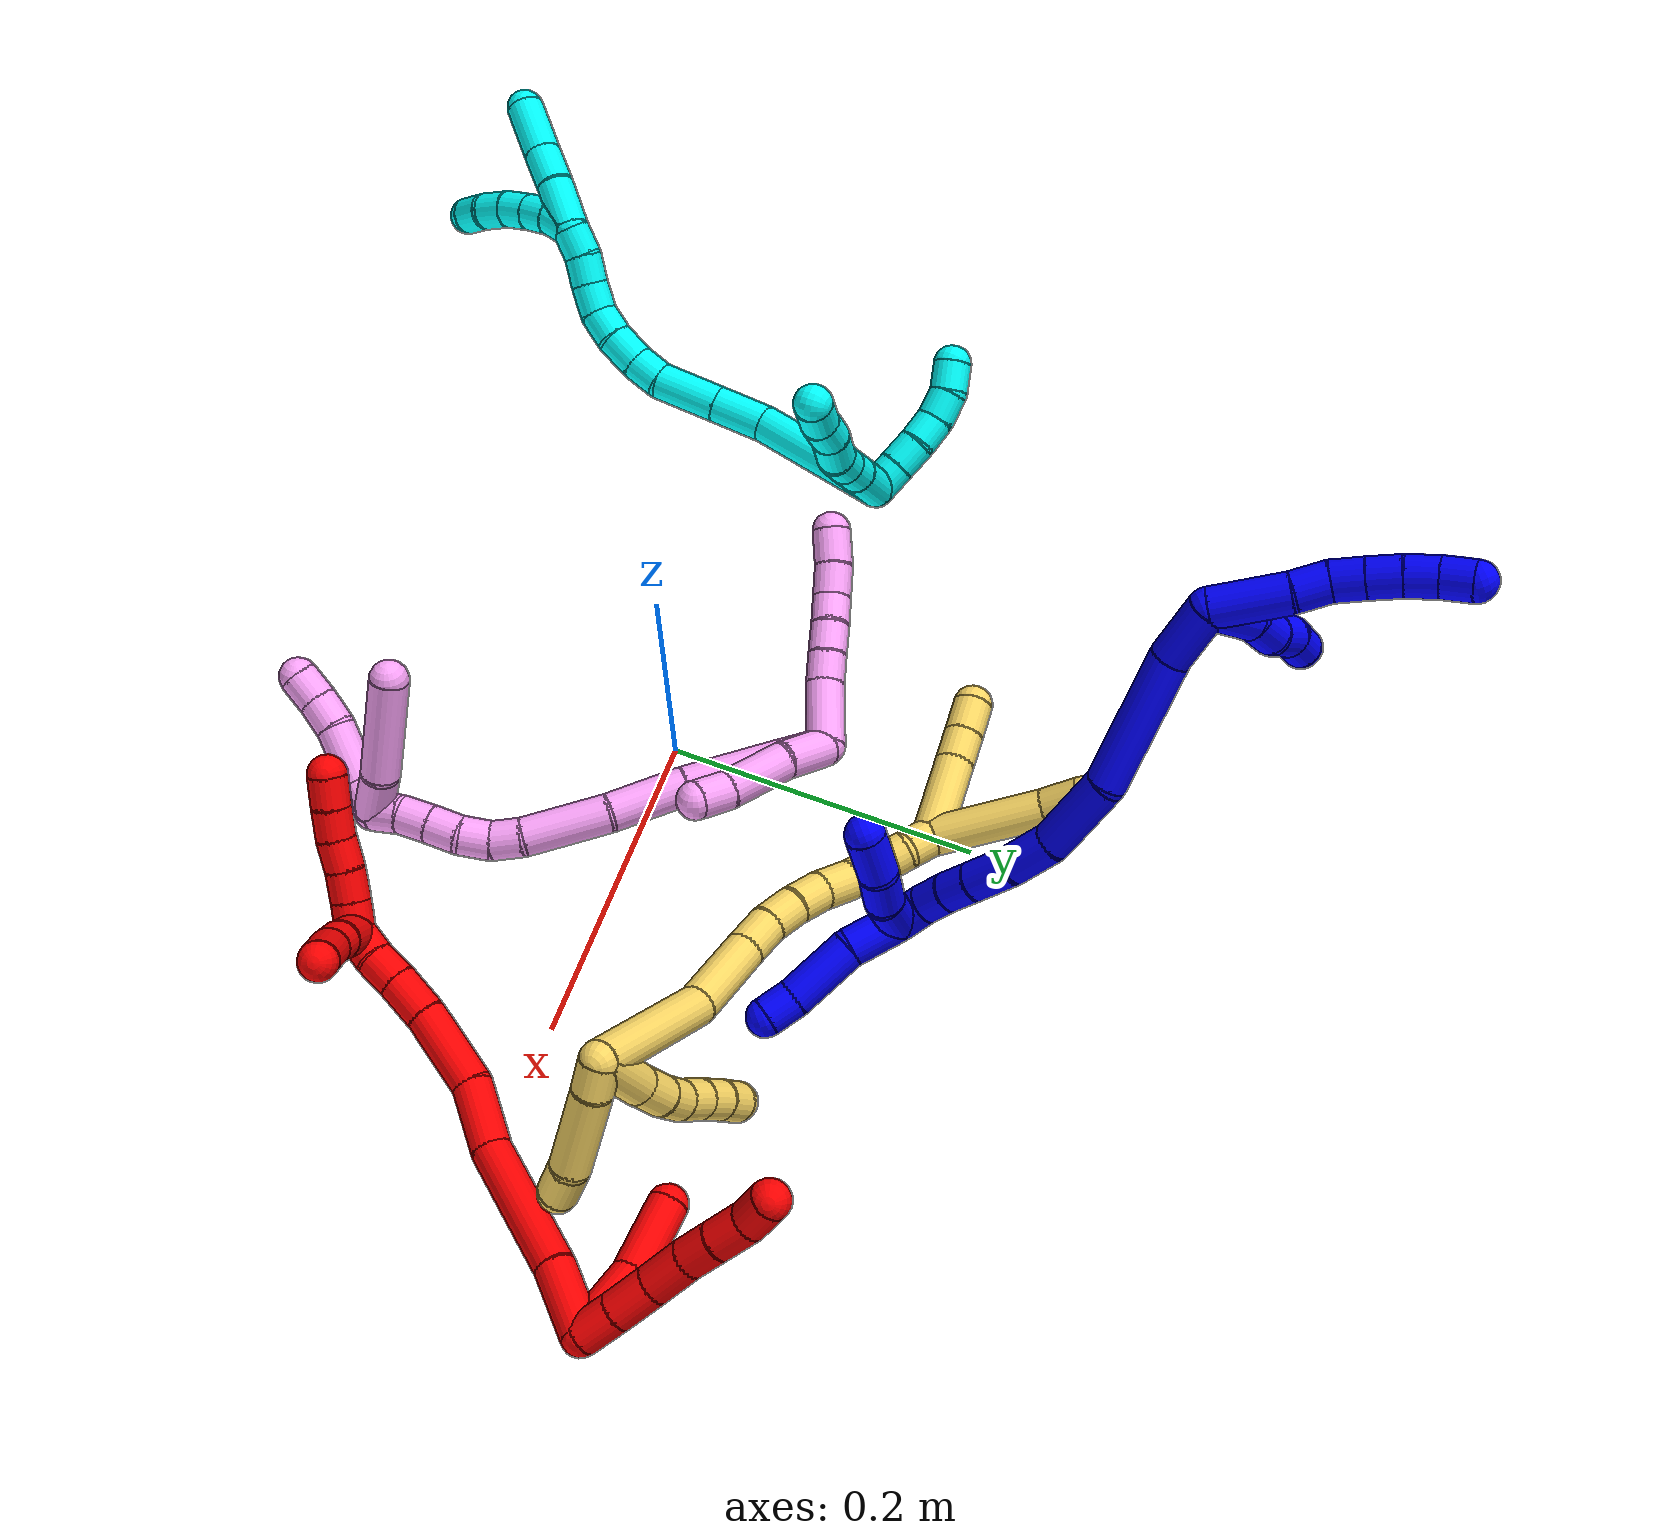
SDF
<sdf version="1.7">
 <world name="default">
  <plugin name="TubeGeneratorPlugin" filename="libtube_generator_plugin.so"/>
  <model name="photoneo_s_sensor">
   <static>1</static>
   <pose>0 0 2 1.57079 1.57079 3.14159</pose>
   <link name="link">
    <inertial><mass>0.1</mass></inertial>
    <sensor name="sensor" type="depth">
     <update_rate>30</update_rate>
     <camera>
      <horizontal_fov>1.22</horizontal_fov>
      <image><width>1920</width><height>1200</height><format>B8G8R8</format></image>
      <clip><near>0.1</near><far>4</far></clip>
      <depth_camera><output>points</output></depth_camera>
     </camera>
     <plugin name="camera_plugin" filename="libgazebo_ros_depth_camera.so">
      <baseline>0.2</baseline>
      <alwaysOn>1</alwaysOn>
      <updateRate>0.0</updateRate>
      <cameraName>camera_ir</cameraName>
      <imageTopicName>/camera/color/image_raw</imageTopicName>
      <cameraInfoTopicName>/camera/color/camera_info</cameraInfoTopicName>
      <depthImageTopicName>/camera/depth/image_raw</depthImageTopicName>
      <depthImageCameraInfoTopicName>/camera/depth/camera_info</depthImageCameraInfoTopicName>
      <pointCloudTopicName>/camera/depth/points</pointCloudTopicName>
      <frameName>fr_optical</frameName>
      <pointCloudCutoff>0.1</pointCloudCutoff>
      <pointCloudCutoffMax>2.0</pointCloudCutoffMax>
      <distortionK1>0</distortionK1>
      <distortionK2>0</distortionK2>
      <distortionK3>0</distortionK3>
      <distortionT1>0</distortionT1>
      <distortionT2>0</distortionT2>
      <CxPrime>0</CxPrime>
      <Cx>0</Cx>
      <Cy>0</Cy>
      <focalLength>0</focalLength>
      <hackBaseline>0</hackBaseline>
     </plugin>
    </sensor>
   </link>
  </model>
  <gravity>0 0 -9.8</gravity>
  <magnetic_field>6e-06 2.3e-05 -4.2e-05</magnetic_field>
  <atmosphere type="adiabatic"/>
  <physics name="default_physics" default="0" type="ode">
   <max_step_size>0.003</max_step_size>
   <real_time_factor>1</real_time_factor>
   <real_time_update_rate>1000</real_time_update_rate>
   <max_contacts>10000</max_contacts>
   <ode>
    <solver>
     <type>quick</type>
     <iters>100</iters>
     <sor>1.3</sor>
     <use_dynamic_moi_rescaling>0</use_dynamic_moi_rescaling>
    </solver>
    <constraints>
     <contact_max_correcting_vel>0</contact_max_correcting_vel>
     <contact_surface_layer>0.001</contact_surface_layer>
     <cfm>0</cfm>
     <erp>0.2</erp>
    </constraints>
   </ode>
  </physics>
  <scene><ambient>0.4 0.4 0.4 1</ambient><background>0.7 0.7 0.7 1</background><shadows>0</shadows></scene>
  <audio><device>default</device></audio>
  <spherical_coordinates>
   <surface_model>EARTH_WGS84</surface_model>
   <latitude_deg>0</latitude_deg>
   <longitude_deg>0</longitude_deg>
   <elevation>0</elevation>
   <heading_deg>0</heading_deg>
  </spherical_coordinates>
  <model name="bin">
   <static>1</static>
   <link name="bottom">
    <collision name="collision-bottom">
     <pose>0 0 -0.01 0 -0 0</pose>
     <geometry><box><size>0.8 0.6 0.02</size></box></geometry>
     <surface>
      <friction><ode><mu>100</mu><mu2>100</mu2></ode></friction>
      <contact><collide_bitmask>65535</collide_bitmask></contact>
     </surface>
    </collision>
   </link>
   <link name="west_wall">
    <collision name="collision-west_wall">
     <pose>-0.41 0 0.1 0 -0 0</pose>
     <geometry><box><size>0.02 0.6 0.2</size></box></geometry>
     <surface>
      <friction><ode><mu>100</mu><mu2>100</mu2></ode></friction>
      <contact><collide_bitmask>65535</collide_bitmask></contact>
     </surface>
    </collision>
   </link>
   <link name="east_wall">
    <collision name="collision-east_wall">
     <pose>0.41 0 0.1 0 -0 0</pose>
     <geometry><box><size>0.02 0.6 0.2</size></box></geometry>
     <surface>
      <friction><ode><mu>100</mu><mu2>100</mu2></ode></friction>
      <contact><collide_bitmask>65535</collide_bitmask></contact>
     </surface>
    </collision>
   </link>
   <link name="south_wall">
    <collision name="collision-south_wall">
     <pose>0 -0.31 0.1 0 -0 0</pose>
     <geometry><box><size>0.8 0.02 0.2</size></box></geometry>
     <surface>
      <friction><ode><mu>100</mu><mu2>100</mu2></ode></friction>
      <contact><collide_bitmask>65535</collide_bitmask></contact>
     </surface>
    </collision>
   </link>
   <link name="north_wall">
    <collision name="collision-north_wall">
     <pose>0 0.31 0.1 0 -0 0</pose>
     <geometry><box><size>0.8 0.02 0.2</size></box></geometry>
     <surface>
      <friction><ode><mu>100</mu><mu2>100</mu2></ode></friction>
      <contact><collide_bitmask>65535</collide_bitmask></contact>
     </surface>
    </collision>
   </link>
  </model>
  <model name="1">
   <static>0</static>
   <link name="1">
    <collision name="collision-cylinder-e_1_2_8">
     <pose>-0.005198 -0.002935 0.022794 0.12805 -0.222437 -0.01432</pose>
     <geometry><cylinder><radius>0.0125</radius><length>0.047126</length></cylinder></geometry>
     <surface>
      <friction><ode><mu>1.16</mu><mu2>1.16</mu2><slip1>0</slip1><slip2>0</slip2></ode></friction>
      <contact><ode><kp>1e+06</kp><kd>1</kd><max_vel>0</max_vel><min_depth>0.001</min_depth></ode></contact>
     </surface>
    </collision>
    <visual name="visual-cylinder-e_1_2_8">
     <pose>-0.005198 -0.002935 0.022794 0.12805 -0.222437 -0.01432</pose>
     <geometry><cylinder><radius>0.0125</radius><length>0.047126</length></cylinder></geometry>
     <material><ambient>0 0 1 1</ambient></material>
    </visual>
    <collision name="collision-cylinder-e_2_8_9">
     <pose>-0.011137 -0.006652 0.056628 0.070768 -0.066826 -0.002366</pose>
     <geometry><cylinder><radius>0.0125</radius><length>0.022184</length></cylinder></geometry>
     <surface>
      <friction><ode><mu>1.16</mu><mu2>1.16</mu2><slip1>0</slip1><slip2>0</slip2></ode></friction>
      <contact><ode><kp>1e+06</kp><kd>1</kd><max_vel>0</max_vel><min_depth>0.001</min_depth></ode></contact>
     </surface>
    </collision>
    <visual name="visual-cylinder-e_2_8_9">
     <pose>-0.011137 -0.006652 0.056628 0.070768 -0.066826 -0.002366</pose>
     <geometry><cylinder><radius>0.0125</radius><length>0.022184</length></cylinder></geometry>
     <material><ambient>0 0 1 1</ambient></material>
    </visual>
    <collision name="collision-cylinder-e_3_9_10">
     <pose>-0.015298 -0.009244 0.077019 0.191132 -0.344743 -0.033374</pose>
     <geometry><cylinder><radius>0.0125</radius><length>0.020241</length></cylinder></geometry>
     <surface>
      <friction><ode><mu>1.16</mu><mu2>1.16</mu2><slip1>0</slip1><slip2>0</slip2></ode></friction>
      <contact><ode><kp>1e+06</kp><kd>1</kd><max_vel>0</max_vel><min_depth>0.001</min_depth></ode></contact>
     </surface>
    </collision>
    <visual name="visual-cylinder-e_3_9_10">
     <pose>-0.015298 -0.009244 0.077019 0.191132 -0.344743 -0.033374</pose>
     <geometry><cylinder><radius>0.0125</radius><length>0.020241</length></cylinder></geometry>
     <material><ambient>0 0 1 1</ambient></material>
    </visual>
    <collision name="collision-cylinder-e_4_10_11">
     <pose>-0.022156 -0.013153 0.095739 0.220445 -0.343883 -0.038433</pose>
     <geometry><cylinder><radius>0.0125</radius><length>0.020394</length></cylinder></geometry>
     <surface>
      <friction><ode><mu>1.16</mu><mu2>1.16</mu2><slip1>0</slip1><slip2>0</slip2></ode></friction>
      <contact><ode><kp>1e+06</kp><kd>1</kd><max_vel>0</max_vel><min_depth>0.001</min_depth></ode></contact>
     </surface>
    </collision>
    <visual name="visual-cylinder-e_4_10_11">
     <pose>-0.022156 -0.013153 0.095739 0.220445 -0.343883 -0.038433</pose>
     <geometry><cylinder><radius>0.0125</radius><length>0.020394</length></cylinder></geometry>
     <material><ambient>0 0 1 1</ambient></material>
    </visual>
    <collision name="collision-cylinder-e_5_11_12">
     <pose>-0.029018 -0.018247 0.114041 0.323421 -0.348515 -0.057422</pose>
     <geometry><cylinder><radius>0.0125</radius><length>0.020052</length></cylinder></geometry>
     <surface>
      <friction><ode><mu>1.16</mu><mu2>1.16</mu2><slip1>0</slip1><slip2>0</slip2></ode></friction>
      <contact><ode><kp>1e+06</kp><kd>1</kd><max_vel>0</max_vel><min_depth>0.001</min_depth></ode></contact>
     </surface>
    </collision>
    <visual name="visual-cylinder-e_5_11_12">
     <pose>-0.029018 -0.018247 0.114041 0.323421 -0.348515 -0.057422</pose>
     <geometry><cylinder><radius>0.0125</radius><length>0.020052</length></cylinder></geometry>
     <material><ambient>0 0 1 1</ambient></material>
    </visual>
    <collision name="collision-cylinder-e_6_12_6">
     <pose>-0.03724 -0.024413 0.131158 0.369687 -0.500355 -0.095485</pose>
     <geometry><cylinder><radius>0.0125</radius><length>0.020003</length></cylinder></geometry>
     <surface>
      <friction><ode><mu>1.16</mu><mu2>1.16</mu2><slip1>0</slip1><slip2>0</slip2></ode></friction>
      <contact><ode><kp>1e+06</kp><kd>1</kd><max_vel>0</max_vel><min_depth>0.001</min_depth></ode></contact>
     </surface>
    </collision>
    <visual name="visual-cylinder-e_6_12_6">
     <pose>-0.03724 -0.024413 0.131158 0.369687 -0.500355 -0.095485</pose>
     <geometry><cylinder><radius>0.0125</radius><length>0.020003</length></cylinder></geometry>
     <material><ambient>0 0 1 1</ambient></material>
    </visual>
    <collision name="collision-cylinder-e_1_2_13">
     <pose>0.006559 -0.01064 0.011292 0.755649 0.39997 0.16055</pose>
     <geometry><cylinder><radius>0.0125</radius><length>0.033689</length></cylinder></geometry>
     <surface>
      <friction><ode><mu>1.16</mu><mu2>1.16</mu2><slip1>0</slip1><slip2>0</slip2></ode></friction>
      <contact><ode><kp>1e+06</kp><kd>1</kd><max_vel>0</max_vel><min_depth>0.001</min_depth></ode></contact>
     </surface>
    </collision>
    <visual name="visual-cylinder-e_1_2_13">
     <pose>0.006559 -0.01064 0.011292 0.755649 0.39997 0.16055</pose>
     <geometry><cylinder><radius>0.0125</radius><length>0.033689</length></cylinder></geometry>
     <material><ambient>0 0 1 1</ambient></material>
    </visual>
    <collision name="collision-cylinder-e_2_13_14">
     <pose>0.019192 -0.030196 0.027104 1.10165 0.545966 0.34061</pose>
     <geometry><cylinder><radius>0.0125</radius><length>0.023394</length></cylinder></geometry>
     <surface>
      <friction><ode><mu>1.16</mu><mu2>1.16</mu2><slip1>0</slip1><slip2>0</slip2></ode></friction>
      <contact><ode><kp>1e+06</kp><kd>1</kd><max_vel>0</max_vel><min_depth>0.001</min_depth></ode></contact>
     </surface>
    </collision>
    <visual name="visual-cylinder-e_2_13_14">
     <pose>0.019192 -0.030196 0.027104 1.10165 0.545966 0.34061</pose>
     <geometry><cylinder><radius>0.0125</radius><length>0.023394</length></cylinder></geometry>
     <material><ambient>0 0 1 1</ambient></material>
    </visual>
    <collision name="collision-cylinder-e_3_14_15">
     <pose>0.03324 -0.044712 0.037349 0.77432 0.783305 0.333652</pose>
     <geometry><cylinder><radius>0.0125</radius><length>0.022601</length></cylinder></geometry>
     <surface>
      <friction><ode><mu>1.16</mu><mu2>1.16</mu2><slip1>0</slip1><slip2>0</slip2></ode></friction>
      <contact><ode><kp>1e+06</kp><kd>1</kd><max_vel>0</max_vel><min_depth>0.001</min_depth></ode></contact>
     </surface>
    </collision>
    <visual name="visual-cylinder-e_3_14_15">
     <pose>0.03324 -0.044712 0.037349 0.77432 0.783305 0.333652</pose>
     <geometry><cylinder><radius>0.0125</radius><length>0.022601</length></cylinder></geometry>
     <material><ambient>0 0 1 1</ambient></material>
    </visual>
    <collision name="collision-cylinder-e_4_15_5">
     <pose>0.04755 -0.057705 0.045963 1.19818 0.673583 0.469331</pose>
     <geometry><cylinder><radius>0.0125</radius><length>0.020315</length></cylinder></geometry>
     <surface>
      <friction><ode><mu>1.16</mu><mu2>1.16</mu2><slip1>0</slip1><slip2>0</slip2></ode></friction>
      <contact><ode><kp>1e+06</kp><kd>1</kd><max_vel>0</max_vel><min_depth>0.001</min_depth></ode></contact>
     </surface>
    </collision>
    <visual name="visual-cylinder-e_4_15_5">
     <pose>0.04755 -0.057705 0.045963 1.19818 0.673583 0.469331</pose>
     <geometry><cylinder><radius>0.0125</radius><length>0.020315</length></cylinder></geometry>
     <material><ambient>0 0 1 1</ambient></material>
    </visual>
    <collision name="collision-cylinder-e_1_2_16">
     <pose>0.007409 -0.012489 -0.014176 2.41937 0.373736 0.928298</pose>
     <geometry><cylinder><radius>0.0125</radius><length>0.040586</length></cylinder></geometry>
     <surface>
      <friction><ode><mu>1.16</mu><mu2>1.16</mu2><slip1>0</slip1><slip2>0</slip2></ode></friction>
      <contact><ode><kp>1e+06</kp><kd>1</kd><max_vel>0</max_vel><min_depth>0.001</min_depth></ode></contact>
     </surface>
    </collision>
    <visual name="visual-cylinder-e_1_2_16">
     <pose>0.007409 -0.012489 -0.014176 2.41937 0.373736 0.928298</pose>
     <geometry><cylinder><radius>0.0125</radius><length>0.040586</length></cylinder></geometry>
     <material><ambient>0 0 1 1</ambient></material>
    </visual>
    <collision name="collision-cylinder-e_2_16_17">
     <pose>0.017487 -0.055331 -0.058325 2.34991 0.062491 0.149306</pose>
     <geometry><cylinder><radius>0.0125</radius><length>0.085484</length></cylinder></geometry>
     <surface>
      <friction><ode><mu>1.16</mu><mu2>1.16</mu2><slip1>0</slip1><slip2>0</slip2></ode></friction>
      <contact><ode><kp>1e+06</kp><kd>1</kd><max_vel>0</max_vel><min_depth>0.001</min_depth></ode></contact>
     </surface>
    </collision>
    <visual name="visual-cylinder-e_2_16_17">
     <pose>0.017487 -0.055331 -0.058325 2.34991 0.062491 0.149306</pose>
     <geometry><cylinder><radius>0.0125</radius><length>0.085484</length></cylinder></geometry>
     <material><ambient>0 0 1 1</ambient></material>
    </visual>
    <collision name="collision-cylinder-e_3_17_18">
     <pose>0.028721 -0.100248 -0.108747 2.5227 0.328767 0.957196</pose>
     <geometry><cylinder><radius>0.0125</radius><length>0.05305</length></cylinder></geometry>
     <surface>
      <friction><ode><mu>1.16</mu><mu2>1.16</mu2><slip1>0</slip1><slip2>0</slip2></ode></friction>
      <contact><ode><kp>1e+06</kp><kd>1</kd><max_vel>0</max_vel><min_depth>0.001</min_depth></ode></contact>
     </surface>
    </collision>
    <visual name="visual-cylinder-e_3_17_18">
     <pose>0.028721 -0.100248 -0.108747 2.5227 0.328767 0.957196</pose>
     <geometry><cylinder><radius>0.0125</radius><length>0.05305</length></cylinder></geometry>
     <material><ambient>0 0 1 1</ambient></material>
    </visual>
    <collision name="collision-cylinder-e_4_18_19">
     <pose>0.042834 -0.119552 -0.142751 2.80518 0.368713 1.66427</pose>
     <geometry><cylinder><radius>0.0125</radius><length>0.030792</length></cylinder></geometry>
     <surface>
      <friction><ode><mu>1.16</mu><mu2>1.16</mu2><slip1>0</slip1><slip2>0</slip2></ode></friction>
      <contact><ode><kp>1e+06</kp><kd>1</kd><max_vel>0</max_vel><min_depth>0.001</min_depth></ode></contact>
     </surface>
    </collision>
    <visual name="visual-cylinder-e_4_18_19">
     <pose>0.042834 -0.119552 -0.142751 2.80518 0.368713 1.66427</pose>
     <geometry><cylinder><radius>0.0125</radius><length>0.030792</length></cylinder></geometry>
     <material><ambient>0 0 1 1</ambient></material>
    </visual>
    <collision name="collision-cylinder-e_5_19_20">
     <pose>0.055145 -0.127617 -0.168835 2.8822 0.480864 2.16379</pose>
     <geometry><cylinder><radius>0.0125</radius><length>0.029239</length></cylinder></geometry>
     <surface>
      <friction><ode><mu>1.16</mu><mu2>1.16</mu2><slip1>0</slip1><slip2>0</slip2></ode></friction>
      <contact><ode><kp>1e+06</kp><kd>1</kd><max_vel>0</max_vel><min_depth>0.001</min_depth></ode></contact>
     </surface>
    </collision>
    <visual name="visual-cylinder-e_5_19_20">
     <pose>0.055145 -0.127617 -0.168835 2.8822 0.480864 2.16379</pose>
     <geometry><cylinder><radius>0.0125</radius><length>0.029239</length></cylinder></geometry>
     <material><ambient>0 0 1 1</ambient></material>
    </visual>
    <collision name="collision-cylinder-e_6_20_21">
     <pose>0.066929 -0.133332 -0.189764 2.8644 0.521832 2.17872</pose>
     <geometry><cylinder><radius>0.0125</radius><length>0.02015</length></cylinder></geometry>
     <surface>
      <friction><ode><mu>1.16</mu><mu2>1.16</mu2><slip1>0</slip1><slip2>0</slip2></ode></friction>
      <contact><ode><kp>1e+06</kp><kd>1</kd><max_vel>0</max_vel><min_depth>0.001</min_depth></ode></contact>
     </surface>
    </collision>
    <visual name="visual-cylinder-e_6_20_21">
     <pose>0.066929 -0.133332 -0.189764 2.8644 0.521832 2.17872</pose>
     <geometry><cylinder><radius>0.0125</radius><length>0.02015</length></cylinder></geometry>
     <material><ambient>0 0 1 1</ambient></material>
    </visual>
    <collision name="collision-cylinder-e_7_21_22">
     <pose>0.077081 -0.138889 -0.206248 2.76824 0.533683 1.93236</pose>
     <geometry><cylinder><radius>0.0125</radius><length>0.020169</length></cylinder></geometry>
     <surface>
      <friction><ode><mu>1.16</mu><mu2>1.16</mu2><slip1>0</slip1><slip2>0</slip2></ode></friction>
      <contact><ode><kp>1e+06</kp><kd>1</kd><max_vel>0</max_vel><min_depth>0.001</min_depth></ode></contact>
     </surface>
    </collision>
    <visual name="visual-cylinder-e_7_21_22">
     <pose>0.077081 -0.138889 -0.206248 2.76824 0.533683 1.93236</pose>
     <geometry><cylinder><radius>0.0125</radius><length>0.020169</length></cylinder></geometry>
     <material><ambient>0 0 1 1</ambient></material>
    </visual>
    <collision name="collision-cylinder-e_8_22_1">
     <pose>0.084377 -0.145265 -0.223839 2.81606 0.212622 1.15249</pose>
     <geometry><cylinder><radius>0.0125</radius><length>0.020531</length></cylinder></geometry>
     <surface>
      <friction><ode><mu>1.16</mu><mu2>1.16</mu2><slip1>0</slip1><slip2>0</slip2></ode></friction>
      <contact><ode><kp>1e+06</kp><kd>1</kd><max_vel>0</max_vel><min_depth>0.001</min_depth></ode></contact>
     </surface>
    </collision>
    <visual name="visual-cylinder-e_8_22_1">
     <pose>0.084377 -0.145265 -0.223839 2.81606 0.212622 1.15249</pose>
     <geometry><cylinder><radius>0.0125</radius><length>0.020531</length></cylinder></geometry>
     <material><ambient>0 0 1 1</ambient></material>
    </visual>
    <collision name="collision-cylinder-e_1_1_23">
     <pose>0.083035 -0.149056 -0.25017 3.10699 -0.205514 -2.80906</pose>
     <geometry><cylinder><radius>0.0125</radius><length>0.034391</length></cylinder></geometry>
     <surface>
      <friction><ode><mu>1.16</mu><mu2>1.16</mu2><slip1>0</slip1><slip2>0</slip2></ode></friction>
      <contact><ode><kp>1e+06</kp><kd>1</kd><max_vel>0</max_vel><min_depth>0.001</min_depth></ode></contact>
     </surface>
    </collision>
    <visual name="visual-cylinder-e_1_1_23">
     <pose>0.083035 -0.149056 -0.25017 3.10699 -0.205514 -2.80906</pose>
     <geometry><cylinder><radius>0.0125</radius><length>0.034391</length></cylinder></geometry>
     <material><ambient>0 0 1 1</ambient></material>
    </visual>
    <collision name="collision-cylinder-e_2_23_24">
     <pose>0.074832 -0.156251 -0.288066 2.83751 -0.209424 -1.20241</pose>
     <geometry><cylinder><radius>0.0125</radius><length>0.045158</length></cylinder></geometry>
     <surface>
      <friction><ode><mu>1.16</mu><mu2>1.16</mu2><slip1>0</slip1><slip2>0</slip2></ode></friction>
      <contact><ode><kp>1e+06</kp><kd>1</kd><max_vel>0</max_vel><min_depth>0.001</min_depth></ode></contact>
     </surface>
    </collision>
    <visual name="visual-cylinder-e_2_23_24">
     <pose>0.074832 -0.156251 -0.288066 2.83751 -0.209424 -1.20241</pose>
     <geometry><cylinder><radius>0.0125</radius><length>0.045158</length></cylinder></geometry>
     <material><ambient>0 0 1 1</ambient></material>
    </visual>
    <collision name="collision-cylinder-e_3_24_4">
     <pose>0.067606 -0.164101 -0.318968 3.01647 -0.25017 -2.21719</pose>
     <geometry><cylinder><radius>0.0125</radius><length>0.020452</length></cylinder></geometry>
     <surface>
      <friction><ode><mu>1.16</mu><mu2>1.16</mu2><slip1>0</slip1><slip2>0</slip2></ode></friction>
      <contact><ode><kp>1e+06</kp><kd>1</kd><max_vel>0</max_vel><min_depth>0.001</min_depth></ode></contact>
     </surface>
    </collision>
    <visual name="visual-cylinder-e_3_24_4">
     <pose>0.067606 -0.164101 -0.318968 3.01647 -0.25017 -2.21719</pose>
     <geometry><cylinder><radius>0.0125</radius><length>0.020452</length></cylinder></geometry>
     <material><ambient>0 0 1 1</ambient></material>
    </visual>
    <collision name="collision-cylinder-e_1_1_25">
     <pose>0.071895 -0.133645 -0.234016 -1.6159 -0.778753 0.810953</pose>
     <geometry><cylinder><radius>0.0125</radius><length>0.04171</length></cylinder></geometry>
     <surface>
      <friction><ode><mu>1.16</mu><mu2>1.16</mu2><slip1>0</slip1><slip2>0</slip2></ode></friction>
      <contact><ode><kp>1e+06</kp><kd>1</kd><max_vel>0</max_vel><min_depth>0.001</min_depth></ode></contact>
     </surface>
    </collision>
    <visual name="visual-cylinder-e_1_1_25">
     <pose>0.071895 -0.133645 -0.234016 -1.6159 -0.778753 0.810953</pose>
     <geometry><cylinder><radius>0.0125</radius><length>0.04171</length></cylinder></geometry>
     <material><ambient>0 0 1 1</ambient></material>
    </visual>
    <collision name="collision-cylinder-e_2_25_26">
     <pose>0.050299 -0.106933 -0.23282 -1.41512 -0.52381 0.450754</pose>
     <geometry><cylinder><radius>0.0125</radius><length>0.027781</length></cylinder></geometry>
     <surface>
      <friction><ode><mu>1.16</mu><mu2>1.16</mu2><slip1>0</slip1><slip2>0</slip2></ode></friction>
      <contact><ode><kp>1e+06</kp><kd>1</kd><max_vel>0</max_vel><min_depth>0.001</min_depth></ode></contact>
     </surface>
    </collision>
    <visual name="visual-cylinder-e_2_25_26">
     <pose>0.050299 -0.106933 -0.23282 -1.41512 -0.52381 0.450754</pose>
     <geometry><cylinder><radius>0.0125</radius><length>0.027781</length></cylinder></geometry>
     <material><ambient>0 0 1 1</ambient></material>
    </visual>
    <collision name="collision-cylinder-e_3_26_3">
     <pose>0.039234 -0.080391 -0.230025 -1.50743 -0.273312 0.25671</pose>
     <geometry><cylinder><radius>0.0125</radius><length>0.030509</length></cylinder></geometry>
     <surface>
      <friction><ode><mu>1.16</mu><mu2>1.16</mu2><slip1>0</slip1><slip2>0</slip2></ode></friction>
      <contact><ode><kp>1e+06</kp><kd>1</kd><max_vel>0</max_vel><min_depth>0.001</min_depth></ode></contact>
     </surface>
    </collision>
    <visual name="visual-cylinder-e_3_26_3">
     <pose>0.039234 -0.080391 -0.230025 -1.50743 -0.273312 0.25671</pose>
     <geometry><cylinder><radius>0.0125</radius><length>0.030509</length></cylinder></geometry>
     <material><ambient>0 0 1 1</ambient></material>
    </visual>
    <collision name="collision-sphere-3">
     <pose>0.035116 -0.065732 -0.229095 0 -0 0</pose>
     <geometry><sphere><radius>0.0125</radius></sphere></geometry>
     <surface>
      <friction><ode><mu>1.16</mu><mu2>1.16</mu2><slip1>0</slip1><slip2>0</slip2></ode></friction>
      <contact><ode><kp>1e+06</kp><kd>1</kd><max_vel>0</max_vel><min_depth>0.001</min_depth></ode></contact>
     </surface>
    </collision>
    <visual name="visual-sphere-3">
     <pose>0.035116 -0.065732 -0.229095 0 -0 0</pose>
     <geometry><sphere><radius>0.0125</radius></sphere></geometry>
     <material><ambient>0 0 1 1</ambient></material>
    </visual>
    <collision name="collision-sphere-26">
     <pose>0.043352 -0.09505 -0.230955 0 -0 0</pose>
     <geometry><sphere><radius>0.0125</radius></sphere></geometry>
     <surface>
      <friction><ode><mu>1.16</mu><mu2>1.16</mu2><slip1>0</slip1><slip2>0</slip2></ode></friction>
      <contact><ode><kp>1e+06</kp><kd>1</kd><max_vel>0</max_vel><min_depth>0.001</min_depth></ode></contact>
     </surface>
    </collision>
    <visual name="visual-sphere-26">
     <pose>0.043352 -0.09505 -0.230955 0 -0 0</pose>
     <geometry><sphere><radius>0.0125</radius></sphere></geometry>
     <material><ambient>0 0 1 1</ambient></material>
    </visual>
    <collision name="collision-sphere-25">
     <pose>0.057247 -0.118815 -0.234685 0 -0 0</pose>
     <geometry><sphere><radius>0.0125</radius></sphere></geometry>
     <surface>
      <friction><ode><mu>1.16</mu><mu2>1.16</mu2><slip1>0</slip1><slip2>0</slip2></ode></friction>
      <contact><ode><kp>1e+06</kp><kd>1</kd><max_vel>0</max_vel><min_depth>0.001</min_depth></ode></contact>
     </surface>
    </collision>
    <visual name="visual-sphere-25">
     <pose>0.057247 -0.118815 -0.234685 0 -0 0</pose>
     <geometry><sphere><radius>0.0125</radius></sphere></geometry>
     <material><ambient>0 0 1 1</ambient></material>
    </visual>
    <collision name="collision-sphere-4">
     <pose>0.065074 -0.165337 -0.328798 0 -0 0</pose>
     <geometry><sphere><radius>0.0125</radius></sphere></geometry>
     <surface>
      <friction><ode><mu>1.16</mu><mu2>1.16</mu2><slip1>0</slip1><slip2>0</slip2></ode></friction>
      <contact><ode><kp>1e+06</kp><kd>1</kd><max_vel>0</max_vel><min_depth>0.001</min_depth></ode></contact>
     </surface>
    </collision>
    <visual name="visual-sphere-4">
     <pose>0.065074 -0.165337 -0.328798 0 -0 0</pose>
     <geometry><sphere><radius>0.0125</radius></sphere></geometry>
     <material><ambient>0 0 1 1</ambient></material>
    </visual>
    <collision name="collision-sphere-24">
     <pose>0.070137 -0.162864 -0.309138 0 -0 0</pose>
     <geometry><sphere><radius>0.0125</radius></sphere></geometry>
     <surface>
      <friction><ode><mu>1.16</mu><mu2>1.16</mu2><slip1>0</slip1><slip2>0</slip2></ode></friction>
      <contact><ode><kp>1e+06</kp><kd>1</kd><max_vel>0</max_vel><min_depth>0.001</min_depth></ode></contact>
     </surface>
    </collision>
    <visual name="visual-sphere-24">
     <pose>0.070137 -0.162864 -0.309138 0 -0 0</pose>
     <geometry><sphere><radius>0.0125</radius></sphere></geometry>
     <material><ambient>0 0 1 1</ambient></material>
    </visual>
    <collision name="collision-sphere-23">
     <pose>0.079526 -0.149639 -0.266993 0 -0 0</pose>
     <geometry><sphere><radius>0.0125</radius></sphere></geometry>
     <surface>
      <friction><ode><mu>1.16</mu><mu2>1.16</mu2><slip1>0</slip1><slip2>0</slip2></ode></friction>
      <contact><ode><kp>1e+06</kp><kd>1</kd><max_vel>0</max_vel><min_depth>0.001</min_depth></ode></contact>
     </surface>
    </collision>
    <visual name="visual-sphere-23">
     <pose>0.079526 -0.149639 -0.266993 0 -0 0</pose>
     <geometry><sphere><radius>0.0125</radius></sphere></geometry>
     <material><ambient>0 0 1 1</ambient></material>
    </visual>
    <collision name="collision-sphere-1">
     <pose>0.086544 -0.148474 -0.233347 0 -0 0</pose>
     <geometry><sphere><radius>0.0125</radius></sphere></geometry>
     <surface>
      <friction><ode><mu>1.16</mu><mu2>1.16</mu2><slip1>0</slip1><slip2>0</slip2></ode></friction>
      <contact><ode><kp>1e+06</kp><kd>1</kd><max_vel>0</max_vel><min_depth>0.001</min_depth></ode></contact>
     </surface>
    </collision>
    <visual name="visual-sphere-1">
     <pose>0.086544 -0.148474 -0.233347 0 -0 0</pose>
     <geometry><sphere><radius>0.0125</radius></sphere></geometry>
     <material><ambient>0 0 1 1</ambient></material>
    </visual>
    <collision name="collision-sphere-22">
     <pose>0.082211 -0.142056 -0.214332 0 -0 0</pose>
     <geometry><sphere><radius>0.0125</radius></sphere></geometry>
     <surface>
      <friction><ode><mu>1.16</mu><mu2>1.16</mu2><slip1>0</slip1><slip2>0</slip2></ode></friction>
      <contact><ode><kp>1e+06</kp><kd>1</kd><max_vel>0</max_vel><min_depth>0.001</min_depth></ode></contact>
     </surface>
    </collision>
    <visual name="visual-sphere-22">
     <pose>0.082211 -0.142056 -0.214332 0 -0 0</pose>
     <geometry><sphere><radius>0.0125</radius></sphere></geometry>
     <material><ambient>0 0 1 1</ambient></material>
    </visual>
    <collision name="collision-sphere-21">
     <pose>0.071951 -0.135722 -0.198164 0 -0 0</pose>
     <geometry><sphere><radius>0.0125</radius></sphere></geometry>
     <surface>
      <friction><ode><mu>1.16</mu><mu2>1.16</mu2><slip1>0</slip1><slip2>0</slip2></ode></friction>
      <contact><ode><kp>1e+06</kp><kd>1</kd><max_vel>0</max_vel><min_depth>0.001</min_depth></ode></contact>
     </surface>
    </collision>
    <visual name="visual-sphere-21">
     <pose>0.071951 -0.135722 -0.198164 0 -0 0</pose>
     <geometry><sphere><radius>0.0125</radius></sphere></geometry>
     <material><ambient>0 0 1 1</ambient></material>
    </visual>
    <collision name="collision-sphere-12">
     <pose>-0.032442 -0.021242 0.122976 0 -0 0</pose>
     <geometry><sphere><radius>0.0125</radius></sphere></geometry>
     <surface>
      <friction><ode><mu>1.16</mu><mu2>1.16</mu2><slip1>0</slip1><slip2>0</slip2></ode></friction>
      <contact><ode><kp>1e+06</kp><kd>1</kd><max_vel>0</max_vel><min_depth>0.001</min_depth></ode></contact>
     </surface>
    </collision>
    <visual name="visual-sphere-12">
     <pose>-0.032442 -0.021242 0.122976 0 -0 0</pose>
     <geometry><sphere><radius>0.0125</radius></sphere></geometry>
     <material><ambient>0 0 1 1</ambient></material>
    </visual>
    <collision name="collision-sphere-11">
     <pose>-0.025594 -0.015252 0.105107 0 -0 0</pose>
     <geometry><sphere><radius>0.0125</radius></sphere></geometry>
     <surface>
      <friction><ode><mu>1.16</mu><mu2>1.16</mu2><slip1>0</slip1><slip2>0</slip2></ode></friction>
      <contact><ode><kp>1e+06</kp><kd>1</kd><max_vel>0</max_vel><min_depth>0.001</min_depth></ode></contact>
     </surface>
    </collision>
    <visual name="visual-sphere-11">
     <pose>-0.025594 -0.015252 0.105107 0 -0 0</pose>
     <geometry><sphere><radius>0.0125</radius></sphere></geometry>
     <material><ambient>0 0 1 1</ambient></material>
    </visual>
    <collision name="collision-sphere-10">
     <pose>-0.018718 -0.011054 0.086371 0 -0 0</pose>
     <geometry><sphere><radius>0.0125</radius></sphere></geometry>
     <surface>
      <friction><ode><mu>1.16</mu><mu2>1.16</mu2><slip1>0</slip1><slip2>0</slip2></ode></friction>
      <contact><ode><kp>1e+06</kp><kd>1</kd><max_vel>0</max_vel><min_depth>0.001</min_depth></ode></contact>
     </surface>
    </collision>
    <visual name="visual-sphere-10">
     <pose>-0.018718 -0.011054 0.086371 0 -0 0</pose>
     <geometry><sphere><radius>0.0125</radius></sphere></geometry>
     <material><ambient>0 0 1 1</ambient></material>
    </visual>
    <collision name="collision-sphere-9">
     <pose>-0.011878 -0.007435 0.067668 0 -0 0</pose>
     <geometry><sphere><radius>0.0125</radius></sphere></geometry>
     <surface>
      <friction><ode><mu>1.16</mu><mu2>1.16</mu2><slip1>0</slip1><slip2>0</slip2></ode></friction>
      <contact><ode><kp>1e+06</kp><kd>1</kd><max_vel>0</max_vel><min_depth>0.001</min_depth></ode></contact>
     </surface>
    </collision>
    <visual name="visual-sphere-9">
     <pose>-0.011878 -0.007435 0.067668 0 -0 0</pose>
     <geometry><sphere><radius>0.0125</radius></sphere></geometry>
     <material><ambient>0 0 1 1</ambient></material>
    </visual>
    <collision name="collision-sphere-2">
     <geometry><sphere><radius>0.0125</radius></sphere></geometry>
     <surface>
      <friction><ode><mu>1.16</mu><mu2>1.16</mu2><slip1>0</slip1><slip2>0</slip2></ode></friction>
      <contact><ode><kp>1e+06</kp><kd>1</kd><max_vel>0</max_vel><min_depth>0.001</min_depth></ode></contact>
     </surface>
    </collision>
    <visual name="visual-sphere-2">
     <geometry><sphere><radius>0.0125</radius></sphere></geometry>
     <material><ambient>0 0 1 1</ambient></material>
    </visual>
    <collision name="collision-sphere-19">
     <pose>0.048383 -0.124293 -0.156307 0 -0 0</pose>
     <geometry><sphere><radius>0.0125</radius></sphere></geometry>
     <surface>
      <friction><ode><mu>1.16</mu><mu2>1.16</mu2><slip1>0</slip1><slip2>0</slip2></ode></friction>
      <contact><ode><kp>1e+06</kp><kd>1</kd><max_vel>0</max_vel><min_depth>0.001</min_depth></ode></contact>
     </surface>
    </collision>
    <visual name="visual-sphere-19">
     <pose>0.048383 -0.124293 -0.156307 0 -0 0</pose>
     <geometry><sphere><radius>0.0125</radius></sphere></geometry>
     <material><ambient>0 0 1 1</ambient></material>
    </visual>
    <collision name="collision-sphere-8">
     <pose>-0.010396 -0.00587 0.045589 0 -0 0</pose>
     <geometry><sphere><radius>0.0125</radius></sphere></geometry>
     <surface>
      <friction><ode><mu>1.16</mu><mu2>1.16</mu2><slip1>0</slip1><slip2>0</slip2></ode></friction>
      <contact><ode><kp>1e+06</kp><kd>1</kd><max_vel>0</max_vel><min_depth>0.001</min_depth></ode></contact>
     </surface>
    </collision>
    <visual name="visual-sphere-8">
     <pose>-0.010396 -0.00587 0.045589 0 -0 0</pose>
     <geometry><sphere><radius>0.0125</radius></sphere></geometry>
     <material><ambient>0 0 1 1</ambient></material>
    </visual>
    <collision name="collision-sphere-6">
     <pose>-0.042038 -0.027583 0.139341 0 -0 0</pose>
     <geometry><sphere><radius>0.0125</radius></sphere></geometry>
     <surface>
      <friction><ode><mu>1.16</mu><mu2>1.16</mu2><slip1>0</slip1><slip2>0</slip2></ode></friction>
      <contact><ode><kp>1e+06</kp><kd>1</kd><max_vel>0</max_vel><min_depth>0.001</min_depth></ode></contact>
     </surface>
    </collision>
    <visual name="visual-sphere-6">
     <pose>-0.042038 -0.027583 0.139341 0 -0 0</pose>
     <geometry><sphere><radius>0.0125</radius></sphere></geometry>
     <material><ambient>0 0 1 1</ambient></material>
    </visual>
    <collision name="collision-sphere-13">
     <pose>0.013118 -0.021279 0.022585 0 -0 0</pose>
     <geometry><sphere><radius>0.0125</radius></sphere></geometry>
     <surface>
      <friction><ode><mu>1.16</mu><mu2>1.16</mu2><slip1>0</slip1><slip2>0</slip2></ode></friction>
      <contact><ode><kp>1e+06</kp><kd>1</kd><max_vel>0</max_vel><min_depth>0.001</min_depth></ode></contact>
     </surface>
    </collision>
    <visual name="visual-sphere-13">
     <pose>0.013118 -0.021279 0.022585 0 -0 0</pose>
     <geometry><sphere><radius>0.0125</radius></sphere></geometry>
     <material><ambient>0 0 1 1</ambient></material>
    </visual>
    <collision name="collision-sphere-14">
     <pose>0.025266 -0.039113 0.031624 0 -0 0</pose>
     <geometry><sphere><radius>0.0125</radius></sphere></geometry>
     <surface>
      <friction><ode><mu>1.16</mu><mu2>1.16</mu2><slip1>0</slip1><slip2>0</slip2></ode></friction>
      <contact><ode><kp>1e+06</kp><kd>1</kd><max_vel>0</max_vel><min_depth>0.001</min_depth></ode></contact>
     </surface>
    </collision>
    <visual name="visual-sphere-14">
     <pose>0.025266 -0.039113 0.031624 0 -0 0</pose>
     <geometry><sphere><radius>0.0125</radius></sphere></geometry>
     <material><ambient>0 0 1 1</ambient></material>
    </visual>
    <collision name="collision-sphere-15">
     <pose>0.041213 -0.050311 0.043073 0 -0 0</pose>
     <geometry><sphere><radius>0.0125</radius></sphere></geometry>
     <surface>
      <friction><ode><mu>1.16</mu><mu2>1.16</mu2><slip1>0</slip1><slip2>0</slip2></ode></friction>
      <contact><ode><kp>1e+06</kp><kd>1</kd><max_vel>0</max_vel><min_depth>0.001</min_depth></ode></contact>
     </surface>
    </collision>
    <visual name="visual-sphere-15">
     <pose>0.041213 -0.050311 0.043073 0 -0 0</pose>
     <geometry><sphere><radius>0.0125</radius></sphere></geometry>
     <material><ambient>0 0 1 1</ambient></material>
    </visual>
    <collision name="collision-sphere-5">
     <pose>0.053886 -0.065099 0.048854 0 -0 0</pose>
     <geometry><sphere><radius>0.0125</radius></sphere></geometry>
     <surface>
      <friction><ode><mu>1.16</mu><mu2>1.16</mu2><slip1>0</slip1><slip2>0</slip2></ode></friction>
      <contact><ode><kp>1e+06</kp><kd>1</kd><max_vel>0</max_vel><min_depth>0.001</min_depth></ode></contact>
     </surface>
    </collision>
    <visual name="visual-sphere-5">
     <pose>0.053886 -0.065099 0.048854 0 -0 0</pose>
     <geometry><sphere><radius>0.0125</radius></sphere></geometry>
     <material><ambient>0 0 1 1</ambient></material>
    </visual>
    <collision name="collision-sphere-16">
     <pose>0.014818 -0.024978 -0.028351 0 -0 0</pose>
     <geometry><sphere><radius>0.0125</radius></sphere></geometry>
     <surface>
      <friction><ode><mu>1.16</mu><mu2>1.16</mu2><slip1>0</slip1><slip2>0</slip2></ode></friction>
      <contact><ode><kp>1e+06</kp><kd>1</kd><max_vel>0</max_vel><min_depth>0.001</min_depth></ode></contact>
     </surface>
    </collision>
    <visual name="visual-sphere-16">
     <pose>0.014818 -0.024978 -0.028351 0 -0 0</pose>
     <geometry><sphere><radius>0.0125</radius></sphere></geometry>
     <material><ambient>0 0 1 1</ambient></material>
    </visual>
    <collision name="collision-sphere-17">
     <pose>0.020156 -0.085684 -0.088299 0 -0 0</pose>
     <geometry><sphere><radius>0.0125</radius></sphere></geometry>
     <surface>
      <friction><ode><mu>1.16</mu><mu2>1.16</mu2><slip1>0</slip1><slip2>0</slip2></ode></friction>
      <contact><ode><kp>1e+06</kp><kd>1</kd><max_vel>0</max_vel><min_depth>0.001</min_depth></ode></contact>
     </surface>
    </collision>
    <visual name="visual-sphere-17">
     <pose>0.020156 -0.085684 -0.088299 0 -0 0</pose>
     <geometry><sphere><radius>0.0125</radius></sphere></geometry>
     <material><ambient>0 0 1 1</ambient></material>
    </visual>
    <collision name="collision-sphere-18">
     <pose>0.037285 -0.114811 -0.129195 0 -0 0</pose>
     <geometry><sphere><radius>0.0125</radius></sphere></geometry>
     <surface>
      <friction><ode><mu>1.16</mu><mu2>1.16</mu2><slip1>0</slip1><slip2>0</slip2></ode></friction>
      <contact><ode><kp>1e+06</kp><kd>1</kd><max_vel>0</max_vel><min_depth>0.001</min_depth></ode></contact>
     </surface>
    </collision>
    <visual name="visual-sphere-18">
     <pose>0.037285 -0.114811 -0.129195 0 -0 0</pose>
     <geometry><sphere><radius>0.0125</radius></sphere></geometry>
     <material><ambient>0 0 1 1</ambient></material>
    </visual>
    <collision name="collision-sphere-20">
     <pose>0.061907 -0.130942 -0.181363 0 -0 0</pose>
     <geometry><sphere><radius>0.0125</radius></sphere></geometry>
     <surface>
      <friction><ode><mu>1.16</mu><mu2>1.16</mu2><slip1>0</slip1><slip2>0</slip2></ode></friction>
      <contact><ode><kp>1e+06</kp><kd>1</kd><max_vel>0</max_vel><min_depth>0.001</min_depth></ode></contact>
     </surface>
    </collision>
    <visual name="visual-sphere-20">
     <pose>0.061907 -0.130942 -0.181363 0 -0 0</pose>
     <geometry><sphere><radius>0.0125</radius></sphere></geometry>
     <material><ambient>0 0 1 1</ambient></material>
    </visual>
    <inertial>
     <pose>0.031871 -0.077089 -0.094772 0 -0 0</pose>
     <mass>0.75</mass>
     <inertia><ixx>0.000129</ixx><ixy>0</ixy><ixz>0</ixz><iyy>9e-06</iyy><iyz>0</iyz><izz>4.1e-05</izz></inertia>
    </inertial>
   </link>
   <pose>-0.091279 0.299415 0.23345 1.29831 0.778479 -2.64698</pose>
  </model>
  <model name="2">
   <static>0</static>
   <link name="2">
    <collision name="collision-cylinder-e_1_2_8">
     <pose>0.012391 -0.001172 -0.002377 2.68338 1.36007 2.58011</pose>
     <geometry><cylinder><radius>0.0125</radius><length>0.025342</length></cylinder></geometry>
     <surface>
      <friction><ode><mu>1.16</mu><mu2>1.16</mu2><slip1>0</slip1><slip2>0</slip2></ode></friction>
      <contact><ode><kp>1e+06</kp><kd>1</kd><max_vel>0</max_vel><min_depth>0.001</min_depth></ode></contact>
     </surface>
    </collision>
    <visual name="visual-cylinder-e_1_2_8">
     <pose>0.012391 -0.001172 -0.002377 2.68338 1.36007 2.58011</pose>
     <geometry><cylinder><radius>0.0125</radius><length>0.025342</length></cylinder></geometry>
     <material><ambient>1 0 0 1</ambient></material>
    </visual>
    <collision name="collision-cylinder-e_2_8_9">
     <pose>0.038326 -0.003983 -0.007566 2.61416 1.33503 2.48155</pose>
     <geometry><cylinder><radius>0.0125</radius><length>0.027861</length></cylinder></geometry>
     <surface>
      <friction><ode><mu>1.16</mu><mu2>1.16</mu2><slip1>0</slip1><slip2>0</slip2></ode></friction>
      <contact><ode><kp>1e+06</kp><kd>1</kd><max_vel>0</max_vel><min_depth>0.001</min_depth></ode></contact>
     </surface>
    </collision>
    <visual name="visual-cylinder-e_2_8_9">
     <pose>0.038326 -0.003983 -0.007566 2.61416 1.33503 2.48155</pose>
     <geometry><cylinder><radius>0.0125</radius><length>0.027861</length></cylinder></geometry>
     <material><ambient>1 0 0 1</ambient></material>
    </visual>
    <collision name="collision-cylinder-e_3_9_10">
     <pose>0.064982 -0.007592 -0.014833 2.72485 1.21501 2.5511</pose>
     <geometry><cylinder><radius>0.0125</radius><length>0.027974</length></cylinder></geometry>
     <surface>
      <friction><ode><mu>1.16</mu><mu2>1.16</mu2><slip1>0</slip1><slip2>0</slip2></ode></friction>
      <contact><ode><kp>1e+06</kp><kd>1</kd><max_vel>0</max_vel><min_depth>0.001</min_depth></ode></contact>
     </surface>
    </collision>
    <visual name="visual-cylinder-e_3_9_10">
     <pose>0.064982 -0.007592 -0.014833 2.72485 1.21501 2.5511</pose>
     <geometry><cylinder><radius>0.0125</radius><length>0.027974</length></cylinder></geometry>
     <material><ambient>1 0 0 1</ambient></material>
    </visual>
    <collision name="collision-cylinder-e_4_10_11">
     <pose>0.088242 -0.010436 -0.02378 2.94995 1.14721 2.84622</pose>
     <geometry><cylinder><radius>0.0125</radius><length>0.022266</length></cylinder></geometry>
     <surface>
      <friction><ode><mu>1.16</mu><mu2>1.16</mu2><slip1>0</slip1><slip2>0</slip2></ode></friction>
      <contact><ode><kp>1e+06</kp><kd>1</kd><max_vel>0</max_vel><min_depth>0.001</min_depth></ode></contact>
     </surface>
    </collision>
    <visual name="visual-cylinder-e_4_10_11">
     <pose>0.088242 -0.010436 -0.02378 2.94995 1.14721 2.84622</pose>
     <geometry><cylinder><radius>0.0125</radius><length>0.022266</length></cylinder></geometry>
     <material><ambient>1 0 0 1</ambient></material>
    </visual>
    <collision name="collision-cylinder-e_5_11_12">
     <pose>0.109671 -0.012162 -0.032648 2.94887 1.19439 2.8592</pose>
     <geometry><cylinder><radius>0.0125</radius><length>0.024259</length></cylinder></geometry>
     <surface>
      <friction><ode><mu>1.16</mu><mu2>1.16</mu2><slip1>0</slip1><slip2>0</slip2></ode></friction>
      <contact><ode><kp>1e+06</kp><kd>1</kd><max_vel>0</max_vel><min_depth>0.001</min_depth></ode></contact>
     </surface>
    </collision>
    <visual name="visual-cylinder-e_5_11_12">
     <pose>0.109671 -0.012162 -0.032648 2.94887 1.19439 2.8592</pose>
     <geometry><cylinder><radius>0.0125</radius><length>0.024259</length></cylinder></geometry>
     <material><ambient>1 0 0 1</ambient></material>
    </visual>
    <collision name="collision-cylinder-e_6_12_6">
     <pose>0.129773 -0.015797 -0.04325 2.72143 0.912688 2.32206</pose>
     <geometry><cylinder><radius>0.0125</radius><length>0.022299</length></cylinder></geometry>
     <surface>
      <friction><ode><mu>1.16</mu><mu2>1.16</mu2><slip1>0</slip1><slip2>0</slip2></ode></friction>
      <contact><ode><kp>1e+06</kp><kd>1</kd><max_vel>0</max_vel><min_depth>0.001</min_depth></ode></contact>
     </surface>
    </collision>
    <visual name="visual-cylinder-e_6_12_6">
     <pose>0.129773 -0.015797 -0.04325 2.72143 0.912688 2.32206</pose>
     <geometry><cylinder><radius>0.0125</radius><length>0.022299</length></cylinder></geometry>
     <material><ambient>1 0 0 1</ambient></material>
    </visual>
    <collision name="collision-cylinder-e_1_2_13">
     <pose>0.0173 -0.005052 0.017713 0.277816 0.754083 0.110611</pose>
     <geometry><cylinder><radius>0.0125</radius><length>0.05054</length></cylinder></geometry>
     <surface>
      <friction><ode><mu>1.16</mu><mu2>1.16</mu2><slip1>0</slip1><slip2>0</slip2></ode></friction>
      <contact><ode><kp>1e+06</kp><kd>1</kd><max_vel>0</max_vel><min_depth>0.001</min_depth></ode></contact>
     </surface>
    </collision>
    <visual name="visual-cylinder-e_1_2_13">
     <pose>0.0173 -0.005052 0.017713 0.277816 0.754083 0.110611</pose>
     <geometry><cylinder><radius>0.0125</radius><length>0.05054</length></cylinder></geometry>
     <material><ambient>1 0 0 1</ambient></material>
    </visual>
    <collision name="collision-cylinder-e_2_13_5">
     <pose>0.051572 -0.020506 0.050101 0.61667 0.756319 0.251724</pose>
     <geometry><cylinder><radius>0.0125</radius><length>0.04946</length></cylinder></geometry>
     <surface>
      <friction><ode><mu>1.16</mu><mu2>1.16</mu2><slip1>0</slip1><slip2>0</slip2></ode></friction>
      <contact><ode><kp>1e+06</kp><kd>1</kd><max_vel>0</max_vel><min_depth>0.001</min_depth></ode></contact>
     </surface>
    </collision>
    <visual name="visual-cylinder-e_2_13_5">
     <pose>0.051572 -0.020506 0.050101 0.61667 0.756319 0.251724</pose>
     <geometry><cylinder><radius>0.0125</radius><length>0.04946</length></cylinder></geometry>
     <material><ambient>1 0 0 1</ambient></material>
    </visual>
    <collision name="collision-cylinder-e_1_2_14">
     <pose>0.000491 -0.019001 0.01311 0.966835 0.021269 0.011166</pose>
     <geometry><cylinder><radius>0.0125</radius><length>0.04618</length></cylinder></geometry>
     <surface>
      <friction><ode><mu>1.16</mu><mu2>1.16</mu2><slip1>0</slip1><slip2>0</slip2></ode></friction>
      <contact><ode><kp>1e+06</kp><kd>1</kd><max_vel>0</max_vel><min_depth>0.001</min_depth></ode></contact>
     </surface>
    </collision>
    <visual name="visual-cylinder-e_1_2_14">
     <pose>0.000491 -0.019001 0.01311 0.966835 0.021269 0.011166</pose>
     <geometry><cylinder><radius>0.0125</radius><length>0.04618</length></cylinder></geometry>
     <material><ambient>1 0 0 1</ambient></material>
    </visual>
    <collision name="collision-cylinder-e_2_14_15">
     <pose>-0.003316 -0.074023 0.051841 0.95254 -0.096925 -0.05003</pose>
     <geometry><cylinder><radius>0.0125</radius><length>0.088823</length></cylinder></geometry>
     <surface>
      <friction><ode><mu>1.16</mu><mu2>1.16</mu2><slip1>0</slip1><slip2>0</slip2></ode></friction>
      <contact><ode><kp>1e+06</kp><kd>1</kd><max_vel>0</max_vel><min_depth>0.001</min_depth></ode></contact>
     </surface>
    </collision>
    <visual name="visual-cylinder-e_2_14_15">
     <pose>-0.003316 -0.074023 0.051841 0.95254 -0.096925 -0.05003</pose>
     <geometry><cylinder><radius>0.0125</radius><length>0.088823</length></cylinder></geometry>
     <material><ambient>1 0 0 1</ambient></material>
    </visual>
    <collision name="collision-cylinder-e_3_15_16">
     <pose>-0.004582 -0.129354 0.086522 1.13211 0.141184 0.0898</pose>
     <geometry><cylinder><radius>0.0125</radius><length>0.043089</length></cylinder></geometry>
     <surface>
      <friction><ode><mu>1.16</mu><mu2>1.16</mu2><slip1>0</slip1><slip2>0</slip2></ode></friction>
      <contact><ode><kp>1e+06</kp><kd>1</kd><max_vel>0</max_vel><min_depth>0.001</min_depth></ode></contact>
     </surface>
    </collision>
    <visual name="visual-cylinder-e_3_15_16">
     <pose>-0.004582 -0.129354 0.086522 1.13211 0.141184 0.0898</pose>
     <geometry><cylinder><radius>0.0125</radius><length>0.043089</length></cylinder></geometry>
     <material><ambient>1 0 0 1</ambient></material>
    </visual>
    <collision name="collision-cylinder-e_4_16_17">
     <pose>-0.004672 -0.173371 0.103786 1.25018 -0.119358 -0.086181</pose>
     <geometry><cylinder><radius>0.0125</radius><length>0.052438</length></cylinder></geometry>
     <surface>
      <friction><ode><mu>1.16</mu><mu2>1.16</mu2><slip1>0</slip1><slip2>0</slip2></ode></friction>
      <contact><ode><kp>1e+06</kp><kd>1</kd><max_vel>0</max_vel><min_depth>0.001</min_depth></ode></contact>
     </surface>
    </collision>
    <visual name="visual-cylinder-e_4_16_17">
     <pose>-0.004672 -0.173371 0.103786 1.25018 -0.119358 -0.086181</pose>
     <geometry><cylinder><radius>0.0125</radius><length>0.052438</length></cylinder></geometry>
     <material><ambient>1 0 0 1</ambient></material>
    </visual>
    <collision name="collision-cylinder-e_5_17_18">
     <pose>-0.010868 -0.211151 0.115642 1.29844 -0.222664 -0.169293</pose>
     <geometry><cylinder><radius>0.0125</radius><length>0.027837</length></cylinder></geometry>
     <surface>
      <friction><ode><mu>1.16</mu><mu2>1.16</mu2><slip1>0</slip1><slip2>0</slip2></ode></friction>
      <contact><ode><kp>1e+06</kp><kd>1</kd><max_vel>0</max_vel><min_depth>0.001</min_depth></ode></contact>
     </surface>
    </collision>
    <visual name="visual-cylinder-e_5_17_18">
     <pose>-0.010868 -0.211151 0.115642 1.29844 -0.222664 -0.169293</pose>
     <geometry><cylinder><radius>0.0125</radius><length>0.027837</length></cylinder></geometry>
     <material><ambient>1 0 0 1</ambient></material>
    </visual>
    <collision name="collision-cylinder-e_6_18_19">
     <pose>-0.016757 -0.233984 0.121436 1.35466 -0.274648 -0.221377</pose>
     <geometry><cylinder><radius>0.0125</radius><length>0.020759</length></cylinder></geometry>
     <surface>
      <friction><ode><mu>1.16</mu><mu2>1.16</mu2><slip1>0</slip1><slip2>0</slip2></ode></friction>
      <contact><ode><kp>1e+06</kp><kd>1</kd><max_vel>0</max_vel><min_depth>0.001</min_depth></ode></contact>
     </surface>
    </collision>
    <visual name="visual-cylinder-e_6_18_19">
     <pose>-0.016757 -0.233984 0.121436 1.35466 -0.274648 -0.221377</pose>
     <geometry><cylinder><radius>0.0125</radius><length>0.020759</length></cylinder></geometry>
     <material><ambient>1 0 0 1</ambient></material>
    </visual>
    <collision name="collision-cylinder-e_7_19_1">
     <pose>-0.021377 -0.25343 0.127013 1.2301 -0.173855 -0.122977</pose>
     <geometry><cylinder><radius>0.0125</radius><length>0.020873</length></cylinder></geometry>
     <surface>
      <friction><ode><mu>1.16</mu><mu2>1.16</mu2><slip1>0</slip1><slip2>0</slip2></ode></friction>
      <contact><ode><kp>1e+06</kp><kd>1</kd><max_vel>0</max_vel><min_depth>0.001</min_depth></ode></contact>
     </surface>
    </collision>
    <visual name="visual-cylinder-e_7_19_1">
     <pose>-0.021377 -0.25343 0.127013 1.2301 -0.173855 -0.122977</pose>
     <geometry><cylinder><radius>0.0125</radius><length>0.020873</length></cylinder></geometry>
     <material><ambient>1 0 0 1</ambient></material>
    </visual>
    <collision name="collision-cylinder-e_1_1_20">
     <pose>-0.019276 -0.272304 0.129848 1.636 0.40129 0.427557</pose>
     <geometry><cylinder><radius>0.0125</radius><length>0.02</length></cylinder></geometry>
     <surface>
      <friction><ode><mu>1.16</mu><mu2>1.16</mu2><slip1>0</slip1><slip2>0</slip2></ode></friction>
      <contact><ode><kp>1e+06</kp><kd>1</kd><max_vel>0</max_vel><min_depth>0.001</min_depth></ode></contact>
     </surface>
    </collision>
    <visual name="visual-cylinder-e_1_1_20">
     <pose>-0.019276 -0.272304 0.129848 1.636 0.40129 0.427557</pose>
     <geometry><cylinder><radius>0.0125</radius><length>0.02</length></cylinder></geometry>
     <material><ambient>1 0 0 1</ambient></material>
    </visual>
    <collision name="collision-cylinder-e_2_20_21">
     <pose>-0.011637 -0.290658 0.12783 1.72427 0.38262 0.444421</pose>
     <geometry><cylinder><radius>0.0125</radius><length>0.02</length></cylinder></geometry>
     <surface>
      <friction><ode><mu>1.16</mu><mu2>1.16</mu2><slip1>0</slip1><slip2>0</slip2></ode></friction>
      <contact><ode><kp>1e+06</kp><kd>1</kd><max_vel>0</max_vel><min_depth>0.001</min_depth></ode></contact>
     </surface>
    </collision>
    <visual name="visual-cylinder-e_2_20_21">
     <pose>-0.011637 -0.290658 0.12783 1.72427 0.38262 0.444421</pose>
     <geometry><cylinder><radius>0.0125</radius><length>0.02</length></cylinder></geometry>
     <material><ambient>1 0 0 1</ambient></material>
    </visual>
    <collision name="collision-cylinder-e_3_21_22">
     <pose>-0.005092 -0.309305 0.124915 1.72742 0.284946 0.332647</pose>
     <geometry><cylinder><radius>0.0125</radius><length>0.02</length></cylinder></geometry>
     <surface>
      <friction><ode><mu>1.16</mu><mu2>1.16</mu2><slip1>0</slip1><slip2>0</slip2></ode></friction>
      <contact><ode><kp>1e+06</kp><kd>1</kd><max_vel>0</max_vel><min_depth>0.001</min_depth></ode></contact>
     </surface>
    </collision>
    <visual name="visual-cylinder-e_3_21_22">
     <pose>-0.005092 -0.309305 0.124915 1.72742 0.284946 0.332647</pose>
     <geometry><cylinder><radius>0.0125</radius><length>0.02</length></cylinder></geometry>
     <material><ambient>1 0 0 1</ambient></material>
    </visual>
    <collision name="collision-cylinder-e_4_22_23">
     <pose>0.00181 -0.327626 0.121162 1.82064 0.421489 0.537406</pose>
     <geometry><cylinder><radius>0.0125</radius><length>0.02</length></cylinder></geometry>
     <surface>
      <friction><ode><mu>1.16</mu><mu2>1.16</mu2><slip1>0</slip1><slip2>0</slip2></ode></friction>
      <contact><ode><kp>1e+06</kp><kd>1</kd><max_vel>0</max_vel><min_depth>0.001</min_depth></ode></contact>
     </surface>
    </collision>
    <visual name="visual-cylinder-e_4_22_23">
     <pose>0.00181 -0.327626 0.121162 1.82064 0.421489 0.537406</pose>
     <geometry><cylinder><radius>0.0125</radius><length>0.02</length></cylinder></geometry>
     <material><ambient>1 0 0 1</ambient></material>
    </visual>
    <collision name="collision-cylinder-e_5_23_4">
     <pose>0.010256 -0.345264 0.116991 1.78513 0.450579 0.554235</pose>
     <geometry><cylinder><radius>0.0125</radius><length>0.02</length></cylinder></geometry>
     <surface>
      <friction><ode><mu>1.16</mu><mu2>1.16</mu2><slip1>0</slip1><slip2>0</slip2></ode></friction>
      <contact><ode><kp>1e+06</kp><kd>1</kd><max_vel>0</max_vel><min_depth>0.001</min_depth></ode></contact>
     </surface>
    </collision>
    <visual name="visual-cylinder-e_5_23_4">
     <pose>0.010256 -0.345264 0.116991 1.78513 0.450579 0.554235</pose>
     <geometry><cylinder><radius>0.0125</radius><length>0.02</length></cylinder></geometry>
     <material><ambient>1 0 0 1</ambient></material>
    </visual>
    <collision name="collision-cylinder-e_1_1_24">
     <pose>-0.023889 -0.263202 0.109881 3.13754 -0.034341 -2.90666</pose>
     <geometry><cylinder><radius>0.0125</radius><length>0.041159</length></cylinder></geometry>
     <surface>
      <friction><ode><mu>1.16</mu><mu2>1.16</mu2><slip1>0</slip1><slip2>0</slip2></ode></friction>
      <contact><ode><kp>1e+06</kp><kd>1</kd><max_vel>0</max_vel><min_depth>0.001</min_depth></ode></contact>
     </surface>
    </collision>
    <visual name="visual-cylinder-e_1_1_24">
     <pose>-0.023889 -0.263202 0.109881 3.13754 -0.034341 -2.90666</pose>
     <geometry><cylinder><radius>0.0125</radius><length>0.041159</length></cylinder></geometry>
     <material><ambient>1 0 0 1</ambient></material>
    </visual>
    <collision name="collision-cylinder-e_2_24_25">
     <pose>-0.026054 -0.262713 0.079408 -3.08386 -0.145925 2.38915</pose>
     <geometry><cylinder><radius>0.0125</radius><length>0.020058</length></cylinder></geometry>
     <surface>
      <friction><ode><mu>1.16</mu><mu2>1.16</mu2><slip1>0</slip1><slip2>0</slip2></ode></friction>
      <contact><ode><kp>1e+06</kp><kd>1</kd><max_vel>0</max_vel><min_depth>0.001</min_depth></ode></contact>
     </surface>
    </collision>
    <visual name="visual-cylinder-e_2_24_25">
     <pose>-0.026054 -0.262713 0.079408 -3.08386 -0.145925 2.38915</pose>
     <geometry><cylinder><radius>0.0125</radius><length>0.020058</length></cylinder></geometry>
     <material><ambient>1 0 0 1</ambient></material>
    </visual>
    <collision name="collision-cylinder-e_3_25_3">
     <pose>-0.027557 -0.260254 0.050202 -3.04417 -0.002304 0.04725</pose>
     <geometry><cylinder><radius>0.0125</radius><length>0.038783</length></cylinder></geometry>
     <surface>
      <friction><ode><mu>1.16</mu><mu2>1.16</mu2><slip1>0</slip1><slip2>0</slip2></ode></friction>
      <contact><ode><kp>1e+06</kp><kd>1</kd><max_vel>0</max_vel><min_depth>0.001</min_depth></ode></contact>
     </surface>
    </collision>
    <visual name="visual-cylinder-e_3_25_3">
     <pose>-0.027557 -0.260254 0.050202 -3.04417 -0.002304 0.04725</pose>
     <geometry><cylinder><radius>0.0125</radius><length>0.038783</length></cylinder></geometry>
     <material><ambient>1 0 0 1</ambient></material>
    </visual>
    <collision name="collision-sphere-3">
     <pose>-0.027601 -0.258368 0.030903 0 -0 0</pose>
     <geometry><sphere><radius>0.0125</radius></sphere></geometry>
     <surface>
      <friction><ode><mu>1.16</mu><mu2>1.16</mu2><slip1>0</slip1><slip2>0</slip2></ode></friction>
      <contact><ode><kp>1e+06</kp><kd>1</kd><max_vel>0</max_vel><min_depth>0.001</min_depth></ode></contact>
     </surface>
    </collision>
    <visual name="visual-sphere-3">
     <pose>-0.027601 -0.258368 0.030903 0 -0 0</pose>
     <geometry><sphere><radius>0.0125</radius></sphere></geometry>
     <material><ambient>1 0 0 1</ambient></material>
    </visual>
    <collision name="collision-sphere-25">
     <pose>-0.027512 -0.26214 0.069502 0 -0 0</pose>
     <geometry><sphere><radius>0.0125</radius></sphere></geometry>
     <surface>
      <friction><ode><mu>1.16</mu><mu2>1.16</mu2><slip1>0</slip1><slip2>0</slip2></ode></friction>
      <contact><ode><kp>1e+06</kp><kd>1</kd><max_vel>0</max_vel><min_depth>0.001</min_depth></ode></contact>
     </surface>
    </collision>
    <visual name="visual-sphere-25">
     <pose>-0.027512 -0.26214 0.069502 0 -0 0</pose>
     <geometry><sphere><radius>0.0125</radius></sphere></geometry>
     <material><ambient>1 0 0 1</ambient></material>
    </visual>
    <collision name="collision-sphere-24">
     <pose>-0.024595 -0.263285 0.089314 0 -0 0</pose>
     <geometry><sphere><radius>0.0125</radius></sphere></geometry>
     <surface>
      <friction><ode><mu>1.16</mu><mu2>1.16</mu2><slip1>0</slip1><slip2>0</slip2></ode></friction>
      <contact><ode><kp>1e+06</kp><kd>1</kd><max_vel>0</max_vel><min_depth>0.001</min_depth></ode></contact>
     </surface>
    </collision>
    <visual name="visual-sphere-24">
     <pose>-0.024595 -0.263285 0.089314 0 -0 0</pose>
     <geometry><sphere><radius>0.0125</radius></sphere></geometry>
     <material><ambient>1 0 0 1</ambient></material>
    </visual>
    <collision name="collision-sphere-4">
     <pose>0.014611 -0.35406 0.115077 0 -0 0</pose>
     <geometry><sphere><radius>0.0125</radius></sphere></geometry>
     <surface>
      <friction><ode><mu>1.16</mu><mu2>1.16</mu2><slip1>0</slip1><slip2>0</slip2></ode></friction>
      <contact><ode><kp>1e+06</kp><kd>1</kd><max_vel>0</max_vel><min_depth>0.001</min_depth></ode></contact>
     </surface>
    </collision>
    <visual name="visual-sphere-4">
     <pose>0.014611 -0.35406 0.115077 0 -0 0</pose>
     <geometry><sphere><radius>0.0125</radius></sphere></geometry>
     <material><ambient>1 0 0 1</ambient></material>
    </visual>
    <collision name="collision-sphere-23">
     <pose>0.005901 -0.336468 0.118906 0 -0 0</pose>
     <geometry><sphere><radius>0.0125</radius></sphere></geometry>
     <surface>
      <friction><ode><mu>1.16</mu><mu2>1.16</mu2><slip1>0</slip1><slip2>0</slip2></ode></friction>
      <contact><ode><kp>1e+06</kp><kd>1</kd><max_vel>0</max_vel><min_depth>0.001</min_depth></ode></contact>
     </surface>
    </collision>
    <visual name="visual-sphere-23">
     <pose>0.005901 -0.336468 0.118906 0 -0 0</pose>
     <geometry><sphere><radius>0.0125</radius></sphere></geometry>
     <material><ambient>1 0 0 1</ambient></material>
    </visual>
    <collision name="collision-sphere-22">
     <pose>-0.002281 -0.318785 0.123418 0 -0 0</pose>
     <geometry><sphere><radius>0.0125</radius></sphere></geometry>
     <surface>
      <friction><ode><mu>1.16</mu><mu2>1.16</mu2><slip1>0</slip1><slip2>0</slip2></ode></friction>
      <contact><ode><kp>1e+06</kp><kd>1</kd><max_vel>0</max_vel><min_depth>0.001</min_depth></ode></contact>
     </surface>
    </collision>
    <visual name="visual-sphere-22">
     <pose>-0.002281 -0.318785 0.123418 0 -0 0</pose>
     <geometry><sphere><radius>0.0125</radius></sphere></geometry>
     <material><ambient>1 0 0 1</ambient></material>
    </visual>
    <collision name="collision-sphere-21">
     <pose>-0.007903 -0.299826 0.126412 0 -0 0</pose>
     <geometry><sphere><radius>0.0125</radius></sphere></geometry>
     <surface>
      <friction><ode><mu>1.16</mu><mu2>1.16</mu2><slip1>0</slip1><slip2>0</slip2></ode></friction>
      <contact><ode><kp>1e+06</kp><kd>1</kd><max_vel>0</max_vel><min_depth>0.001</min_depth></ode></contact>
     </surface>
    </collision>
    <visual name="visual-sphere-21">
     <pose>-0.007903 -0.299826 0.126412 0 -0 0</pose>
     <geometry><sphere><radius>0.0125</radius></sphere></geometry>
     <material><ambient>1 0 0 1</ambient></material>
    </visual>
    <collision name="collision-sphere-20">
     <pose>-0.01537 -0.28149 0.129248 0 -0 0</pose>
     <geometry><sphere><radius>0.0125</radius></sphere></geometry>
     <surface>
      <friction><ode><mu>1.16</mu><mu2>1.16</mu2><slip1>0</slip1><slip2>0</slip2></ode></friction>
      <contact><ode><kp>1e+06</kp><kd>1</kd><max_vel>0</max_vel><min_depth>0.001</min_depth></ode></contact>
     </surface>
    </collision>
    <visual name="visual-sphere-20">
     <pose>-0.01537 -0.28149 0.129248 0 -0 0</pose>
     <geometry><sphere><radius>0.0125</radius></sphere></geometry>
     <material><ambient>1 0 0 1</ambient></material>
    </visual>
    <collision name="collision-sphere-12">
     <pose>0.120952 -0.013016 -0.037024 0 -0 0</pose>
     <geometry><sphere><radius>0.0125</radius></sphere></geometry>
     <surface>
      <friction><ode><mu>1.16</mu><mu2>1.16</mu2><slip1>0</slip1><slip2>0</slip2></ode></friction>
      <contact><ode><kp>1e+06</kp><kd>1</kd><max_vel>0</max_vel><min_depth>0.001</min_depth></ode></contact>
     </surface>
    </collision>
    <visual name="visual-sphere-12">
     <pose>0.120952 -0.013016 -0.037024 0 -0 0</pose>
     <geometry><sphere><radius>0.0125</radius></sphere></geometry>
     <material><ambient>1 0 0 1</ambient></material>
    </visual>
    <collision name="collision-sphere-11">
     <pose>0.098391 -0.011308 -0.028272 0 -0 0</pose>
     <geometry><sphere><radius>0.0125</radius></sphere></geometry>
     <surface>
      <friction><ode><mu>1.16</mu><mu2>1.16</mu2><slip1>0</slip1><slip2>0</slip2></ode></friction>
      <contact><ode><kp>1e+06</kp><kd>1</kd><max_vel>0</max_vel><min_depth>0.001</min_depth></ode></contact>
     </surface>
    </collision>
    <visual name="visual-sphere-11">
     <pose>0.098391 -0.011308 -0.028272 0 -0 0</pose>
     <geometry><sphere><radius>0.0125</radius></sphere></geometry>
     <material><ambient>1 0 0 1</ambient></material>
    </visual>
    <collision name="collision-sphere-10">
     <pose>0.078093 -0.009565 -0.019288 0 -0 0</pose>
     <geometry><sphere><radius>0.0125</radius></sphere></geometry>
     <surface>
      <friction><ode><mu>1.16</mu><mu2>1.16</mu2><slip1>0</slip1><slip2>0</slip2></ode></friction>
      <contact><ode><kp>1e+06</kp><kd>1</kd><max_vel>0</max_vel><min_depth>0.001</min_depth></ode></contact>
     </surface>
    </collision>
    <visual name="visual-sphere-10">
     <pose>0.078093 -0.009565 -0.019288 0 -0 0</pose>
     <geometry><sphere><radius>0.0125</radius></sphere></geometry>
     <material><ambient>1 0 0 1</ambient></material>
    </visual>
    <collision name="collision-sphere-9">
     <pose>0.051871 -0.00562 -0.010377 0 -0 0</pose>
     <geometry><sphere><radius>0.0125</radius></sphere></geometry>
     <surface>
      <friction><ode><mu>1.16</mu><mu2>1.16</mu2><slip1>0</slip1><slip2>0</slip2></ode></friction>
      <contact><ode><kp>1e+06</kp><kd>1</kd><max_vel>0</max_vel><min_depth>0.001</min_depth></ode></contact>
     </surface>
    </collision>
    <visual name="visual-sphere-9">
     <pose>0.051871 -0.00562 -0.010377 0 -0 0</pose>
     <geometry><sphere><radius>0.0125</radius></sphere></geometry>
     <material><ambient>1 0 0 1</ambient></material>
    </visual>
    <collision name="collision-sphere-2">
     <geometry><sphere><radius>0.0125</radius></sphere></geometry>
     <surface>
      <friction><ode><mu>1.16</mu><mu2>1.16</mu2><slip1>0</slip1><slip2>0</slip2></ode></friction>
      <contact><ode><kp>1e+06</kp><kd>1</kd><max_vel>0</max_vel><min_depth>0.001</min_depth></ode></contact>
     </surface>
    </collision>
    <visual name="visual-sphere-2">
     <geometry><sphere><radius>0.0125</radius></sphere></geometry>
     <material><ambient>1 0 0 1</ambient></material>
    </visual>
    <collision name="collision-sphere-19">
     <pose>-0.019572 -0.243742 0.123579 0 -0 0</pose>
     <geometry><sphere><radius>0.0125</radius></sphere></geometry>
     <surface>
      <friction><ode><mu>1.16</mu><mu2>1.16</mu2><slip1>0</slip1><slip2>0</slip2></ode></friction>
      <contact><ode><kp>1e+06</kp><kd>1</kd><max_vel>0</max_vel><min_depth>0.001</min_depth></ode></contact>
     </surface>
    </collision>
    <visual name="visual-sphere-19">
     <pose>-0.019572 -0.243742 0.123579 0 -0 0</pose>
     <geometry><sphere><radius>0.0125</radius></sphere></geometry>
     <material><ambient>1 0 0 1</ambient></material>
    </visual>
    <collision name="collision-sphere-8">
     <pose>0.024781 -0.002345 -0.004754 0 -0 0</pose>
     <geometry><sphere><radius>0.0125</radius></sphere></geometry>
     <surface>
      <friction><ode><mu>1.16</mu><mu2>1.16</mu2><slip1>0</slip1><slip2>0</slip2></ode></friction>
      <contact><ode><kp>1e+06</kp><kd>1</kd><max_vel>0</max_vel><min_depth>0.001</min_depth></ode></contact>
     </surface>
    </collision>
    <visual name="visual-sphere-8">
     <pose>0.024781 -0.002345 -0.004754 0 -0 0</pose>
     <geometry><sphere><radius>0.0125</radius></sphere></geometry>
     <material><ambient>1 0 0 1</ambient></material>
    </visual>
    <collision name="collision-sphere-6">
     <pose>0.138593 -0.018579 -0.049476 0 -0 0</pose>
     <geometry><sphere><radius>0.0125</radius></sphere></geometry>
     <surface>
      <friction><ode><mu>1.16</mu><mu2>1.16</mu2><slip1>0</slip1><slip2>0</slip2></ode></friction>
      <contact><ode><kp>1e+06</kp><kd>1</kd><max_vel>0</max_vel><min_depth>0.001</min_depth></ode></contact>
     </surface>
    </collision>
    <visual name="visual-sphere-6">
     <pose>0.138593 -0.018579 -0.049476 0 -0 0</pose>
     <geometry><sphere><radius>0.0125</radius></sphere></geometry>
     <material><ambient>1 0 0 1</ambient></material>
    </visual>
    <collision name="collision-sphere-13">
     <pose>0.034601 -0.010103 0.035426 0 -0 0</pose>
     <geometry><sphere><radius>0.0125</radius></sphere></geometry>
     <surface>
      <friction><ode><mu>1.16</mu><mu2>1.16</mu2><slip1>0</slip1><slip2>0</slip2></ode></friction>
      <contact><ode><kp>1e+06</kp><kd>1</kd><max_vel>0</max_vel><min_depth>0.001</min_depth></ode></contact>
     </surface>
    </collision>
    <visual name="visual-sphere-13">
     <pose>0.034601 -0.010103 0.035426 0 -0 0</pose>
     <geometry><sphere><radius>0.0125</radius></sphere></geometry>
     <material><ambient>1 0 0 1</ambient></material>
    </visual>
    <collision name="collision-sphere-5">
     <pose>0.068543 -0.030909 0.064775 0 -0 0</pose>
     <geometry><sphere><radius>0.0125</radius></sphere></geometry>
     <surface>
      <friction><ode><mu>1.16</mu><mu2>1.16</mu2><slip1>0</slip1><slip2>0</slip2></ode></friction>
      <contact><ode><kp>1e+06</kp><kd>1</kd><max_vel>0</max_vel><min_depth>0.001</min_depth></ode></contact>
     </surface>
    </collision>
    <visual name="visual-sphere-5">
     <pose>0.068543 -0.030909 0.064775 0 -0 0</pose>
     <geometry><sphere><radius>0.0125</radius></sphere></geometry>
     <material><ambient>1 0 0 1</ambient></material>
    </visual>
    <collision name="collision-sphere-14">
     <pose>0.000982 -0.038002 0.02622 0 -0 0</pose>
     <geometry><sphere><radius>0.0125</radius></sphere></geometry>
     <surface>
      <friction><ode><mu>1.16</mu><mu2>1.16</mu2><slip1>0</slip1><slip2>0</slip2></ode></friction>
      <contact><ode><kp>1e+06</kp><kd>1</kd><max_vel>0</max_vel><min_depth>0.001</min_depth></ode></contact>
     </surface>
    </collision>
    <visual name="visual-sphere-14">
     <pose>0.000982 -0.038002 0.02622 0 -0 0</pose>
     <geometry><sphere><radius>0.0125</radius></sphere></geometry>
     <material><ambient>1 0 0 1</ambient></material>
    </visual>
    <collision name="collision-sphere-15">
     <pose>-0.007614 -0.110043 0.077462 0 -0 0</pose>
     <geometry><sphere><radius>0.0125</radius></sphere></geometry>
     <surface>
      <friction><ode><mu>1.16</mu><mu2>1.16</mu2><slip1>0</slip1><slip2>0</slip2></ode></friction>
      <contact><ode><kp>1e+06</kp><kd>1</kd><max_vel>0</max_vel><min_depth>0.001</min_depth></ode></contact>
     </surface>
    </collision>
    <visual name="visual-sphere-15">
     <pose>-0.007614 -0.110043 0.077462 0 -0 0</pose>
     <geometry><sphere><radius>0.0125</radius></sphere></geometry>
     <material><ambient>1 0 0 1</ambient></material>
    </visual>
    <collision name="collision-sphere-16">
     <pose>-0.00155 -0.148665 0.095582 0 -0 0</pose>
     <geometry><sphere><radius>0.0125</radius></sphere></geometry>
     <surface>
      <friction><ode><mu>1.16</mu><mu2>1.16</mu2><slip1>0</slip1><slip2>0</slip2></ode></friction>
      <contact><ode><kp>1e+06</kp><kd>1</kd><max_vel>0</max_vel><min_depth>0.001</min_depth></ode></contact>
     </surface>
    </collision>
    <visual name="visual-sphere-16">
     <pose>-0.00155 -0.148665 0.095582 0 -0 0</pose>
     <geometry><sphere><radius>0.0125</radius></sphere></geometry>
     <material><ambient>1 0 0 1</ambient></material>
    </visual>
    <collision name="collision-sphere-17">
     <pose>-0.007794 -0.198077 0.11199 0 -0 0</pose>
     <geometry><sphere><radius>0.0125</radius></sphere></geometry>
     <surface>
      <friction><ode><mu>1.16</mu><mu2>1.16</mu2><slip1>0</slip1><slip2>0</slip2></ode></friction>
      <contact><ode><kp>1e+06</kp><kd>1</kd><max_vel>0</max_vel><min_depth>0.001</min_depth></ode></contact>
     </surface>
    </collision>
    <visual name="visual-sphere-17">
     <pose>-0.007794 -0.198077 0.11199 0 -0 0</pose>
     <geometry><sphere><radius>0.0125</radius></sphere></geometry>
     <material><ambient>1 0 0 1</ambient></material>
    </visual>
    <collision name="collision-sphere-18">
     <pose>-0.013942 -0.224226 0.119294 0 -0 0</pose>
     <geometry><sphere><radius>0.0125</radius></sphere></geometry>
     <surface>
      <friction><ode><mu>1.16</mu><mu2>1.16</mu2><slip1>0</slip1><slip2>0</slip2></ode></friction>
      <contact><ode><kp>1e+06</kp><kd>1</kd><max_vel>0</max_vel><min_depth>0.001</min_depth></ode></contact>
     </surface>
    </collision>
    <visual name="visual-sphere-18">
     <pose>-0.013942 -0.224226 0.119294 0 -0 0</pose>
     <geometry><sphere><radius>0.0125</radius></sphere></geometry>
     <material><ambient>1 0 0 1</ambient></material>
    </visual>
    <collision name="collision-sphere-1">
     <pose>-0.023182 -0.263118 0.130448 0 -0 0</pose>
     <geometry><sphere><radius>0.0125</radius></sphere></geometry>
     <surface>
      <friction><ode><mu>1.16</mu><mu2>1.16</mu2><slip1>0</slip1><slip2>0</slip2></ode></friction>
      <contact><ode><kp>1e+06</kp><kd>1</kd><max_vel>0</max_vel><min_depth>0.001</min_depth></ode></contact>
     </surface>
    </collision>
    <visual name="visual-sphere-1">
     <pose>-0.023182 -0.263118 0.130448 0 -0 0</pose>
     <geometry><sphere><radius>0.0125</radius></sphere></geometry>
     <material><ambient>1 0 0 1</ambient></material>
    </visual>
    <inertial>
     <pose>0.012373 -0.130325 0.058201 0 -0 0</pose>
     <mass>0.75</mass>
     <inertia><ixx>0.000138</ixx><ixy>0</ixy><ixz>0</ixz><iyy>6.3e-05</iyy><iyz>0</iyz><izz>7.8e-05</izz></inertia>
    </inertial>
   </link>
   <pose>0.372826 0.096203 0.040853 -2.7405 -0.258282 2.40722</pose>
  </model>
  <model name="3">
   <static>0</static>
   <link name="3">
    <collision name="collision-cylinder-e_1_2_8">
     <pose>-0.006355 -0.019159 0.001639 1.48547 -0.3192 -0.293453</pose>
     <geometry><cylinder><radius>0.0125</radius><length>0.040503</length></cylinder></geometry>
     <surface>
      <friction><ode><mu>1.16</mu><mu2>1.16</mu2><slip1>0</slip1><slip2>0</slip2></ode></friction>
      <contact><ode><kp>1e+06</kp><kd>1</kd><max_vel>0</max_vel><min_depth>0.001</min_depth></ode></contact>
     </surface>
    </collision>
    <visual name="visual-cylinder-e_1_2_8">
     <pose>-0.006355 -0.019159 0.001639 1.48547 -0.3192 -0.293453</pose>
     <geometry><cylinder><radius>0.0125</radius><length>0.040503</length></cylinder></geometry>
     <material><ambient>0.003922 1 0.996078 1</ambient></material>
    </visual>
    <collision name="collision-cylinder-e_2_8_9">
     <pose>-0.015907 -0.048005 0.004541 1.44105 -0.316203 -0.278155</pose>
     <geometry><cylinder><radius>0.0125</radius><length>0.02056</length></cylinder></geometry>
     <surface>
      <friction><ode><mu>1.16</mu><mu2>1.16</mu2><slip1>0</slip1><slip2>0</slip2></ode></friction>
      <contact><ode><kp>1e+06</kp><kd>1</kd><max_vel>0</max_vel><min_depth>0.001</min_depth></ode></contact>
     </surface>
    </collision>
    <visual name="visual-cylinder-e_2_8_9">
     <pose>-0.015907 -0.048005 0.004541 1.44105 -0.316203 -0.278155</pose>
     <geometry><cylinder><radius>0.0125</radius><length>0.02056</length></cylinder></geometry>
     <material><ambient>0.003922 1 0.996078 1</ambient></material>
    </visual>
    <collision name="collision-cylinder-e_3_9_10">
     <pose>-0.022124 -0.067374 0.006317 1.51803 -0.302036 -0.286722</pose>
     <geometry><cylinder><radius>0.0125</radius><length>0.020308</length></cylinder></geometry>
     <surface>
      <friction><ode><mu>1.16</mu><mu2>1.16</mu2><slip1>0</slip1><slip2>0</slip2></ode></friction>
      <contact><ode><kp>1e+06</kp><kd>1</kd><max_vel>0</max_vel><min_depth>0.001</min_depth></ode></contact>
     </surface>
    </collision>
    <visual name="visual-cylinder-e_3_9_10">
     <pose>-0.022124 -0.067374 0.006317 1.51803 -0.302036 -0.286722</pose>
     <geometry><cylinder><radius>0.0125</radius><length>0.020308</length></cylinder></geometry>
     <material><ambient>0.003922 1 0.996078 1</ambient></material>
    </visual>
    <collision name="collision-cylinder-e_4_10_11">
     <pose>-0.02535 -0.089274 0.006866 1.56772 -0.016847 -0.016795</pose>
     <geometry><cylinder><radius>0.0125</radius><length>0.024441</length></cylinder></geometry>
     <surface>
      <friction><ode><mu>1.16</mu><mu2>1.16</mu2><slip1>0</slip1><slip2>0</slip2></ode></friction>
      <contact><ode><kp>1e+06</kp><kd>1</kd><max_vel>0</max_vel><min_depth>0.001</min_depth></ode></contact>
     </surface>
    </collision>
    <visual name="visual-cylinder-e_4_10_11">
     <pose>-0.02535 -0.089274 0.006866 1.56772 -0.016847 -0.016795</pose>
     <geometry><cylinder><radius>0.0125</radius><length>0.024441</length></cylinder></geometry>
     <material><ambient>0.003922 1 0.996078 1</ambient></material>
    </visual>
    <collision name="collision-cylinder-e_5_11_12">
     <pose>-0.027053 -0.112022 0.008295 1.43938 -0.140027 -0.122783</pose>
     <geometry><cylinder><radius>0.0125</radius><length>0.021452</length></cylinder></geometry>
     <surface>
      <friction><ode><mu>1.16</mu><mu2>1.16</mu2><slip1>0</slip1><slip2>0</slip2></ode></friction>
      <contact><ode><kp>1e+06</kp><kd>1</kd><max_vel>0</max_vel><min_depth>0.001</min_depth></ode></contact>
     </surface>
    </collision>
    <visual name="visual-cylinder-e_5_11_12">
     <pose>-0.027053 -0.112022 0.008295 1.43938 -0.140027 -0.122783</pose>
     <geometry><cylinder><radius>0.0125</radius><length>0.021452</length></cylinder></geometry>
     <material><ambient>0.003922 1 0.996078 1</ambient></material>
    </visual>
    <collision name="collision-cylinder-e_6_12_6">
     <pose>-0.029147 -0.133903 0.0098 1.56081 -0.052497 -0.051976</pose>
     <geometry><cylinder><radius>0.0125</radius><length>0.022736</length></cylinder></geometry>
     <surface>
      <friction><ode><mu>1.16</mu><mu2>1.16</mu2><slip1>0</slip1><slip2>0</slip2></ode></friction>
      <contact><ode><kp>1e+06</kp><kd>1</kd><max_vel>0</max_vel><min_depth>0.001</min_depth></ode></contact>
     </surface>
    </collision>
    <visual name="visual-cylinder-e_6_12_6">
     <pose>-0.029147 -0.133903 0.0098 1.56081 -0.052497 -0.051976</pose>
     <geometry><cylinder><radius>0.0125</radius><length>0.022736</length></cylinder></geometry>
     <material><ambient>0.003922 1 0.996078 1</ambient></material>
    </visual>
    <collision name="collision-cylinder-e_1_2_13">
     <pose>0.009015 -0.002162 -0.003749 2.61855 1.12327 2.33723</pose>
     <geometry><cylinder><radius>0.0125</radius><length>0.02</length></cylinder></geometry>
     <surface>
      <friction><ode><mu>1.16</mu><mu2>1.16</mu2><slip1>0</slip1><slip2>0</slip2></ode></friction>
      <contact><ode><kp>1e+06</kp><kd>1</kd><max_vel>0</max_vel><min_depth>0.001</min_depth></ode></contact>
     </surface>
    </collision>
    <visual name="visual-cylinder-e_1_2_13">
     <pose>0.009015 -0.002162 -0.003749 2.61855 1.12327 2.33723</pose>
     <geometry><cylinder><radius>0.0125</radius><length>0.02</length></cylinder></geometry>
     <material><ambient>0.003922 1 0.996078 1</ambient></material>
    </visual>
    <collision name="collision-cylinder-e_2_13_14">
     <pose>0.02709 -0.006321 -0.011231 2.65016 1.13359 2.39089</pose>
     <geometry><cylinder><radius>0.0125</radius><length>0.02</length></cylinder></geometry>
     <surface>
      <friction><ode><mu>1.16</mu><mu2>1.16</mu2><slip1>0</slip1><slip2>0</slip2></ode></friction>
      <contact><ode><kp>1e+06</kp><kd>1</kd><max_vel>0</max_vel><min_depth>0.001</min_depth></ode></contact>
     </surface>
    </collision>
    <visual name="visual-cylinder-e_2_13_14">
     <pose>0.02709 -0.006321 -0.011231 2.65016 1.13359 2.39089</pose>
     <geometry><cylinder><radius>0.0125</radius><length>0.02</length></cylinder></geometry>
     <material><ambient>0.003922 1 0.996078 1</ambient></material>
    </visual>
    <collision name="collision-cylinder-e_3_14_15">
     <pose>0.045756 -0.00938 -0.01753 2.74958 1.28936 2.62519</pose>
     <geometry><cylinder><radius>0.0125</radius><length>0.02</length></cylinder></geometry>
     <surface>
      <friction><ode><mu>1.16</mu><mu2>1.16</mu2><slip1>0</slip1><slip2>0</slip2></ode></friction>
      <contact><ode><kp>1e+06</kp><kd>1</kd><max_vel>0</max_vel><min_depth>0.001</min_depth></ode></contact>
     </surface>
    </collision>
    <visual name="visual-cylinder-e_3_14_15">
     <pose>0.045756 -0.00938 -0.01753 2.74958 1.28936 2.62519</pose>
     <geometry><cylinder><radius>0.0125</radius><length>0.02</length></cylinder></geometry>
     <material><ambient>0.003922 1 0.996078 1</ambient></material>
    </visual>
    <collision name="collision-cylinder-e_4_15_16">
     <pose>0.064715 -0.013734 -0.021398 1.94693 1.20894 1.58609</pose>
     <geometry><cylinder><radius>0.0125</radius><length>0.02</length></cylinder></geometry>
     <surface>
      <friction><ode><mu>1.16</mu><mu2>1.16</mu2><slip1>0</slip1><slip2>0</slip2></ode></friction>
      <contact><ode><kp>1e+06</kp><kd>1</kd><max_vel>0</max_vel><min_depth>0.001</min_depth></ode></contact>
     </surface>
    </collision>
    <visual name="visual-cylinder-e_4_15_16">
     <pose>0.064715 -0.013734 -0.021398 1.94693 1.20894 1.58609</pose>
     <geometry><cylinder><radius>0.0125</radius><length>0.02</length></cylinder></geometry>
     <material><ambient>0.003922 1 0.996078 1</ambient></material>
    </visual>
    <collision name="collision-cylinder-e_5_16_5">
     <pose>0.083369 -0.02008 -0.020659 0.982069 1.19485 0.697834</pose>
     <geometry><cylinder><radius>0.0125</radius><length>0.02</length></cylinder></geometry>
     <surface>
      <friction><ode><mu>1.16</mu><mu2>1.16</mu2><slip1>0</slip1><slip2>0</slip2></ode></friction>
      <contact><ode><kp>1e+06</kp><kd>1</kd><max_vel>0</max_vel><min_depth>0.001</min_depth></ode></contact>
     </surface>
    </collision>
    <visual name="visual-cylinder-e_5_16_5">
     <pose>0.083369 -0.02008 -0.020659 0.982069 1.19485 0.697834</pose>
     <geometry><cylinder><radius>0.0125</radius><length>0.02</length></cylinder></geometry>
     <material><ambient>0.003922 1 0.996078 1</ambient></material>
    </visual>
    <collision name="collision-cylinder-e_1_2_17">
     <pose>0.012255 0.002778 0.04661 -0.059527 0.256679 -0.007684</pose>
     <geometry><cylinder><radius>0.0125</radius><length>0.096549</length></cylinder></geometry>
     <surface>
      <friction><ode><mu>1.16</mu><mu2>1.16</mu2><slip1>0</slip1><slip2>0</slip2></ode></friction>
      <contact><ode><kp>1e+06</kp><kd>1</kd><max_vel>0</max_vel><min_depth>0.001</min_depth></ode></contact>
     </surface>
    </collision>
    <visual name="visual-cylinder-e_1_2_17">
     <pose>0.012255 0.002778 0.04661 -0.059527 0.256679 -0.007684</pose>
     <geometry><cylinder><radius>0.0125</radius><length>0.096549</length></cylinder></geometry>
     <material><ambient>0.003922 1 0.996078 1</ambient></material>
    </visual>
    <collision name="collision-cylinder-e_2_17_18">
     <pose>0.025325 0.003358 0.110967 0.123188 0.045496 0.002806</pose>
     <geometry><cylinder><radius>0.0125</radius><length>0.035801</length></cylinder></geometry>
     <surface>
      <friction><ode><mu>1.16</mu><mu2>1.16</mu2><slip1>0</slip1><slip2>0</slip2></ode></friction>
      <contact><ode><kp>1e+06</kp><kd>1</kd><max_vel>0</max_vel><min_depth>0.001</min_depth></ode></contact>
     </surface>
    </collision>
    <visual name="visual-cylinder-e_2_17_18">
     <pose>0.025325 0.003358 0.110967 0.123188 0.045496 0.002806</pose>
     <geometry><cylinder><radius>0.0125</radius><length>0.035801</length></cylinder></geometry>
     <material><ambient>0.003922 1 0.996078 1</ambient></material>
    </visual>
    <collision name="collision-cylinder-e_3_18_19">
     <pose>0.026916 -0.001799 0.149994 0.138221 0.036134 0.002501</pose>
     <geometry><cylinder><radius>0.0125</radius><length>0.043</length></cylinder></geometry>
     <surface>
      <friction><ode><mu>1.16</mu><mu2>1.16</mu2><slip1>0</slip1><slip2>0</slip2></ode></friction>
      <contact><ode><kp>1e+06</kp><kd>1</kd><max_vel>0</max_vel><min_depth>0.001</min_depth></ode></contact>
     </surface>
    </collision>
    <visual name="visual-cylinder-e_3_18_19">
     <pose>0.026916 -0.001799 0.149994 0.138221 0.036134 0.002501</pose>
     <geometry><cylinder><radius>0.0125</radius><length>0.043</length></cylinder></geometry>
     <material><ambient>0.003922 1 0.996078 1</ambient></material>
    </visual>
    <collision name="collision-cylinder-e_4_19_20">
     <pose>0.03072 -0.006914 0.181058 0.216773 0.293508 0.032166</pose>
     <geometry><cylinder><radius>0.0125</radius><length>0.02093</length></cylinder></geometry>
     <surface>
      <friction><ode><mu>1.16</mu><mu2>1.16</mu2><slip1>0</slip1><slip2>0</slip2></ode></friction>
      <contact><ode><kp>1e+06</kp><kd>1</kd><max_vel>0</max_vel><min_depth>0.001</min_depth></ode></contact>
     </surface>
    </collision>
    <visual name="visual-cylinder-e_4_19_20">
     <pose>0.03072 -0.006914 0.181058 0.216773 0.293508 0.032166</pose>
     <geometry><cylinder><radius>0.0125</radius><length>0.02093</length></cylinder></geometry>
     <material><ambient>0.003922 1 0.996078 1</ambient></material>
    </visual>
    <collision name="collision-cylinder-e_5_20_21">
     <pose>0.03796 -0.01335 0.200664 0.410977 0.374537 0.078949</pose>
     <geometry><cylinder><radius>0.0125</radius><length>0.023028</length></cylinder></geometry>
     <surface>
      <friction><ode><mu>1.16</mu><mu2>1.16</mu2><slip1>0</slip1><slip2>0</slip2></ode></friction>
      <contact><ode><kp>1e+06</kp><kd>1</kd><max_vel>0</max_vel><min_depth>0.001</min_depth></ode></contact>
     </surface>
    </collision>
    <visual name="visual-cylinder-e_5_20_21">
     <pose>0.03796 -0.01335 0.200664 0.410977 0.374537 0.078949</pose>
     <geometry><cylinder><radius>0.0125</radius><length>0.023028</length></cylinder></geometry>
     <material><ambient>0.003922 1 0.996078 1</ambient></material>
    </visual>
    <collision name="collision-cylinder-e_6_21_22">
     <pose>0.047598 -0.020738 0.218346 0.376515 0.570827 0.111686</pose>
     <geometry><cylinder><radius>0.0125</radius><length>0.020084</length></cylinder></geometry>
     <surface>
      <friction><ode><mu>1.16</mu><mu2>1.16</mu2><slip1>0</slip1><slip2>0</slip2></ode></friction>
      <contact><ode><kp>1e+06</kp><kd>1</kd><max_vel>0</max_vel><min_depth>0.001</min_depth></ode></contact>
     </surface>
    </collision>
    <visual name="visual-cylinder-e_6_21_22">
     <pose>0.047598 -0.020738 0.218346 0.376515 0.570827 0.111686</pose>
     <geometry><cylinder><radius>0.0125</radius><length>0.020084</length></cylinder></geometry>
     <material><ambient>0.003922 1 0.996078 1</ambient></material>
    </visual>
    <collision name="collision-cylinder-e_7_22_23">
     <pose>0.059926 -0.028984 0.231791 0.743728 0.737861 0.299326</pose>
     <geometry><cylinder><radius>0.0125</radius><length>0.02052</length></cylinder></geometry>
     <surface>
      <friction><ode><mu>1.16</mu><mu2>1.16</mu2><slip1>0</slip1><slip2>0</slip2></ode></friction>
      <contact><ode><kp>1e+06</kp><kd>1</kd><max_vel>0</max_vel><min_depth>0.001</min_depth></ode></contact>
     </surface>
    </collision>
    <visual name="visual-cylinder-e_7_22_23">
     <pose>0.059926 -0.028984 0.231791 0.743728 0.737861 0.299326</pose>
     <geometry><cylinder><radius>0.0125</radius><length>0.02052</length></cylinder></geometry>
     <material><ambient>0.003922 1 0.996078 1</ambient></material>
    </visual>
    <collision name="collision-cylinder-e_8_23_24">
     <pose>0.073662 -0.03991 0.2419 0.907447 0.74943 0.378985</pose>
     <geometry><cylinder><radius>0.0125</radius><length>0.020064</length></cylinder></geometry>
     <surface>
      <friction><ode><mu>1.16</mu><mu2>1.16</mu2><slip1>0</slip1><slip2>0</slip2></ode></friction>
      <contact><ode><kp>1e+06</kp><kd>1</kd><max_vel>0</max_vel><min_depth>0.001</min_depth></ode></contact>
     </surface>
    </collision>
    <visual name="visual-cylinder-e_8_23_24">
     <pose>0.073662 -0.03991 0.2419 0.907447 0.74943 0.378985</pose>
     <geometry><cylinder><radius>0.0125</radius><length>0.020064</length></cylinder></geometry>
     <material><ambient>0.003922 1 0.996078 1</ambient></material>
    </visual>
    <collision name="collision-cylinder-e_9_24_1">
     <pose>0.086094 -0.051334 0.252517 0.746407 0.593226 0.238207</pose>
     <geometry><cylinder><radius>0.0125</radius><length>0.020025</length></cylinder></geometry>
     <surface>
      <friction><ode><mu>1.16</mu><mu2>1.16</mu2><slip1>0</slip1><slip2>0</slip2></ode></friction>
      <contact><ode><kp>1e+06</kp><kd>1</kd><max_vel>0</max_vel><min_depth>0.001</min_depth></ode></contact>
     </surface>
    </collision>
    <visual name="visual-cylinder-e_9_24_1">
     <pose>0.086094 -0.051334 0.252517 0.746407 0.593226 0.238207</pose>
     <geometry><cylinder><radius>0.0125</radius><length>0.020025</length></cylinder></geometry>
     <material><ambient>0.003922 1 0.996078 1</ambient></material>
    </visual>
    <collision name="collision-cylinder-e_1_1_25">
     <pose>0.094877 -0.055281 0.267938 -0.179276 0.324274 -0.029401</pose>
     <geometry><cylinder><radius>0.0125</radius><length>0.02</length></cylinder></geometry>
     <surface>
      <friction><ode><mu>1.16</mu><mu2>1.16</mu2><slip1>0</slip1><slip2>0</slip2></ode></friction>
      <contact><ode><kp>1e+06</kp><kd>1</kd><max_vel>0</max_vel><min_depth>0.001</min_depth></ode></contact>
     </surface>
    </collision>
    <visual name="visual-cylinder-e_1_1_25">
     <pose>0.094877 -0.055281 0.267938 -0.179276 0.324274 -0.029401</pose>
     <geometry><cylinder><radius>0.0125</radius><length>0.02</length></cylinder></geometry>
     <material><ambient>0.003922 1 0.996078 1</ambient></material>
    </visual>
    <collision name="collision-cylinder-e_2_25_26">
     <pose>0.099379 -0.050763 0.286766 -0.289263 0.13193 -0.019243</pose>
     <geometry><cylinder><radius>0.0125</radius><length>0.02</length></cylinder></geometry>
     <surface>
      <friction><ode><mu>1.16</mu><mu2>1.16</mu2><slip1>0</slip1><slip2>0</slip2></ode></friction>
      <contact><ode><kp>1e+06</kp><kd>1</kd><max_vel>0</max_vel><min_depth>0.001</min_depth></ode></contact>
     </surface>
    </collision>
    <visual name="visual-cylinder-e_2_25_26">
     <pose>0.099379 -0.050763 0.286766 -0.289263 0.13193 -0.019243</pose>
     <geometry><cylinder><radius>0.0125</radius><length>0.02</length></cylinder></geometry>
     <material><ambient>0.003922 1 0.996078 1</ambient></material>
    </visual>
    <collision name="collision-cylinder-e_3_26_27">
     <pose>0.100958 -0.045212 0.305886 -0.275877 0.026392 -0.003664</pose>
     <geometry><cylinder><radius>0.0125</radius><length>0.02</length></cylinder></geometry>
     <surface>
      <friction><ode><mu>1.16</mu><mu2>1.16</mu2><slip1>0</slip1><slip2>0</slip2></ode></friction>
      <contact><ode><kp>1e+06</kp><kd>1</kd><max_vel>0</max_vel><min_depth>0.001</min_depth></ode></contact>
     </surface>
    </collision>
    <visual name="visual-cylinder-e_3_26_27">
     <pose>0.100958 -0.045212 0.305886 -0.275877 0.026392 -0.003664</pose>
     <geometry><cylinder><radius>0.0125</radius><length>0.02</length></cylinder></geometry>
     <material><ambient>0.003922 1 0.996078 1</ambient></material>
    </visual>
    <collision name="collision-cylinder-e_4_27_28">
     <pose>0.099921 -0.038897 0.324746 -0.370786 -0.130465 0.024502</pose>
     <geometry><cylinder><radius>0.0125</radius><length>0.02</length></cylinder></geometry>
     <surface>
      <friction><ode><mu>1.16</mu><mu2>1.16</mu2><slip1>0</slip1><slip2>0</slip2></ode></friction>
      <contact><ode><kp>1e+06</kp><kd>1</kd><max_vel>0</max_vel><min_depth>0.001</min_depth></ode></contact>
     </surface>
    </collision>
    <visual name="visual-cylinder-e_4_27_28">
     <pose>0.099921 -0.038897 0.324746 -0.370786 -0.130465 0.024502</pose>
     <geometry><cylinder><radius>0.0125</radius><length>0.02</length></cylinder></geometry>
     <material><ambient>0.003922 1 0.996078 1</ambient></material>
    </visual>
    <collision name="collision-cylinder-e_5_28_4">
     <pose>0.098245 -0.029647 0.342225 -0.601766 -0.037546 0.011652</pose>
     <geometry><cylinder><radius>0.0125</radius><length>0.02</length></cylinder></geometry>
     <surface>
      <friction><ode><mu>1.16</mu><mu2>1.16</mu2><slip1>0</slip1><slip2>0</slip2></ode></friction>
      <contact><ode><kp>1e+06</kp><kd>1</kd><max_vel>0</max_vel><min_depth>0.001</min_depth></ode></contact>
     </surface>
    </collision>
    <visual name="visual-cylinder-e_5_28_4">
     <pose>0.098245 -0.029647 0.342225 -0.601766 -0.037546 0.011652</pose>
     <geometry><cylinder><radius>0.0125</radius><length>0.02</length></cylinder></geometry>
     <material><ambient>0.003922 1 0.996078 1</ambient></material>
    </visual>
    <collision name="collision-cylinder-e_1_1_29">
     <pose>0.104177 -0.060691 0.269667 0.32455 0.819394 0.141954</pose>
     <geometry><cylinder><radius>0.0125</radius><length>0.034175</length></cylinder></geometry>
     <surface>
      <friction><ode><mu>1.16</mu><mu2>1.16</mu2><slip1>0</slip1><slip2>0</slip2></ode></friction>
      <contact><ode><kp>1e+06</kp><kd>1</kd><max_vel>0</max_vel><min_depth>0.001</min_depth></ode></contact>
     </surface>
    </collision>
    <visual name="visual-cylinder-e_1_1_29">
     <pose>0.104177 -0.060691 0.269667 0.32455 0.819394 0.141954</pose>
     <geometry><cylinder><radius>0.0125</radius><length>0.034175</length></cylinder></geometry>
     <material><ambient>0.003922 1 0.996078 1</ambient></material>
    </visual>
    <collision name="collision-cylinder-e_2_29_30">
     <pose>0.126293 -0.065804 0.289899 0.150713 0.803788 0.064157</pose>
     <geometry><cylinder><radius>0.0125</radius><length>0.026748</length></cylinder></geometry>
     <surface>
      <friction><ode><mu>1.16</mu><mu2>1.16</mu2><slip1>0</slip1><slip2>0</slip2></ode></friction>
      <contact><ode><kp>1e+06</kp><kd>1</kd><max_vel>0</max_vel><min_depth>0.001</min_depth></ode></contact>
     </surface>
    </collision>
    <visual name="visual-cylinder-e_2_29_30">
     <pose>0.126293 -0.065804 0.289899 0.150713 0.803788 0.064157</pose>
     <geometry><cylinder><radius>0.0125</radius><length>0.026748</length></cylinder></geometry>
     <material><ambient>0.003922 1 0.996078 1</ambient></material>
    </visual>
    <collision name="collision-cylinder-e_3_30_3">
     <pose>0.150151 -0.069936 0.312182 0.205973 0.815782 0.089263</pose>
     <geometry><cylinder><radius>0.0125</radius><length>0.039077</length></cylinder></geometry>
     <surface>
      <friction><ode><mu>1.16</mu><mu2>1.16</mu2><slip1>0</slip1><slip2>0</slip2></ode></friction>
      <contact><ode><kp>1e+06</kp><kd>1</kd><max_vel>0</max_vel><min_depth>0.001</min_depth></ode></contact>
     </surface>
    </collision>
    <visual name="visual-cylinder-e_3_30_3">
     <pose>0.150151 -0.069936 0.312182 0.205973 0.815782 0.089263</pose>
     <geometry><cylinder><radius>0.0125</radius><length>0.039077</length></cylinder></geometry>
     <material><ambient>0.003922 1 0.996078 1</ambient></material>
    </visual>
    <collision name="collision-sphere-3">
     <pose>0.16438 -0.072675 0.325289 0 -0 0</pose>
     <geometry><sphere><radius>0.0125</radius></sphere></geometry>
     <surface>
      <friction><ode><mu>1.16</mu><mu2>1.16</mu2><slip1>0</slip1><slip2>0</slip2></ode></friction>
      <contact><ode><kp>1e+06</kp><kd>1</kd><max_vel>0</max_vel><min_depth>0.001</min_depth></ode></contact>
     </surface>
    </collision>
    <visual name="visual-sphere-3">
     <pose>0.16438 -0.072675 0.325289 0 -0 0</pose>
     <geometry><sphere><radius>0.0125</radius></sphere></geometry>
     <material><ambient>0.003922 1 0.996078 1</ambient></material>
    </visual>
    <collision name="collision-sphere-30">
     <pose>0.135922 -0.067198 0.299075 0 -0 0</pose>
     <geometry><sphere><radius>0.0125</radius></sphere></geometry>
     <surface>
      <friction><ode><mu>1.16</mu><mu2>1.16</mu2><slip1>0</slip1><slip2>0</slip2></ode></friction>
      <contact><ode><kp>1e+06</kp><kd>1</kd><max_vel>0</max_vel><min_depth>0.001</min_depth></ode></contact>
     </surface>
    </collision>
    <visual name="visual-sphere-30">
     <pose>0.135922 -0.067198 0.299075 0 -0 0</pose>
     <geometry><sphere><radius>0.0125</radius></sphere></geometry>
     <material><ambient>0.003922 1 0.996078 1</ambient></material>
    </visual>
    <collision name="collision-sphere-29">
     <pose>0.116664 -0.064411 0.280723 0 -0 0</pose>
     <geometry><sphere><radius>0.0125</radius></sphere></geometry>
     <surface>
      <friction><ode><mu>1.16</mu><mu2>1.16</mu2><slip1>0</slip1><slip2>0</slip2></ode></friction>
      <contact><ode><kp>1e+06</kp><kd>1</kd><max_vel>0</max_vel><min_depth>0.001</min_depth></ode></contact>
     </surface>
    </collision>
    <visual name="visual-sphere-29">
     <pose>0.116664 -0.064411 0.280723 0 -0 0</pose>
     <geometry><sphere><radius>0.0125</radius></sphere></geometry>
     <material><ambient>0.003922 1 0.996078 1</ambient></material>
    </visual>
    <collision name="collision-sphere-4">
     <pose>0.097869 -0.02399 0.350462 0 -0 0</pose>
     <geometry><sphere><radius>0.0125</radius></sphere></geometry>
     <surface>
      <friction><ode><mu>1.16</mu><mu2>1.16</mu2><slip1>0</slip1><slip2>0</slip2></ode></friction>
      <contact><ode><kp>1e+06</kp><kd>1</kd><max_vel>0</max_vel><min_depth>0.001</min_depth></ode></contact>
     </surface>
    </collision>
    <visual name="visual-sphere-4">
     <pose>0.097869 -0.02399 0.350462 0 -0 0</pose>
     <geometry><sphere><radius>0.0125</radius></sphere></geometry>
     <material><ambient>0.003922 1 0.996078 1</ambient></material>
    </visual>
    <collision name="collision-sphere-28">
     <pose>0.09862 -0.035304 0.333987 0 -0 0</pose>
     <geometry><sphere><radius>0.0125</radius></sphere></geometry>
     <surface>
      <friction><ode><mu>1.16</mu><mu2>1.16</mu2><slip1>0</slip1><slip2>0</slip2></ode></friction>
      <contact><ode><kp>1e+06</kp><kd>1</kd><max_vel>0</max_vel><min_depth>0.001</min_depth></ode></contact>
     </surface>
    </collision>
    <visual name="visual-sphere-28">
     <pose>0.09862 -0.035304 0.333987 0 -0 0</pose>
     <geometry><sphere><radius>0.0125</radius></sphere></geometry>
     <material><ambient>0.003922 1 0.996078 1</ambient></material>
    </visual>
    <collision name="collision-sphere-27">
     <pose>0.101222 -0.042489 0.315505 0 -0 0</pose>
     <geometry><sphere><radius>0.0125</radius></sphere></geometry>
     <surface>
      <friction><ode><mu>1.16</mu><mu2>1.16</mu2><slip1>0</slip1><slip2>0</slip2></ode></friction>
      <contact><ode><kp>1e+06</kp><kd>1</kd><max_vel>0</max_vel><min_depth>0.001</min_depth></ode></contact>
     </surface>
    </collision>
    <visual name="visual-sphere-27">
     <pose>0.101222 -0.042489 0.315505 0 -0 0</pose>
     <geometry><sphere><radius>0.0125</radius></sphere></geometry>
     <material><ambient>0.003922 1 0.996078 1</ambient></material>
    </visual>
    <collision name="collision-sphere-26">
     <pose>0.100694 -0.047935 0.296268 0 -0 0</pose>
     <geometry><sphere><radius>0.0125</radius></sphere></geometry>
     <surface>
      <friction><ode><mu>1.16</mu><mu2>1.16</mu2><slip1>0</slip1><slip2>0</slip2></ode></friction>
      <contact><ode><kp>1e+06</kp><kd>1</kd><max_vel>0</max_vel><min_depth>0.001</min_depth></ode></contact>
     </surface>
    </collision>
    <visual name="visual-sphere-26">
     <pose>0.100694 -0.047935 0.296268 0 -0 0</pose>
     <geometry><sphere><radius>0.0125</radius></sphere></geometry>
     <material><ambient>0.003922 1 0.996078 1</ambient></material>
    </visual>
    <collision name="collision-sphere-25">
     <pose>0.098063 -0.053591 0.277265 0 -0 0</pose>
     <geometry><sphere><radius>0.0125</radius></sphere></geometry>
     <surface>
      <friction><ode><mu>1.16</mu><mu2>1.16</mu2><slip1>0</slip1><slip2>0</slip2></ode></friction>
      <contact><ode><kp>1e+06</kp><kd>1</kd><max_vel>0</max_vel><min_depth>0.001</min_depth></ode></contact>
     </surface>
    </collision>
    <visual name="visual-sphere-25">
     <pose>0.098063 -0.053591 0.277265 0 -0 0</pose>
     <geometry><sphere><radius>0.0125</radius></sphere></geometry>
     <material><ambient>0.003922 1 0.996078 1</ambient></material>
    </visual>
    <collision name="collision-sphere-1">
     <pose>0.091691 -0.056971 0.258611 0 -0 0</pose>
     <geometry><sphere><radius>0.0125</radius></sphere></geometry>
     <surface>
      <friction><ode><mu>1.16</mu><mu2>1.16</mu2><slip1>0</slip1><slip2>0</slip2></ode></friction>
      <contact><ode><kp>1e+06</kp><kd>1</kd><max_vel>0</max_vel><min_depth>0.001</min_depth></ode></contact>
     </surface>
    </collision>
    <visual name="visual-sphere-1">
     <pose>0.091691 -0.056971 0.258611 0 -0 0</pose>
     <geometry><sphere><radius>0.0125</radius></sphere></geometry>
     <material><ambient>0.003922 1 0.996078 1</ambient></material>
    </visual>
    <collision name="collision-sphere-24">
     <pose>0.080496 -0.045697 0.246422 0 -0 0</pose>
     <geometry><sphere><radius>0.0125</radius></sphere></geometry>
     <surface>
      <friction><ode><mu>1.16</mu><mu2>1.16</mu2><slip1>0</slip1><slip2>0</slip2></ode></friction>
      <contact><ode><kp>1e+06</kp><kd>1</kd><max_vel>0</max_vel><min_depth>0.001</min_depth></ode></contact>
     </surface>
    </collision>
    <visual name="visual-sphere-24">
     <pose>0.080496 -0.045697 0.246422 0 -0 0</pose>
     <geometry><sphere><radius>0.0125</radius></sphere></geometry>
     <material><ambient>0.003922 1 0.996078 1</ambient></material>
    </visual>
    <collision name="collision-sphere-23">
     <pose>0.066828 -0.034124 0.237377 0 -0 0</pose>
     <geometry><sphere><radius>0.0125</radius></sphere></geometry>
     <surface>
      <friction><ode><mu>1.16</mu><mu2>1.16</mu2><slip1>0</slip1><slip2>0</slip2></ode></friction>
      <contact><ode><kp>1e+06</kp><kd>1</kd><max_vel>0</max_vel><min_depth>0.001</min_depth></ode></contact>
     </surface>
    </collision>
    <visual name="visual-sphere-23">
     <pose>0.066828 -0.034124 0.237377 0 -0 0</pose>
     <geometry><sphere><radius>0.0125</radius></sphere></geometry>
     <material><ambient>0.003922 1 0.996078 1</ambient></material>
    </visual>
    <collision name="collision-sphere-22">
     <pose>0.053024 -0.023844 0.226204 0 -0 0</pose>
     <geometry><sphere><radius>0.0125</radius></sphere></geometry>
     <surface>
      <friction><ode><mu>1.16</mu><mu2>1.16</mu2><slip1>0</slip1><slip2>0</slip2></ode></friction>
      <contact><ode><kp>1e+06</kp><kd>1</kd><max_vel>0</max_vel><min_depth>0.001</min_depth></ode></contact>
     </surface>
    </collision>
    <visual name="visual-sphere-22">
     <pose>0.053024 -0.023844 0.226204 0 -0 0</pose>
     <geometry><sphere><radius>0.0125</radius></sphere></geometry>
     <material><ambient>0.003922 1 0.996078 1</ambient></material>
    </visual>
    <collision name="collision-sphere-21">
     <pose>0.042172 -0.017631 0.210487 0 -0 0</pose>
     <geometry><sphere><radius>0.0125</radius></sphere></geometry>
     <surface>
      <friction><ode><mu>1.16</mu><mu2>1.16</mu2><slip1>0</slip1><slip2>0</slip2></ode></friction>
      <contact><ode><kp>1e+06</kp><kd>1</kd><max_vel>0</max_vel><min_depth>0.001</min_depth></ode></contact>
     </surface>
    </collision>
    <visual name="visual-sphere-21">
     <pose>0.042172 -0.017631 0.210487 0 -0 0</pose>
     <geometry><sphere><radius>0.0125</radius></sphere></geometry>
     <material><ambient>0.003922 1 0.996078 1</ambient></material>
    </visual>
    <collision name="collision-sphere-12">
     <pose>-0.02855 -0.122552 0.009687 0 -0 0</pose>
     <geometry><sphere><radius>0.0125</radius></sphere></geometry>
     <surface>
      <friction><ode><mu>1.16</mu><mu2>1.16</mu2><slip1>0</slip1><slip2>0</slip2></ode></friction>
      <contact><ode><kp>1e+06</kp><kd>1</kd><max_vel>0</max_vel><min_depth>0.001</min_depth></ode></contact>
     </surface>
    </collision>
    <visual name="visual-sphere-12">
     <pose>-0.02855 -0.122552 0.009687 0 -0 0</pose>
     <geometry><sphere><radius>0.0125</radius></sphere></geometry>
     <material><ambient>0.003922 1 0.996078 1</ambient></material>
    </visual>
    <collision name="collision-sphere-11">
     <pose>-0.025556 -0.101493 0.006904 0 -0 0</pose>
     <geometry><sphere><radius>0.0125</radius></sphere></geometry>
     <surface>
      <friction><ode><mu>1.16</mu><mu2>1.16</mu2><slip1>0</slip1><slip2>0</slip2></ode></friction>
      <contact><ode><kp>1e+06</kp><kd>1</kd><max_vel>0</max_vel><min_depth>0.001</min_depth></ode></contact>
     </surface>
    </collision>
    <visual name="visual-sphere-11">
     <pose>-0.025556 -0.101493 0.006904 0 -0 0</pose>
     <geometry><sphere><radius>0.0125</radius></sphere></geometry>
     <material><ambient>0.003922 1 0.996078 1</ambient></material>
    </visual>
    <collision name="collision-sphere-10">
     <pose>-0.025144 -0.077055 0.006828 0 -0 0</pose>
     <geometry><sphere><radius>0.0125</radius></sphere></geometry>
     <surface>
      <friction><ode><mu>1.16</mu><mu2>1.16</mu2><slip1>0</slip1><slip2>0</slip2></ode></friction>
      <contact><ode><kp>1e+06</kp><kd>1</kd><max_vel>0</max_vel><min_depth>0.001</min_depth></ode></contact>
     </surface>
    </collision>
    <visual name="visual-sphere-10">
     <pose>-0.025144 -0.077055 0.006828 0 -0 0</pose>
     <geometry><sphere><radius>0.0125</radius></sphere></geometry>
     <material><ambient>0.003922 1 0.996078 1</ambient></material>
    </visual>
    <collision name="collision-sphere-9">
     <pose>-0.019103 -0.057694 0.005806 0 -0 0</pose>
     <geometry><sphere><radius>0.0125</radius></sphere></geometry>
     <surface>
      <friction><ode><mu>1.16</mu><mu2>1.16</mu2><slip1>0</slip1><slip2>0</slip2></ode></friction>
      <contact><ode><kp>1e+06</kp><kd>1</kd><max_vel>0</max_vel><min_depth>0.001</min_depth></ode></contact>
     </surface>
    </collision>
    <visual name="visual-sphere-9">
     <pose>-0.019103 -0.057694 0.005806 0 -0 0</pose>
     <geometry><sphere><radius>0.0125</radius></sphere></geometry>
     <material><ambient>0.003922 1 0.996078 1</ambient></material>
    </visual>
    <collision name="collision-sphere-2">
     <geometry><sphere><radius>0.0125</radius></sphere></geometry>
     <surface>
      <friction><ode><mu>1.16</mu><mu2>1.16</mu2><slip1>0</slip1><slip2>0</slip2></ode></friction>
      <contact><ode><kp>1e+06</kp><kd>1</kd><max_vel>0</max_vel><min_depth>0.001</min_depth></ode></contact>
     </surface>
    </collision>
    <visual name="visual-sphere-2">
     <geometry><sphere><radius>0.0125</radius></sphere></geometry>
     <material><ambient>0.003922 1 0.996078 1</ambient></material>
    </visual>
    <collision name="collision-sphere-19">
     <pose>0.027692 -0.00476 0.171275 0 -0 0</pose>
     <geometry><sphere><radius>0.0125</radius></sphere></geometry>
     <surface>
      <friction><ode><mu>1.16</mu><mu2>1.16</mu2><slip1>0</slip1><slip2>0</slip2></ode></friction>
      <contact><ode><kp>1e+06</kp><kd>1</kd><max_vel>0</max_vel><min_depth>0.001</min_depth></ode></contact>
     </surface>
    </collision>
    <visual name="visual-sphere-19">
     <pose>0.027692 -0.00476 0.171275 0 -0 0</pose>
     <geometry><sphere><radius>0.0125</radius></sphere></geometry>
     <material><ambient>0.003922 1 0.996078 1</ambient></material>
    </visual>
    <collision name="collision-sphere-8">
     <pose>-0.01271 -0.038317 0.003277 0 -0 0</pose>
     <geometry><sphere><radius>0.0125</radius></sphere></geometry>
     <surface>
      <friction><ode><mu>1.16</mu><mu2>1.16</mu2><slip1>0</slip1><slip2>0</slip2></ode></friction>
      <contact><ode><kp>1e+06</kp><kd>1</kd><max_vel>0</max_vel><min_depth>0.001</min_depth></ode></contact>
     </surface>
    </collision>
    <visual name="visual-sphere-8">
     <pose>-0.01271 -0.038317 0.003277 0 -0 0</pose>
     <geometry><sphere><radius>0.0125</radius></sphere></geometry>
     <material><ambient>0.003922 1 0.996078 1</ambient></material>
    </visual>
    <collision name="collision-sphere-6">
     <pose>-0.029743 -0.145255 0.009914 0 -0 0</pose>
     <geometry><sphere><radius>0.0125</radius></sphere></geometry>
     <surface>
      <friction><ode><mu>1.16</mu><mu2>1.16</mu2><slip1>0</slip1><slip2>0</slip2></ode></friction>
      <contact><ode><kp>1e+06</kp><kd>1</kd><max_vel>0</max_vel><min_depth>0.001</min_depth></ode></contact>
     </surface>
    </collision>
    <visual name="visual-sphere-6">
     <pose>-0.029743 -0.145255 0.009914 0 -0 0</pose>
     <geometry><sphere><radius>0.0125</radius></sphere></geometry>
     <material><ambient>0.003922 1 0.996078 1</ambient></material>
    </visual>
    <collision name="collision-sphere-13">
     <pose>0.01803 -0.004323 -0.007498 0 -0 0</pose>
     <geometry><sphere><radius>0.0125</radius></sphere></geometry>
     <surface>
      <friction><ode><mu>1.16</mu><mu2>1.16</mu2><slip1>0</slip1><slip2>0</slip2></ode></friction>
      <contact><ode><kp>1e+06</kp><kd>1</kd><max_vel>0</max_vel><min_depth>0.001</min_depth></ode></contact>
     </surface>
    </collision>
    <visual name="visual-sphere-13">
     <pose>0.01803 -0.004323 -0.007498 0 -0 0</pose>
     <geometry><sphere><radius>0.0125</radius></sphere></geometry>
     <material><ambient>0.003922 1 0.996078 1</ambient></material>
    </visual>
    <collision name="collision-sphere-14">
     <pose>0.036149 -0.008319 -0.014964 0 -0 0</pose>
     <geometry><sphere><radius>0.0125</radius></sphere></geometry>
     <surface>
      <friction><ode><mu>1.16</mu><mu2>1.16</mu2><slip1>0</slip1><slip2>0</slip2></ode></friction>
      <contact><ode><kp>1e+06</kp><kd>1</kd><max_vel>0</max_vel><min_depth>0.001</min_depth></ode></contact>
     </surface>
    </collision>
    <visual name="visual-sphere-14">
     <pose>0.036149 -0.008319 -0.014964 0 -0 0</pose>
     <geometry><sphere><radius>0.0125</radius></sphere></geometry>
     <material><ambient>0.003922 1 0.996078 1</ambient></material>
    </visual>
    <collision name="collision-sphere-15">
     <pose>0.055362 -0.010442 -0.020097 0 -0 0</pose>
     <geometry><sphere><radius>0.0125</radius></sphere></geometry>
     <surface>
      <friction><ode><mu>1.16</mu><mu2>1.16</mu2><slip1>0</slip1><slip2>0</slip2></ode></friction>
      <contact><ode><kp>1e+06</kp><kd>1</kd><max_vel>0</max_vel><min_depth>0.001</min_depth></ode></contact>
     </surface>
    </collision>
    <visual name="visual-sphere-15">
     <pose>0.055362 -0.010442 -0.020097 0 -0 0</pose>
     <geometry><sphere><radius>0.0125</radius></sphere></geometry>
     <material><ambient>0.003922 1 0.996078 1</ambient></material>
    </visual>
    <collision name="collision-sphere-16">
     <pose>0.074067 -0.017027 -0.022698 0 -0 0</pose>
     <geometry><sphere><radius>0.0125</radius></sphere></geometry>
     <surface>
      <friction><ode><mu>1.16</mu><mu2>1.16</mu2><slip1>0</slip1><slip2>0</slip2></ode></friction>
      <contact><ode><kp>1e+06</kp><kd>1</kd><max_vel>0</max_vel><min_depth>0.001</min_depth></ode></contact>
     </surface>
    </collision>
    <visual name="visual-sphere-16">
     <pose>0.074067 -0.017027 -0.022698 0 -0 0</pose>
     <geometry><sphere><radius>0.0125</radius></sphere></geometry>
     <material><ambient>0.003922 1 0.996078 1</ambient></material>
    </visual>
    <collision name="collision-sphere-5">
     <pose>0.09267 -0.023134 -0.01862 0 -0 0</pose>
     <geometry><sphere><radius>0.0125</radius></sphere></geometry>
     <surface>
      <friction><ode><mu>1.16</mu><mu2>1.16</mu2><slip1>0</slip1><slip2>0</slip2></ode></friction>
      <contact><ode><kp>1e+06</kp><kd>1</kd><max_vel>0</max_vel><min_depth>0.001</min_depth></ode></contact>
     </surface>
    </collision>
    <visual name="visual-sphere-5">
     <pose>0.09267 -0.023134 -0.01862 0 -0 0</pose>
     <geometry><sphere><radius>0.0125</radius></sphere></geometry>
     <material><ambient>0.003922 1 0.996078 1</ambient></material>
    </visual>
    <collision name="collision-sphere-17">
     <pose>0.024511 0.005556 0.09322 0 -0 0</pose>
     <geometry><sphere><radius>0.0125</radius></sphere></geometry>
     <surface>
      <friction><ode><mu>1.16</mu><mu2>1.16</mu2><slip1>0</slip1><slip2>0</slip2></ode></friction>
      <contact><ode><kp>1e+06</kp><kd>1</kd><max_vel>0</max_vel><min_depth>0.001</min_depth></ode></contact>
     </surface>
    </collision>
    <visual name="visual-sphere-17">
     <pose>0.024511 0.005556 0.09322 0 -0 0</pose>
     <geometry><sphere><radius>0.0125</radius></sphere></geometry>
     <material><ambient>0.003922 1 0.996078 1</ambient></material>
    </visual>
    <collision name="collision-sphere-18">
     <pose>0.026139 0.001161 0.128713 0 -0 0</pose>
     <geometry><sphere><radius>0.0125</radius></sphere></geometry>
     <surface>
      <friction><ode><mu>1.16</mu><mu2>1.16</mu2><slip1>0</slip1><slip2>0</slip2></ode></friction>
      <contact><ode><kp>1e+06</kp><kd>1</kd><max_vel>0</max_vel><min_depth>0.001</min_depth></ode></contact>
     </surface>
    </collision>
    <visual name="visual-sphere-18">
     <pose>0.026139 0.001161 0.128713 0 -0 0</pose>
     <geometry><sphere><radius>0.0125</radius></sphere></geometry>
     <material><ambient>0.003922 1 0.996078 1</ambient></material>
    </visual>
    <collision name="collision-sphere-20">
     <pose>0.033748 -0.009069 0.19084 0 -0 0</pose>
     <geometry><sphere><radius>0.0125</radius></sphere></geometry>
     <surface>
      <friction><ode><mu>1.16</mu><mu2>1.16</mu2><slip1>0</slip1><slip2>0</slip2></ode></friction>
      <contact><ode><kp>1e+06</kp><kd>1</kd><max_vel>0</max_vel><min_depth>0.001</min_depth></ode></contact>
     </surface>
    </collision>
    <visual name="visual-sphere-20">
     <pose>0.033748 -0.009069 0.19084 0 -0 0</pose>
     <geometry><sphere><radius>0.0125</radius></sphere></geometry>
     <material><ambient>0.003922 1 0.996078 1</ambient></material>
    </visual>
    <inertial>
     <pose>0.046037 -0.034318 0.135294 0 -0 0</pose>
     <mass>0.75</mass>
     <inertia>
      <ixx>0.000147</ixx>
      <ixy>0</ixy>
      <ixz>0</ixz>
      <iyy>0.000114</iyy>
      <iyz>0</iyz>
      <izz>1.1e-05</izz>
     </inertia>
    </inertial>
   </link>
   <pose>-0.210924 0.05824 0.028406 -1.69551 -0.047314 3.09621</pose>
  </model>
  <model name="4">
   <static>0</static>
   <link name="4">
    <collision name="collision-cylinder-e_1_2_8">
     <pose>-0.018552 -0.007982 0.008276 0.767268 -1.01596 -0.442071</pose>
     <geometry><cylinder><radius>0.0125</radius><length>0.043652</length></cylinder></geometry>
     <surface>
      <friction><ode><mu>1.16</mu><mu2>1.16</mu2><slip1>0</slip1><slip2>0</slip2></ode></friction>
      <contact><ode><kp>1e+06</kp><kd>1</kd><max_vel>0</max_vel><min_depth>0.001</min_depth></ode></contact>
     </surface>
    </collision>
    <visual name="visual-cylinder-e_1_2_8">
     <pose>-0.018552 -0.007982 0.008276 0.767268 -1.01596 -0.442071</pose>
     <geometry><cylinder><radius>0.0125</radius><length>0.043652</length></cylinder></geometry>
     <material><ambient>1 0.65098 0.996078 1</ambient></material>
    </visual>
    <collision name="collision-cylinder-e_2_8_9">
     <pose>-0.045405 -0.018593 0.021738 0.469392 -0.959811 -0.247628</pose>
     <geometry><cylinder><radius>0.0125</radius><length>0.02027</length></cylinder></geometry>
     <surface>
      <friction><ode><mu>1.16</mu><mu2>1.16</mu2><slip1>0</slip1><slip2>0</slip2></ode></friction>
      <contact><ode><kp>1e+06</kp><kd>1</kd><max_vel>0</max_vel><min_depth>0.001</min_depth></ode></contact>
     </surface>
    </collision>
    <visual name="visual-cylinder-e_2_8_9">
     <pose>-0.045405 -0.018593 0.021738 0.469392 -0.959811 -0.247628</pose>
     <geometry><cylinder><radius>0.0125</radius><length>0.02027</length></cylinder></geometry>
     <material><ambient>1 0.65098 0.996078 1</ambient></material>
    </visual>
    <collision name="collision-cylinder-e_3_9_10">
     <pose>-0.062344 -0.02381 0.031508 0.513701 -1.02344 -0.292907</pose>
     <geometry><cylinder><radius>0.0125</radius><length>0.02023</length></cylinder></geometry>
     <surface>
      <friction><ode><mu>1.16</mu><mu2>1.16</mu2><slip1>0</slip1><slip2>0</slip2></ode></friction>
      <contact><ode><kp>1e+06</kp><kd>1</kd><max_vel>0</max_vel><min_depth>0.001</min_depth></ode></contact>
     </surface>
    </collision>
    <visual name="visual-cylinder-e_3_9_10">
     <pose>-0.062344 -0.02381 0.031508 0.513701 -1.02344 -0.292907</pose>
     <geometry><cylinder><radius>0.0125</radius><length>0.02023</length></cylinder></geometry>
     <material><ambient>1 0.65098 0.996078 1</ambient></material>
    </visual>
    <collision name="collision-cylinder-e_4_10_11">
     <pose>-0.079951 -0.029507 0.039702 0.711345 -1.08256 -0.439423</pose>
     <geometry><cylinder><radius>0.0125</radius><length>0.020312</length></cylinder></geometry>
     <surface>
      <friction><ode><mu>1.16</mu><mu2>1.16</mu2><slip1>0</slip1><slip2>0</slip2></ode></friction>
      <contact><ode><kp>1e+06</kp><kd>1</kd><max_vel>0</max_vel><min_depth>0.001</min_depth></ode></contact>
     </surface>
    </collision>
    <visual name="visual-cylinder-e_4_10_11">
     <pose>-0.079951 -0.029507 0.039702 0.711345 -1.08256 -0.439423</pose>
     <geometry><cylinder><radius>0.0125</radius><length>0.020312</length></cylinder></geometry>
     <material><ambient>1 0.65098 0.996078 1</ambient></material>
    </visual>
    <collision name="collision-cylinder-e_5_11_12">
     <pose>-0.097398 -0.035386 0.049879 0.398901 -0.871661 -0.187717</pose>
     <geometry><cylinder><radius>0.0125</radius><length>0.022154</length></cylinder></geometry>
     <surface>
      <friction><ode><mu>1.16</mu><mu2>1.16</mu2><slip1>0</slip1><slip2>0</slip2></ode></friction>
      <contact><ode><kp>1e+06</kp><kd>1</kd><max_vel>0</max_vel><min_depth>0.001</min_depth></ode></contact>
     </surface>
    </collision>
    <visual name="visual-cylinder-e_5_11_12">
     <pose>-0.097398 -0.035386 0.049879 0.398901 -0.871661 -0.187717</pose>
     <geometry><cylinder><radius>0.0125</radius><length>0.022154</length></cylinder></geometry>
     <material><ambient>1 0.65098 0.996078 1</ambient></material>
    </visual>
    <collision name="collision-cylinder-e_6_12_6">
     <pose>-0.11413 -0.042366 0.063577 0.533617 -0.783809 -0.224968</pose>
     <geometry><cylinder><radius>0.0125</radius><length>0.023382</length></cylinder></geometry>
     <surface>
      <friction><ode><mu>1.16</mu><mu2>1.16</mu2><slip1>0</slip1><slip2>0</slip2></ode></friction>
      <contact><ode><kp>1e+06</kp><kd>1</kd><max_vel>0</max_vel><min_depth>0.001</min_depth></ode></contact>
     </surface>
    </collision>
    <visual name="visual-cylinder-e_6_12_6">
     <pose>-0.11413 -0.042366 0.063577 0.533617 -0.783809 -0.224968</pose>
     <geometry><cylinder><radius>0.0125</radius><length>0.023382</length></cylinder></geometry>
     <material><ambient>1 0.65098 0.996078 1</ambient></material>
    </visual>
    <collision name="collision-cylinder-e_1_2_13">
     <pose>0.013942 -0.008362 0.002988 1.22766 1.00365 0.73783</pose>
     <geometry><cylinder><radius>0.0125</radius><length>0.033059</length></cylinder></geometry>
     <surface>
      <friction><ode><mu>1.16</mu><mu2>1.16</mu2><slip1>0</slip1><slip2>0</slip2></ode></friction>
      <contact><ode><kp>1e+06</kp><kd>1</kd><max_vel>0</max_vel><min_depth>0.001</min_depth></ode></contact>
     </surface>
    </collision>
    <visual name="visual-cylinder-e_1_2_13">
     <pose>0.013942 -0.008362 0.002988 1.22766 1.00365 0.73783</pose>
     <geometry><cylinder><radius>0.0125</radius><length>0.033059</length></cylinder></geometry>
     <material><ambient>1 0.65098 0.996078 1</ambient></material>
    </visual>
    <collision name="collision-cylinder-e_2_13_14">
     <pose>0.046835 -0.02777 0.005819 1.58495 1.04305 1.05532</pose>
     <geometry><cylinder><radius>0.0125</radius><length>0.043872</length></cylinder></geometry>
     <surface>
      <friction><ode><mu>1.16</mu><mu2>1.16</mu2><slip1>0</slip1><slip2>0</slip2></ode></friction>
      <contact><ode><kp>1e+06</kp><kd>1</kd><max_vel>0</max_vel><min_depth>0.001</min_depth></ode></contact>
     </surface>
    </collision>
    <visual name="visual-cylinder-e_2_13_14">
     <pose>0.046835 -0.02777 0.005819 1.58495 1.04305 1.05532</pose>
     <geometry><cylinder><radius>0.0125</radius><length>0.043872</length></cylinder></geometry>
     <material><ambient>1 0.65098 0.996078 1</ambient></material>
    </visual>
    <collision name="collision-cylinder-e_3_14_5">
     <pose>0.0752 -0.045257 0.007374 1.31115 0.954733 0.757214</pose>
     <geometry><cylinder><radius>0.0125</radius><length>0.023069</length></cylinder></geometry>
     <surface>
      <friction><ode><mu>1.16</mu><mu2>1.16</mu2><slip1>0</slip1><slip2>0</slip2></ode></friction>
      <contact><ode><kp>1e+06</kp><kd>1</kd><max_vel>0</max_vel><min_depth>0.001</min_depth></ode></contact>
     </surface>
    </collision>
    <visual name="visual-cylinder-e_3_14_5">
     <pose>0.0752 -0.045257 0.007374 1.31115 0.954733 0.757214</pose>
     <geometry><cylinder><radius>0.0125</radius><length>0.023069</length></cylinder></geometry>
     <material><ambient>1 0.65098 0.996078 1</ambient></material>
    </visual>
    <collision name="collision-cylinder-e_1_2_15">
     <pose>0.009557 -0.011566 -0.001199 1.67406 0.687963 0.756296</pose>
     <geometry><cylinder><radius>0.0125</radius><length>0.030102</length></cylinder></geometry>
     <surface>
      <friction><ode><mu>1.16</mu><mu2>1.16</mu2><slip1>0</slip1><slip2>0</slip2></ode></friction>
      <contact><ode><kp>1e+06</kp><kd>1</kd><max_vel>0</max_vel><min_depth>0.001</min_depth></ode></contact>
     </surface>
    </collision>
    <visual name="visual-cylinder-e_1_2_15">
     <pose>0.009557 -0.011566 -0.001199 1.67406 0.687963 0.756296</pose>
     <geometry><cylinder><radius>0.0125</radius><length>0.030102</length></cylinder></geometry>
     <material><ambient>1 0.65098 0.996078 1</ambient></material>
    </visual>
    <collision name="collision-cylinder-e_2_15_16">
     <pose>0.040429 -0.046807 -0.004039 1.64002 0.731778 0.779267</pose>
     <geometry><cylinder><radius>0.0125</radius><length>0.0638</length></cylinder></geometry>
     <surface>
      <friction><ode><mu>1.16</mu><mu2>1.16</mu2><slip1>0</slip1><slip2>0</slip2></ode></friction>
      <contact><ode><kp>1e+06</kp><kd>1</kd><max_vel>0</max_vel><min_depth>0.001</min_depth></ode></contact>
     </surface>
    </collision>
    <visual name="visual-cylinder-e_2_15_16">
     <pose>0.040429 -0.046807 -0.004039 1.64002 0.731778 0.779267</pose>
     <geometry><cylinder><radius>0.0125</radius><length>0.0638</length></cylinder></geometry>
     <material><ambient>1 0.65098 0.996078 1</ambient></material>
    </visual>
    <collision name="collision-cylinder-e_3_16_17">
     <pose>0.079609 -0.087979 -0.007869 1.69524 0.791962 0.884642</pose>
     <geometry><cylinder><radius>0.0125</radius><length>0.050201</length></cylinder></geometry>
     <surface>
      <friction><ode><mu>1.16</mu><mu2>1.16</mu2><slip1>0</slip1><slip2>0</slip2></ode></friction>
      <contact><ode><kp>1e+06</kp><kd>1</kd><max_vel>0</max_vel><min_depth>0.001</min_depth></ode></contact>
     </surface>
    </collision>
    <visual name="visual-cylinder-e_3_16_17">
     <pose>0.079609 -0.087979 -0.007869 1.69524 0.791962 0.884642</pose>
     <geometry><cylinder><radius>0.0125</radius><length>0.050201</length></cylinder></geometry>
     <material><ambient>1 0.65098 0.996078 1</ambient></material>
    </visual>
    <collision name="collision-cylinder-e_4_17_18">
     <pose>0.113224 -0.12778 -0.01453 1.76869 0.605556 0.728459</pose>
     <geometry><cylinder><radius>0.0125</radius><length>0.05534</length></cylinder></geometry>
     <surface>
      <friction><ode><mu>1.16</mu><mu2>1.16</mu2><slip1>0</slip1><slip2>0</slip2></ode></friction>
      <contact><ode><kp>1e+06</kp><kd>1</kd><max_vel>0</max_vel><min_depth>0.001</min_depth></ode></contact>
     </surface>
    </collision>
    <visual name="visual-cylinder-e_4_17_18">
     <pose>0.113224 -0.12778 -0.01453 1.76869 0.605556 0.728459</pose>
     <geometry><cylinder><radius>0.0125</radius><length>0.05534</length></cylinder></geometry>
     <material><ambient>1 0.65098 0.996078 1</ambient></material>
    </visual>
    <collision name="collision-cylinder-e_5_18_19">
     <pose>0.1327 -0.159399 -0.020739 1.75511 0.3747 0.448682</pose>
     <geometry><cylinder><radius>0.0125</radius><length>0.020361</length></cylinder></geometry>
     <surface>
      <friction><ode><mu>1.16</mu><mu2>1.16</mu2><slip1>0</slip1><slip2>0</slip2></ode></friction>
      <contact><ode><kp>1e+06</kp><kd>1</kd><max_vel>0</max_vel><min_depth>0.001</min_depth></ode></contact>
     </surface>
    </collision>
    <visual name="visual-cylinder-e_5_18_19">
     <pose>0.1327 -0.159399 -0.020739 1.75511 0.3747 0.448682</pose>
     <geometry><cylinder><radius>0.0125</radius><length>0.020361</length></cylinder></geometry>
     <material><ambient>1 0.65098 0.996078 1</ambient></material>
    </visual>
    <collision name="collision-cylinder-e_6_19_20">
     <pose>0.139232 -0.178199 -0.020994 1.4159 0.284376 0.243854</pose>
     <geometry><cylinder><radius>0.0125</radius><length>0.020005</length></cylinder></geometry>
     <surface>
      <friction><ode><mu>1.16</mu><mu2>1.16</mu2><slip1>0</slip1><slip2>0</slip2></ode></friction>
      <contact><ode><kp>1e+06</kp><kd>1</kd><max_vel>0</max_vel><min_depth>0.001</min_depth></ode></contact>
     </surface>
    </collision>
    <visual name="visual-cylinder-e_6_19_20">
     <pose>0.139232 -0.178199 -0.020994 1.4159 0.284376 0.243854</pose>
     <geometry><cylinder><radius>0.0125</radius><length>0.020005</length></cylinder></geometry>
     <material><ambient>1 0.65098 0.996078 1</ambient></material>
    </visual>
    <collision name="collision-cylinder-e_7_20_21">
     <pose>0.142273 -0.197697 -0.018288 1.44907 0.023223 0.020555</pose>
     <geometry><cylinder><radius>0.0125</radius><length>0.020181</length></cylinder></geometry>
     <surface>
      <friction><ode><mu>1.16</mu><mu2>1.16</mu2><slip1>0</slip1><slip2>0</slip2></ode></friction>
      <contact><ode><kp>1e+06</kp><kd>1</kd><max_vel>0</max_vel><min_depth>0.001</min_depth></ode></contact>
     </surface>
    </collision>
    <visual name="visual-cylinder-e_7_20_21">
     <pose>0.142273 -0.197697 -0.018288 1.44907 0.023223 0.020555</pose>
     <geometry><cylinder><radius>0.0125</radius><length>0.020181</length></cylinder></geometry>
     <material><ambient>1 0.65098 0.996078 1</ambient></material>
    </visual>
    <collision name="collision-cylinder-e_8_21_22">
     <pose>0.142854 -0.217669 -0.01616 1.48032 0.034643 0.031643</pose>
     <geometry><cylinder><radius>0.0125</radius><length>0.020011</length></cylinder></geometry>
     <surface>
      <friction><ode><mu>1.16</mu><mu2>1.16</mu2><slip1>0</slip1><slip2>0</slip2></ode></friction>
      <contact><ode><kp>1e+06</kp><kd>1</kd><max_vel>0</max_vel><min_depth>0.001</min_depth></ode></contact>
     </surface>
    </collision>
    <visual name="visual-cylinder-e_8_21_22">
     <pose>0.142854 -0.217669 -0.01616 1.48032 0.034643 0.031643</pose>
     <geometry><cylinder><radius>0.0125</radius><length>0.020011</length></cylinder></geometry>
     <material><ambient>1 0.65098 0.996078 1</ambient></material>
    </visual>
    <collision name="collision-cylinder-e_9_22_1">
     <pose>0.143913 -0.237501 -0.016676 1.71358 0.071348 0.082327</pose>
     <geometry><cylinder><radius>0.0125</radius><length>0.020001</length></cylinder></geometry>
     <surface>
      <friction><ode><mu>1.16</mu><mu2>1.16</mu2><slip1>0</slip1><slip2>0</slip2></ode></friction>
      <contact><ode><kp>1e+06</kp><kd>1</kd><max_vel>0</max_vel><min_depth>0.001</min_depth></ode></contact>
     </surface>
    </collision>
    <visual name="visual-cylinder-e_9_22_1">
     <pose>0.143913 -0.237501 -0.016676 1.71358 0.071348 0.082327</pose>
     <geometry><cylinder><radius>0.0125</radius><length>0.020001</length></cylinder></geometry>
     <material><ambient>1 0.65098 0.996078 1</ambient></material>
    </visual>
    <collision name="collision-cylinder-e_1_1_23">
     <pose>0.138992 -0.25489 -0.014032 1.07518 -0.583004 -0.35401</pose>
     <geometry><cylinder><radius>0.0125</radius><length>0.020467</length></cylinder></geometry>
     <surface>
      <friction><ode><mu>1.16</mu><mu2>1.16</mu2><slip1>0</slip1><slip2>0</slip2></ode></friction>
      <contact><ode><kp>1e+06</kp><kd>1</kd><max_vel>0</max_vel><min_depth>0.001</min_depth></ode></contact>
     </surface>
    </collision>
    <visual name="visual-cylinder-e_1_1_23">
     <pose>0.138992 -0.25489 -0.014032 1.07518 -0.583004 -0.35401</pose>
     <geometry><cylinder><radius>0.0125</radius><length>0.020467</length></cylinder></geometry>
     <material><ambient>1 0.65098 0.996078 1</ambient></material>
    </visual>
    <collision name="collision-cylinder-e_2_23_24">
     <pose>0.124556 -0.27457 0.002361 0.778672 -0.470138 -0.195892</pose>
     <geometry><cylinder><radius>0.0125</radius><length>0.038859</length></cylinder></geometry>
     <surface>
      <friction><ode><mu>1.16</mu><mu2>1.16</mu2><slip1>0</slip1><slip2>0</slip2></ode></friction>
      <contact><ode><kp>1e+06</kp><kd>1</kd><max_vel>0</max_vel><min_depth>0.001</min_depth></ode></contact>
     </surface>
    </collision>
    <visual name="visual-cylinder-e_2_23_24">
     <pose>0.124556 -0.27457 0.002361 0.778672 -0.470138 -0.195892</pose>
     <geometry><cylinder><radius>0.0125</radius><length>0.038859</length></cylinder></geometry>
     <material><ambient>1 0.65098 0.996078 1</ambient></material>
    </visual>
    <collision name="collision-cylinder-e_3_24_25">
     <pose>0.111724 -0.294736 0.019786 1.00374 -0.401803 -0.222574</pose>
     <geometry><cylinder><radius>0.0125</radius><length>0.020611</length></cylinder></geometry>
     <surface>
      <friction><ode><mu>1.16</mu><mu2>1.16</mu2><slip1>0</slip1><slip2>0</slip2></ode></friction>
      <contact><ode><kp>1e+06</kp><kd>1</kd><max_vel>0</max_vel><min_depth>0.001</min_depth></ode></contact>
     </surface>
    </collision>
    <visual name="visual-cylinder-e_3_24_25">
     <pose>0.111724 -0.294736 0.019786 1.00374 -0.401803 -0.222574</pose>
     <geometry><cylinder><radius>0.0125</radius><length>0.020611</length></cylinder></geometry>
     <material><ambient>1 0.65098 0.996078 1</ambient></material>
    </visual>
    <collision name="collision-cylinder-e_4_25_4">
     <pose>0.104928 -0.310712 0.0303 0.973961 -0.279362 -0.148622</pose>
     <geometry><cylinder><radius>0.0125</radius><length>0.020062</length></cylinder></geometry>
     <surface>
      <friction><ode><mu>1.16</mu><mu2>1.16</mu2><slip1>0</slip1><slip2>0</slip2></ode></friction>
      <contact><ode><kp>1e+06</kp><kd>1</kd><max_vel>0</max_vel><min_depth>0.001</min_depth></ode></contact>
     </surface>
    </collision>
    <visual name="visual-cylinder-e_4_25_4">
     <pose>0.104928 -0.310712 0.0303 0.973961 -0.279362 -0.148622</pose>
     <geometry><cylinder><radius>0.0125</radius><length>0.020062</length></cylinder></geometry>
     <material><ambient>1 0.65098 0.996078 1</ambient></material>
    </visual>
    <collision name="collision-cylinder-e_1_1_26">
     <pose>0.143071 -0.243946 -0.002564 -0.217247 -0.09746 0.010637</pose>
     <geometry><cylinder><radius>0.0125</radius><length>0.031961</length></cylinder></geometry>
     <surface>
      <friction><ode><mu>1.16</mu><mu2>1.16</mu2><slip1>0</slip1><slip2>0</slip2></ode></friction>
      <contact><ode><kp>1e+06</kp><kd>1</kd><max_vel>0</max_vel><min_depth>0.001</min_depth></ode></contact>
     </surface>
    </collision>
    <visual name="visual-cylinder-e_1_1_26">
     <pose>0.143071 -0.243946 -0.002564 -0.217247 -0.09746 0.010637</pose>
     <geometry><cylinder><radius>0.0125</radius><length>0.031961</length></cylinder></geometry>
     <material><ambient>1 0.65098 0.996078 1</ambient></material>
    </visual>
    <collision name="collision-cylinder-e_2_26_3">
     <pose>0.132829 -0.238375 0.045788 -0.065205 -0.258207 0.008468</pose>
     <geometry><cylinder><radius>0.0125</radius><length>0.068039</length></cylinder></geometry>
     <surface>
      <friction><ode><mu>1.16</mu><mu2>1.16</mu2><slip1>0</slip1><slip2>0</slip2></ode></friction>
      <contact><ode><kp>1e+06</kp><kd>1</kd><max_vel>0</max_vel><min_depth>0.001</min_depth></ode></contact>
     </surface>
    </collision>
    <visual name="visual-cylinder-e_2_26_3">
     <pose>0.132829 -0.238375 0.045788 -0.065205 -0.258207 0.008468</pose>
     <geometry><cylinder><radius>0.0125</radius><length>0.068039</length></cylinder></geometry>
     <material><ambient>1 0.65098 0.996078 1</ambient></material>
    </visual>
    <collision name="collision-sphere-3">
     <pose>0.124143 -0.236232 0.07861 0 -0 0</pose>
     <geometry><sphere><radius>0.0125</radius></sphere></geometry>
     <surface>
      <friction><ode><mu>1.16</mu><mu2>1.16</mu2><slip1>0</slip1><slip2>0</slip2></ode></friction>
      <contact><ode><kp>1e+06</kp><kd>1</kd><max_vel>0</max_vel><min_depth>0.001</min_depth></ode></contact>
     </surface>
    </collision>
    <visual name="visual-sphere-3">
     <pose>0.124143 -0.236232 0.07861 0 -0 0</pose>
     <geometry><sphere><radius>0.0125</radius></sphere></geometry>
     <material><ambient>1 0.65098 0.996078 1</ambient></material>
    </visual>
    <collision name="collision-sphere-26">
     <pose>0.141516 -0.240518 0.012967 0 -0 0</pose>
     <geometry><sphere><radius>0.0125</radius></sphere></geometry>
     <surface>
      <friction><ode><mu>1.16</mu><mu2>1.16</mu2><slip1>0</slip1><slip2>0</slip2></ode></friction>
      <contact><ode><kp>1e+06</kp><kd>1</kd><max_vel>0</max_vel><min_depth>0.001</min_depth></ode></contact>
     </surface>
    </collision>
    <visual name="visual-sphere-26">
     <pose>0.141516 -0.240518 0.012967 0 -0 0</pose>
     <geometry><sphere><radius>0.0125</radius></sphere></geometry>
     <material><ambient>1 0.65098 0.996078 1</ambient></material>
    </visual>
    <collision name="collision-sphere-4">
     <pose>0.102162 -0.318687 0.035719 0 -0 0</pose>
     <geometry><sphere><radius>0.0125</radius></sphere></geometry>
     <surface>
      <friction><ode><mu>1.16</mu><mu2>1.16</mu2><slip1>0</slip1><slip2>0</slip2></ode></friction>
      <contact><ode><kp>1e+06</kp><kd>1</kd><max_vel>0</max_vel><min_depth>0.001</min_depth></ode></contact>
     </surface>
    </collision>
    <visual name="visual-sphere-4">
     <pose>0.102162 -0.318687 0.035719 0 -0 0</pose>
     <geometry><sphere><radius>0.0125</radius></sphere></geometry>
     <material><ambient>1 0.65098 0.996078 1</ambient></material>
    </visual>
    <collision name="collision-sphere-25">
     <pose>0.107694 -0.302737 0.024881 0 -0 0</pose>
     <geometry><sphere><radius>0.0125</radius></sphere></geometry>
     <surface>
      <friction><ode><mu>1.16</mu><mu2>1.16</mu2><slip1>0</slip1><slip2>0</slip2></ode></friction>
      <contact><ode><kp>1e+06</kp><kd>1</kd><max_vel>0</max_vel><min_depth>0.001</min_depth></ode></contact>
     </surface>
    </collision>
    <visual name="visual-sphere-25">
     <pose>0.107694 -0.302737 0.024881 0 -0 0</pose>
     <geometry><sphere><radius>0.0125</radius></sphere></geometry>
     <material><ambient>1 0.65098 0.996078 1</ambient></material>
    </visual>
    <collision name="collision-sphere-24">
     <pose>0.115755 -0.286736 0.014691 0 -0 0</pose>
     <geometry><sphere><radius>0.0125</radius></sphere></geometry>
     <surface>
      <friction><ode><mu>1.16</mu><mu2>1.16</mu2><slip1>0</slip1><slip2>0</slip2></ode></friction>
      <contact><ode><kp>1e+06</kp><kd>1</kd><max_vel>0</max_vel><min_depth>0.001</min_depth></ode></contact>
     </surface>
    </collision>
    <visual name="visual-sphere-24">
     <pose>0.115755 -0.286736 0.014691 0 -0 0</pose>
     <geometry><sphere><radius>0.0125</radius></sphere></geometry>
     <material><ambient>1 0.65098 0.996078 1</ambient></material>
    </visual>
    <collision name="collision-sphere-23">
     <pose>0.133358 -0.262405 -0.009969 0 -0 0</pose>
     <geometry><sphere><radius>0.0125</radius></sphere></geometry>
     <surface>
      <friction><ode><mu>1.16</mu><mu2>1.16</mu2><slip1>0</slip1><slip2>0</slip2></ode></friction>
      <contact><ode><kp>1e+06</kp><kd>1</kd><max_vel>0</max_vel><min_depth>0.001</min_depth></ode></contact>
     </surface>
    </collision>
    <visual name="visual-sphere-23">
     <pose>0.133358 -0.262405 -0.009969 0 -0 0</pose>
     <geometry><sphere><radius>0.0125</radius></sphere></geometry>
     <material><ambient>1 0.65098 0.996078 1</ambient></material>
    </visual>
    <collision name="collision-sphere-1">
     <pose>0.144626 -0.247374 -0.018095 0 -0 0</pose>
     <geometry><sphere><radius>0.0125</radius></sphere></geometry>
     <surface>
      <friction><ode><mu>1.16</mu><mu2>1.16</mu2><slip1>0</slip1><slip2>0</slip2></ode></friction>
      <contact><ode><kp>1e+06</kp><kd>1</kd><max_vel>0</max_vel><min_depth>0.001</min_depth></ode></contact>
     </surface>
    </collision>
    <visual name="visual-sphere-1">
     <pose>0.144626 -0.247374 -0.018095 0 -0 0</pose>
     <geometry><sphere><radius>0.0125</radius></sphere></geometry>
     <material><ambient>1 0.65098 0.996078 1</ambient></material>
    </visual>
    <collision name="collision-sphere-22">
     <pose>0.1432 -0.227627 -0.015256 0 -0 0</pose>
     <geometry><sphere><radius>0.0125</radius></sphere></geometry>
     <surface>
      <friction><ode><mu>1.16</mu><mu2>1.16</mu2><slip1>0</slip1><slip2>0</slip2></ode></friction>
      <contact><ode><kp>1e+06</kp><kd>1</kd><max_vel>0</max_vel><min_depth>0.001</min_depth></ode></contact>
     </surface>
    </collision>
    <visual name="visual-sphere-22">
     <pose>0.1432 -0.227627 -0.015256 0 -0 0</pose>
     <geometry><sphere><radius>0.0125</radius></sphere></geometry>
     <material><ambient>1 0.65098 0.996078 1</ambient></material>
    </visual>
    <collision name="collision-sphere-21">
     <pose>0.142507 -0.20771 -0.017063 0 -0 0</pose>
     <geometry><sphere><radius>0.0125</radius></sphere></geometry>
     <surface>
      <friction><ode><mu>1.16</mu><mu2>1.16</mu2><slip1>0</slip1><slip2>0</slip2></ode></friction>
      <contact><ode><kp>1e+06</kp><kd>1</kd><max_vel>0</max_vel><min_depth>0.001</min_depth></ode></contact>
     </surface>
    </collision>
    <visual name="visual-sphere-21">
     <pose>0.142507 -0.20771 -0.017063 0 -0 0</pose>
     <geometry><sphere><radius>0.0125</radius></sphere></geometry>
     <material><ambient>1 0.65098 0.996078 1</ambient></material>
    </visual>
    <collision name="collision-sphere-12">
     <pose>-0.105877 -0.038155 0.056448 0 -0 0</pose>
     <geometry><sphere><radius>0.0125</radius></sphere></geometry>
     <surface>
      <friction><ode><mu>1.16</mu><mu2>1.16</mu2><slip1>0</slip1><slip2>0</slip2></ode></friction>
      <contact><ode><kp>1e+06</kp><kd>1</kd><max_vel>0</max_vel><min_depth>0.001</min_depth></ode></contact>
     </surface>
    </collision>
    <visual name="visual-sphere-12">
     <pose>-0.105877 -0.038155 0.056448 0 -0 0</pose>
     <geometry><sphere><radius>0.0125</radius></sphere></geometry>
     <material><ambient>1 0.65098 0.996078 1</ambient></material>
    </visual>
    <collision name="collision-sphere-11">
     <pose>-0.08892 -0.032617 0.04331 0 -0 0</pose>
     <geometry><sphere><radius>0.0125</radius></sphere></geometry>
     <surface>
      <friction><ode><mu>1.16</mu><mu2>1.16</mu2><slip1>0</slip1><slip2>0</slip2></ode></friction>
      <contact><ode><kp>1e+06</kp><kd>1</kd><max_vel>0</max_vel><min_depth>0.001</min_depth></ode></contact>
     </surface>
    </collision>
    <visual name="visual-sphere-11">
     <pose>-0.08892 -0.032617 0.04331 0 -0 0</pose>
     <geometry><sphere><radius>0.0125</radius></sphere></geometry>
     <material><ambient>1 0.65098 0.996078 1</ambient></material>
    </visual>
    <collision name="collision-sphere-10">
     <pose>-0.070981 -0.026397 0.036093 0 -0 0</pose>
     <geometry><sphere><radius>0.0125</radius></sphere></geometry>
     <surface>
      <friction><ode><mu>1.16</mu><mu2>1.16</mu2><slip1>0</slip1><slip2>0</slip2></ode></friction>
      <contact><ode><kp>1e+06</kp><kd>1</kd><max_vel>0</max_vel><min_depth>0.001</min_depth></ode></contact>
     </surface>
    </collision>
    <visual name="visual-sphere-10">
     <pose>-0.070981 -0.026397 0.036093 0 -0 0</pose>
     <geometry><sphere><radius>0.0125</radius></sphere></geometry>
     <material><ambient>1 0.65098 0.996078 1</ambient></material>
    </visual>
    <collision name="collision-sphere-9">
     <pose>-0.053706 -0.021223 0.026923 0 -0 0</pose>
     <geometry><sphere><radius>0.0125</radius></sphere></geometry>
     <surface>
      <friction><ode><mu>1.16</mu><mu2>1.16</mu2><slip1>0</slip1><slip2>0</slip2></ode></friction>
      <contact><ode><kp>1e+06</kp><kd>1</kd><max_vel>0</max_vel><min_depth>0.001</min_depth></ode></contact>
     </surface>
    </collision>
    <visual name="visual-sphere-9">
     <pose>-0.053706 -0.021223 0.026923 0 -0 0</pose>
     <geometry><sphere><radius>0.0125</radius></sphere></geometry>
     <material><ambient>1 0.65098 0.996078 1</ambient></material>
    </visual>
    <collision name="collision-sphere-2">
     <geometry><sphere><radius>0.0125</radius></sphere></geometry>
     <surface>
      <friction><ode><mu>1.16</mu><mu2>1.16</mu2><slip1>0</slip1><slip2>0</slip2></ode></friction>
      <contact><ode><kp>1e+06</kp><kd>1</kd><max_vel>0</max_vel><min_depth>0.001</min_depth></ode></contact>
     </surface>
    </collision>
    <visual name="visual-sphere-2">
     <geometry><sphere><radius>0.0125</radius></sphere></geometry>
     <material><ambient>1 0.65098 0.996078 1</ambient></material>
    </visual>
    <collision name="collision-sphere-19">
     <pose>0.136426 -0.168713 -0.022476 0 -0 0</pose>
     <geometry><sphere><radius>0.0125</radius></sphere></geometry>
     <surface>
      <friction><ode><mu>1.16</mu><mu2>1.16</mu2><slip1>0</slip1><slip2>0</slip2></ode></friction>
      <contact><ode><kp>1e+06</kp><kd>1</kd><max_vel>0</max_vel><min_depth>0.001</min_depth></ode></contact>
     </surface>
    </collision>
    <visual name="visual-sphere-19">
     <pose>0.136426 -0.168713 -0.022476 0 -0 0</pose>
     <geometry><sphere><radius>0.0125</radius></sphere></geometry>
     <material><ambient>1 0.65098 0.996078 1</ambient></material>
    </visual>
    <collision name="collision-sphere-8">
     <pose>-0.037104 -0.015963 0.016553 0 -0 0</pose>
     <geometry><sphere><radius>0.0125</radius></sphere></geometry>
     <surface>
      <friction><ode><mu>1.16</mu><mu2>1.16</mu2><slip1>0</slip1><slip2>0</slip2></ode></friction>
      <contact><ode><kp>1e+06</kp><kd>1</kd><max_vel>0</max_vel><min_depth>0.001</min_depth></ode></contact>
     </surface>
    </collision>
    <visual name="visual-sphere-8">
     <pose>-0.037104 -0.015963 0.016553 0 -0 0</pose>
     <geometry><sphere><radius>0.0125</radius></sphere></geometry>
     <material><ambient>1 0.65098 0.996078 1</ambient></material>
    </visual>
    <collision name="collision-sphere-6">
     <pose>-0.122384 -0.046578 0.070705 0 -0 0</pose>
     <geometry><sphere><radius>0.0125</radius></sphere></geometry>
     <surface>
      <friction><ode><mu>1.16</mu><mu2>1.16</mu2><slip1>0</slip1><slip2>0</slip2></ode></friction>
      <contact><ode><kp>1e+06</kp><kd>1</kd><max_vel>0</max_vel><min_depth>0.001</min_depth></ode></contact>
     </surface>
    </collision>
    <visual name="visual-sphere-6">
     <pose>-0.122384 -0.046578 0.070705 0 -0 0</pose>
     <geometry><sphere><radius>0.0125</radius></sphere></geometry>
     <material><ambient>1 0.65098 0.996078 1</ambient></material>
    </visual>
    <collision name="collision-sphere-13">
     <pose>0.027883 -0.016725 0.005975 0 -0 0</pose>
     <geometry><sphere><radius>0.0125</radius></sphere></geometry>
     <surface>
      <friction><ode><mu>1.16</mu><mu2>1.16</mu2><slip1>0</slip1><slip2>0</slip2></ode></friction>
      <contact><ode><kp>1e+06</kp><kd>1</kd><max_vel>0</max_vel><min_depth>0.001</min_depth></ode></contact>
     </surface>
    </collision>
    <visual name="visual-sphere-13">
     <pose>0.027883 -0.016725 0.005975 0 -0 0</pose>
     <geometry><sphere><radius>0.0125</radius></sphere></geometry>
     <material><ambient>1 0.65098 0.996078 1</ambient></material>
    </visual>
    <collision name="collision-sphere-14">
     <pose>0.065786 -0.038816 0.005663 0 -0 0</pose>
     <geometry><sphere><radius>0.0125</radius></sphere></geometry>
     <surface>
      <friction><ode><mu>1.16</mu><mu2>1.16</mu2><slip1>0</slip1><slip2>0</slip2></ode></friction>
      <contact><ode><kp>1e+06</kp><kd>1</kd><max_vel>0</max_vel><min_depth>0.001</min_depth></ode></contact>
     </surface>
    </collision>
    <visual name="visual-sphere-14">
     <pose>0.065786 -0.038816 0.005663 0 -0 0</pose>
     <geometry><sphere><radius>0.0125</radius></sphere></geometry>
     <material><ambient>1 0.65098 0.996078 1</ambient></material>
    </visual>
    <collision name="collision-sphere-5">
     <pose>0.084614 -0.051699 0.009085 0 -0 0</pose>
     <geometry><sphere><radius>0.0125</radius></sphere></geometry>
     <surface>
      <friction><ode><mu>1.16</mu><mu2>1.16</mu2><slip1>0</slip1><slip2>0</slip2></ode></friction>
      <contact><ode><kp>1e+06</kp><kd>1</kd><max_vel>0</max_vel><min_depth>0.001</min_depth></ode></contact>
     </surface>
    </collision>
    <visual name="visual-sphere-5">
     <pose>0.084614 -0.051699 0.009085 0 -0 0</pose>
     <geometry><sphere><radius>0.0125</radius></sphere></geometry>
     <material><ambient>1 0.65098 0.996078 1</ambient></material>
    </visual>
    <collision name="collision-sphere-15">
     <pose>0.019114 -0.023131 -0.002397 0 -0 0</pose>
     <geometry><sphere><radius>0.0125</radius></sphere></geometry>
     <surface>
      <friction><ode><mu>1.16</mu><mu2>1.16</mu2><slip1>0</slip1><slip2>0</slip2></ode></friction>
      <contact><ode><kp>1e+06</kp><kd>1</kd><max_vel>0</max_vel><min_depth>0.001</min_depth></ode></contact>
     </surface>
    </collision>
    <visual name="visual-sphere-15">
     <pose>0.019114 -0.023131 -0.002397 0 -0 0</pose>
     <geometry><sphere><radius>0.0125</radius></sphere></geometry>
     <material><ambient>1 0.65098 0.996078 1</ambient></material>
    </visual>
    <collision name="collision-sphere-16">
     <pose>0.061744 -0.070484 -0.00568 0 -0 0</pose>
     <geometry><sphere><radius>0.0125</radius></sphere></geometry>
     <surface>
      <friction><ode><mu>1.16</mu><mu2>1.16</mu2><slip1>0</slip1><slip2>0</slip2></ode></friction>
      <contact><ode><kp>1e+06</kp><kd>1</kd><max_vel>0</max_vel><min_depth>0.001</min_depth></ode></contact>
     </surface>
    </collision>
    <visual name="visual-sphere-16">
     <pose>0.061744 -0.070484 -0.00568 0 -0 0</pose>
     <geometry><sphere><radius>0.0125</radius></sphere></geometry>
     <material><ambient>1 0.65098 0.996078 1</ambient></material>
    </visual>
    <collision name="collision-sphere-17">
     <pose>0.097474 -0.105474 -0.010058 0 -0 0</pose>
     <geometry><sphere><radius>0.0125</radius></sphere></geometry>
     <surface>
      <friction><ode><mu>1.16</mu><mu2>1.16</mu2><slip1>0</slip1><slip2>0</slip2></ode></friction>
      <contact><ode><kp>1e+06</kp><kd>1</kd><max_vel>0</max_vel><min_depth>0.001</min_depth></ode></contact>
     </surface>
    </collision>
    <visual name="visual-sphere-17">
     <pose>0.097474 -0.105474 -0.010058 0 -0 0</pose>
     <geometry><sphere><radius>0.0125</radius></sphere></geometry>
     <material><ambient>1 0.65098 0.996078 1</ambient></material>
    </visual>
    <collision name="collision-sphere-18">
     <pose>0.128974 -0.150086 -0.019003 0 -0 0</pose>
     <geometry><sphere><radius>0.0125</radius></sphere></geometry>
     <surface>
      <friction><ode><mu>1.16</mu><mu2>1.16</mu2><slip1>0</slip1><slip2>0</slip2></ode></friction>
      <contact><ode><kp>1e+06</kp><kd>1</kd><max_vel>0</max_vel><min_depth>0.001</min_depth></ode></contact>
     </surface>
    </collision>
    <visual name="visual-sphere-18">
     <pose>0.128974 -0.150086 -0.019003 0 -0 0</pose>
     <geometry><sphere><radius>0.0125</radius></sphere></geometry>
     <material><ambient>1 0.65098 0.996078 1</ambient></material>
    </visual>
    <collision name="collision-sphere-20">
     <pose>0.142039 -0.187685 -0.019513 0 -0 0</pose>
     <geometry><sphere><radius>0.0125</radius></sphere></geometry>
     <surface>
      <friction><ode><mu>1.16</mu><mu2>1.16</mu2><slip1>0</slip1><slip2>0</slip2></ode></friction>
      <contact><ode><kp>1e+06</kp><kd>1</kd><max_vel>0</max_vel><min_depth>0.001</min_depth></ode></contact>
     </surface>
    </collision>
    <visual name="visual-sphere-20">
     <pose>0.142039 -0.187685 -0.019513 0 -0 0</pose>
     <geometry><sphere><radius>0.0125</radius></sphere></geometry>
     <material><ambient>1 0.65098 0.996078 1</ambient></material>
    </visual>
    <inertial>
     <pose>0.063649 -0.124078 0.007805 0 -0 0</pose>
     <mass>0.75</mass>
     <inertia><ixx>0.000128</ixx><ixy>0</ixy><ixz>0</ixz><iyy>8.9e-05</iyy><iyz>0</iyz><izz>6e-05</izz></inertia>
    </inertial>
   </link>
   <pose>-0.031318 0.090589 0.012515 0.15266 -0.359832 -0.05674</pose>
  </model>
  <model name="5">
   <static>0</static>
   <link name="5">
    <collision name="collision-cylinder-e_1_2_8">
     <pose>0.008324 0.012152 -0.016418 -2.50442 0.386969 -1.07209</pose>
     <geometry><cylinder><radius>0.0125</radius><length>0.044113</length></cylinder></geometry>
     <surface>
      <friction><ode><mu>1.16</mu><mu2>1.16</mu2><slip1>0</slip1><slip2>0</slip2></ode></friction>
      <contact><ode><kp>1e+06</kp><kd>1</kd><max_vel>0</max_vel><min_depth>0.001</min_depth></ode></contact>
     </surface>
    </collision>
    <visual name="visual-cylinder-e_1_2_8">
     <pose>0.008324 0.012152 -0.016418 -2.50442 0.386969 -1.07209</pose>
     <geometry><cylinder><radius>0.0125</radius><length>0.044113</length></cylinder></geometry>
     <material><ambient>1 0.858824 0.4 1</ambient></material>
    </visual>
    <collision name="collision-cylinder-e_2_8_9">
     <pose>0.020367 0.031328 -0.042176 -2.4968 0.308127 -0.870319</pose>
     <geometry><cylinder><radius>0.0125</radius><length>0.02453</length></cylinder></geometry>
     <surface>
      <friction><ode><mu>1.16</mu><mu2>1.16</mu2><slip1>0</slip1><slip2>0</slip2></ode></friction>
      <contact><ode><kp>1e+06</kp><kd>1</kd><max_vel>0</max_vel><min_depth>0.001</min_depth></ode></contact>
     </surface>
    </collision>
    <visual name="visual-cylinder-e_2_8_9">
     <pose>0.020367 0.031328 -0.042176 -2.4968 0.308127 -0.870319</pose>
     <geometry><cylinder><radius>0.0125</radius><length>0.02453</length></cylinder></geometry>
     <material><ambient>1 0.858824 0.4 1</ambient></material>
    </visual>
    <collision name="collision-cylinder-e_3_9_10">
     <pose>0.026968 0.042924 -0.060002 -2.64739 0.290447 -1.05083</pose>
     <geometry><cylinder><radius>0.0125</radius><length>0.02012</length></cylinder></geometry>
     <surface>
      <friction><ode><mu>1.16</mu><mu2>1.16</mu2><slip1>0</slip1><slip2>0</slip2></ode></friction>
      <contact><ode><kp>1e+06</kp><kd>1</kd><max_vel>0</max_vel><min_depth>0.001</min_depth></ode></contact>
     </surface>
    </collision>
    <visual name="visual-cylinder-e_3_9_10">
     <pose>0.026968 0.042924 -0.060002 -2.64739 0.290447 -1.05083</pose>
     <geometry><cylinder><radius>0.0125</radius><length>0.02012</length></cylinder></geometry>
     <material><ambient>1 0.858824 0.4 1</ambient></material>
    </visual>
    <collision name="collision-cylinder-e_4_10_11">
     <pose>0.031416 0.051435 -0.078052 -2.75099 0.150344 -0.72754</pose>
     <geometry><cylinder><radius>0.0125</radius><length>0.020923</length></cylinder></geometry>
     <surface>
      <friction><ode><mu>1.16</mu><mu2>1.16</mu2><slip1>0</slip1><slip2>0</slip2></ode></friction>
      <contact><ode><kp>1e+06</kp><kd>1</kd><max_vel>0</max_vel><min_depth>0.001</min_depth></ode></contact>
     </surface>
    </collision>
    <visual name="visual-cylinder-e_4_10_11">
     <pose>0.031416 0.051435 -0.078052 -2.75099 0.150344 -0.72754</pose>
     <geometry><cylinder><radius>0.0125</radius><length>0.020923</length></cylinder></geometry>
     <material><ambient>1 0.858824 0.4 1</ambient></material>
    </visual>
    <collision name="collision-cylinder-e_5_11_12">
     <pose>0.034583 0.059659 -0.096661 -2.69905 0.158554 -0.678961</pose>
     <geometry><cylinder><radius>0.0125</radius><length>0.020271</length></cylinder></geometry>
     <surface>
      <friction><ode><mu>1.16</mu><mu2>1.16</mu2><slip1>0</slip1><slip2>0</slip2></ode></friction>
      <contact><ode><kp>1e+06</kp><kd>1</kd><max_vel>0</max_vel><min_depth>0.001</min_depth></ode></contact>
     </surface>
    </collision>
    <visual name="visual-cylinder-e_5_11_12">
     <pose>0.034583 0.059659 -0.096661 -2.69905 0.158554 -0.678961</pose>
     <geometry><cylinder><radius>0.0125</radius><length>0.020271</length></cylinder></geometry>
     <material><ambient>1 0.858824 0.4 1</ambient></material>
    </visual>
    <collision name="collision-cylinder-e_6_12_6">
     <pose>0.038522 0.06817 -0.114486 -2.69312 0.235502 -0.956963</pose>
     <geometry><cylinder><radius>0.0125</radius><length>0.020042</length></cylinder></geometry>
     <surface>
      <friction><ode><mu>1.16</mu><mu2>1.16</mu2><slip1>0</slip1><slip2>0</slip2></ode></friction>
      <contact><ode><kp>1e+06</kp><kd>1</kd><max_vel>0</max_vel><min_depth>0.001</min_depth></ode></contact>
     </surface>
    </collision>
    <visual name="visual-cylinder-e_6_12_6">
     <pose>0.038522 0.06817 -0.114486 -2.69312 0.235502 -0.956963</pose>
     <geometry><cylinder><radius>0.0125</radius><length>0.020042</length></cylinder></geometry>
     <material><ambient>1 0.858824 0.4 1</ambient></material>
    </visual>
    <collision name="collision-cylinder-e_1_2_13">
     <pose>0.008578 0.005416 0.000699 -1.44254 1.00384 -0.89921</pose>
     <geometry><cylinder><radius>0.0125</radius><length>0.020337</length></cylinder></geometry>
     <surface>
      <friction><ode><mu>1.16</mu><mu2>1.16</mu2><slip1>0</slip1><slip2>0</slip2></ode></friction>
      <contact><ode><kp>1e+06</kp><kd>1</kd><max_vel>0</max_vel><min_depth>0.001</min_depth></ode></contact>
     </surface>
    </collision>
    <visual name="visual-cylinder-e_1_2_13">
     <pose>0.008578 0.005416 0.000699 -1.44254 1.00384 -0.89921</pose>
     <geometry><cylinder><radius>0.0125</radius><length>0.020337</length></cylinder></geometry>
     <material><ambient>1 0.858824 0.4 1</ambient></material>
    </visual>
    <collision name="collision-cylinder-e_2_13_14">
     <pose>0.040955 0.02366 0.000995 -1.60215 1.07627 -1.10407</pose>
     <geometry><cylinder><radius>0.0125</radius><length>0.054079</length></cylinder></geometry>
     <surface>
      <friction><ode><mu>1.16</mu><mu2>1.16</mu2><slip1>0</slip1><slip2>0</slip2></ode></friction>
      <contact><ode><kp>1e+06</kp><kd>1</kd><max_vel>0</max_vel><min_depth>0.001</min_depth></ode></contact>
     </surface>
    </collision>
    <visual name="visual-cylinder-e_2_13_14">
     <pose>0.040955 0.02366 0.000995 -1.60215 1.07627 -1.10407</pose>
     <geometry><cylinder><radius>0.0125</radius><length>0.054079</length></cylinder></geometry>
     <material><ambient>1 0.858824 0.4 1</ambient></material>
    </visual>
    <collision name="collision-cylinder-e_3_14_5">
     <pose>0.07666 0.040333 -0.002076 -2.17739 1.19616 -1.83169</pose>
     <geometry><cylinder><radius>0.0125</radius><length>0.025584</length></cylinder></geometry>
     <surface>
      <friction><ode><mu>1.16</mu><mu2>1.16</mu2><slip1>0</slip1><slip2>0</slip2></ode></friction>
      <contact><ode><kp>1e+06</kp><kd>1</kd><max_vel>0</max_vel><min_depth>0.001</min_depth></ode></contact>
     </surface>
    </collision>
    <visual name="visual-cylinder-e_3_14_5">
     <pose>0.07666 0.040333 -0.002076 -2.17739 1.19616 -1.83169</pose>
     <geometry><cylinder><radius>0.0125</radius><length>0.025584</length></cylinder></geometry>
     <material><ambient>1 0.858824 0.4 1</ambient></material>
    </visual>
    <collision name="collision-cylinder-e_1_2_15">
     <pose>-0.002025 0.005646 -0.046641 -3.02112 -0.043067 0.685995</pose>
     <geometry><cylinder><radius>0.0125</radius><length>0.09405</length></cylinder></geometry>
     <surface>
      <friction><ode><mu>1.16</mu><mu2>1.16</mu2><slip1>0</slip1><slip2>0</slip2></ode></friction>
      <contact><ode><kp>1e+06</kp><kd>1</kd><max_vel>0</max_vel><min_depth>0.001</min_depth></ode></contact>
     </surface>
    </collision>
    <visual name="visual-cylinder-e_1_2_15">
     <pose>-0.002025 0.005646 -0.046641 -3.02112 -0.043067 0.685995</pose>
     <geometry><cylinder><radius>0.0125</radius><length>0.09405</length></cylinder></geometry>
     <material><ambient>1 0.858824 0.4 1</ambient></material>
    </visual>
    <collision name="collision-cylinder-e_2_15_16">
     <pose>-0.011348 0.007796 -0.11841 3.00332 -0.280128 -2.22851</pose>
     <geometry><cylinder><radius>0.0125</radius><length>0.052799</length></cylinder></geometry>
     <surface>
      <friction><ode><mu>1.16</mu><mu2>1.16</mu2><slip1>0</slip1><slip2>0</slip2></ode></friction>
      <contact><ode><kp>1e+06</kp><kd>1</kd><max_vel>0</max_vel><min_depth>0.001</min_depth></ode></contact>
     </surface>
    </collision>
    <visual name="visual-cylinder-e_2_15_16">
     <pose>-0.011348 0.007796 -0.11841 3.00332 -0.280128 -2.22851</pose>
     <geometry><cylinder><radius>0.0125</radius><length>0.052799</length></cylinder></geometry>
     <material><ambient>1 0.858824 0.4 1</ambient></material>
    </visual>
    <collision name="collision-cylinder-e_3_16_17">
     <pose>-0.023055 0.002793 -0.154728 3.00782 -0.37226 -2.45807</pose>
     <geometry><cylinder><radius>0.0125</radius><length>0.024239</length></cylinder></geometry>
     <surface>
      <friction><ode><mu>1.16</mu><mu2>1.16</mu2><slip1>0</slip1><slip2>0</slip2></ode></friction>
      <contact><ode><kp>1e+06</kp><kd>1</kd><max_vel>0</max_vel><min_depth>0.001</min_depth></ode></contact>
     </surface>
    </collision>
    <visual name="visual-cylinder-e_3_16_17">
     <pose>-0.023055 0.002793 -0.154728 3.00782 -0.37226 -2.45807</pose>
     <geometry><cylinder><radius>0.0125</radius><length>0.024239</length></cylinder></geometry>
     <material><ambient>1 0.858824 0.4 1</ambient></material>
    </visual>
    <collision name="collision-cylinder-e_4_17_18">
     <pose>-0.032095 0.001839 -0.175725 -3.08543 -0.440534 2.89201</pose>
     <geometry><cylinder><radius>0.0125</radius><length>0.021722</length></cylinder></geometry>
     <surface>
      <friction><ode><mu>1.16</mu><mu2>1.16</mu2><slip1>0</slip1><slip2>0</slip2></ode></friction>
      <contact><ode><kp>1e+06</kp><kd>1</kd><max_vel>0</max_vel><min_depth>0.001</min_depth></ode></contact>
     </surface>
    </collision>
    <visual name="visual-cylinder-e_4_17_18">
     <pose>-0.032095 0.001839 -0.175725 -3.08543 -0.440534 2.89201</pose>
     <geometry><cylinder><radius>0.0125</radius><length>0.021722</length></cylinder></geometry>
     <material><ambient>1 0.858824 0.4 1</ambient></material>
    </visual>
    <collision name="collision-cylinder-e_5_18_19">
     <pose>-0.04042 0.004025 -0.195979 -2.98631 -0.336125 2.28171</pose>
     <geometry><cylinder><radius>0.0125</radius><length>0.0224</length></cylinder></geometry>
     <surface>
      <friction><ode><mu>1.16</mu><mu2>1.16</mu2><slip1>0</slip1><slip2>0</slip2></ode></friction>
      <contact><ode><kp>1e+06</kp><kd>1</kd><max_vel>0</max_vel><min_depth>0.001</min_depth></ode></contact>
     </surface>
    </collision>
    <visual name="visual-cylinder-e_5_18_19">
     <pose>-0.04042 0.004025 -0.195979 -2.98631 -0.336125 2.28171</pose>
     <geometry><cylinder><radius>0.0125</radius><length>0.0224</length></cylinder></geometry>
     <material><ambient>1 0.858824 0.4 1</ambient></material>
    </visual>
    <collision name="collision-cylinder-e_6_19_20">
     <pose>-0.048688 0.008852 -0.216262 -2.82783 -0.416413 1.85623</pose>
     <geometry><cylinder><radius>0.0125</radius><length>0.022615</length></cylinder></geometry>
     <surface>
      <friction><ode><mu>1.16</mu><mu2>1.16</mu2><slip1>0</slip1><slip2>0</slip2></ode></friction>
      <contact><ode><kp>1e+06</kp><kd>1</kd><max_vel>0</max_vel><min_depth>0.001</min_depth></ode></contact>
     </surface>
    </collision>
    <visual name="visual-cylinder-e_6_19_20">
     <pose>-0.048688 0.008852 -0.216262 -2.82783 -0.416413 1.85623</pose>
     <geometry><cylinder><radius>0.0125</radius><length>0.022615</length></cylinder></geometry>
     <material><ambient>1 0.858824 0.4 1</ambient></material>
    </visual>
    <collision name="collision-cylinder-e_7_20_21">
     <pose>-0.058148 0.013951 -0.235258 -2.9363 -0.481258 2.34671</pose>
     <geometry><cylinder><radius>0.0125</radius><length>0.021111</length></cylinder></geometry>
     <surface>
      <friction><ode><mu>1.16</mu><mu2>1.16</mu2><slip1>0</slip1><slip2>0</slip2></ode></friction>
      <contact><ode><kp>1e+06</kp><kd>1</kd><max_vel>0</max_vel><min_depth>0.001</min_depth></ode></contact>
     </surface>
    </collision>
    <visual name="visual-cylinder-e_7_20_21">
     <pose>-0.058148 0.013951 -0.235258 -2.9363 -0.481258 2.34671</pose>
     <geometry><cylinder><radius>0.0125</radius><length>0.021111</length></cylinder></geometry>
     <material><ambient>1 0.858824 0.4 1</ambient></material>
    </visual>
    <collision name="collision-cylinder-e_8_21_22">
     <pose>-0.070095 0.017803 -0.251273 -2.86523 -0.780881 2.48989</pose>
     <geometry><cylinder><radius>0.0125</radius><length>0.020063</length></cylinder></geometry>
     <surface>
      <friction><ode><mu>1.16</mu><mu2>1.16</mu2><slip1>0</slip1><slip2>0</slip2></ode></friction>
      <contact><ode><kp>1e+06</kp><kd>1</kd><max_vel>0</max_vel><min_depth>0.001</min_depth></ode></contact>
     </surface>
    </collision>
    <visual name="visual-cylinder-e_8_21_22">
     <pose>-0.070095 0.017803 -0.251273 -2.86523 -0.780881 2.48989</pose>
     <geometry><cylinder><radius>0.0125</radius><length>0.020063</length></cylinder></geometry>
     <material><ambient>1 0.858824 0.4 1</ambient></material>
    </visual>
    <collision name="collision-cylinder-e_9_22_1">
     <pose>-0.081844 0.021504 -0.267358 -2.95353 -0.462801 2.38014</pose>
     <geometry><cylinder><radius>0.0125</radius><length>0.021001</length></cylinder></geometry>
     <surface>
      <friction><ode><mu>1.16</mu><mu2>1.16</mu2><slip1>0</slip1><slip2>0</slip2></ode></friction>
      <contact><ode><kp>1e+06</kp><kd>1</kd><max_vel>0</max_vel><min_depth>0.001</min_depth></ode></contact>
     </surface>
    </collision>
    <visual name="visual-cylinder-e_9_22_1">
     <pose>-0.081844 0.021504 -0.267358 -2.95353 -0.462801 2.38014</pose>
     <geometry><cylinder><radius>0.0125</radius><length>0.021001</length></cylinder></geometry>
     <material><ambient>1 0.858824 0.4 1</ambient></material>
    </visual>
    <collision name="collision-cylinder-e_1_1_23">
     <pose>-0.09598 0.010354 -0.299174 2.62246 -0.348395 -1.17048</pose>
     <geometry><cylinder><radius>0.0125</radius><length>0.055353</length></cylinder></geometry>
     <surface>
      <friction><ode><mu>1.16</mu><mu2>1.16</mu2><slip1>0</slip1><slip2>0</slip2></ode></friction>
      <contact><ode><kp>1e+06</kp><kd>1</kd><max_vel>0</max_vel><min_depth>0.001</min_depth></ode></contact>
     </surface>
    </collision>
    <visual name="visual-cylinder-e_1_1_23">
     <pose>-0.09598 0.010354 -0.299174 2.62246 -0.348395 -1.17048</pose>
     <geometry><cylinder><radius>0.0125</radius><length>0.055353</length></cylinder></geometry>
     <material><ambient>1 0.858824 0.4 1</ambient></material>
    </visual>
    <collision name="collision-cylinder-e_2_23_24">
     <pose>-0.109751 -0.007741 -0.330148 2.58756 -0.413006 -1.26999</pose>
     <geometry><cylinder><radius>0.0125</radius><length>0.021535</length></cylinder></geometry>
     <surface>
      <friction><ode><mu>1.16</mu><mu2>1.16</mu2><slip1>0</slip1><slip2>0</slip2></ode></friction>
      <contact><ode><kp>1e+06</kp><kd>1</kd><max_vel>0</max_vel><min_depth>0.001</min_depth></ode></contact>
     </surface>
    </collision>
    <visual name="visual-cylinder-e_2_23_24">
     <pose>-0.109751 -0.007741 -0.330148 2.58756 -0.413006 -1.26999</pose>
     <geometry><cylinder><radius>0.0125</radius><length>0.021535</length></cylinder></geometry>
     <material><ambient>1 0.858824 0.4 1</ambient></material>
    </visual>
    <collision name="collision-cylinder-e_3_24_4">
     <pose>-0.118774 -0.018666 -0.347396 2.56706 -0.418977 -1.24756</pose>
     <geometry><cylinder><radius>0.0125</radius><length>0.023112</length></cylinder></geometry>
     <surface>
      <friction><ode><mu>1.16</mu><mu2>1.16</mu2><slip1>0</slip1><slip2>0</slip2></ode></friction>
      <contact><ode><kp>1e+06</kp><kd>1</kd><max_vel>0</max_vel><min_depth>0.001</min_depth></ode></contact>
     </surface>
    </collision>
    <visual name="visual-cylinder-e_3_24_4">
     <pose>-0.118774 -0.018666 -0.347396 2.56706 -0.418977 -1.24756</pose>
     <geometry><cylinder><radius>0.0125</radius><length>0.023112</length></cylinder></geometry>
     <material><ambient>1 0.858824 0.4 1</ambient></material>
    </visual>
    <collision name="collision-cylinder-e_1_1_25">
     <pose>-0.118589 0.038362 -0.287835 -2.21092 -1.03972 1.70139</pose>
     <geometry><cylinder><radius>0.0125</radius><length>0.074356</length></cylinder></geometry>
     <surface>
      <friction><ode><mu>1.16</mu><mu2>1.16</mu2><slip1>0</slip1><slip2>0</slip2></ode></friction>
      <contact><ode><kp>1e+06</kp><kd>1</kd><max_vel>0</max_vel><min_depth>0.001</min_depth></ode></contact>
     </surface>
    </collision>
    <visual name="visual-cylinder-e_1_1_25">
     <pose>-0.118589 0.038362 -0.287835 -2.21092 -1.03972 1.70139</pose>
     <geometry><cylinder><radius>0.0125</radius><length>0.074356</length></cylinder></geometry>
     <material><ambient>1 0.858824 0.4 1</ambient></material>
    </visual>
    <collision name="collision-cylinder-e_2_25_3">
     <pose>-0.162774 0.057466 -0.300223 -1.84862 -1.24022 1.51553</pose>
     <geometry><cylinder><radius>0.0125</radius><length>0.025644</length></cylinder></geometry>
     <surface>
      <friction><ode><mu>1.16</mu><mu2>1.16</mu2><slip1>0</slip1><slip2>0</slip2></ode></friction>
      <contact><ode><kp>1e+06</kp><kd>1</kd><max_vel>0</max_vel><min_depth>0.001</min_depth></ode></contact>
     </surface>
    </collision>
    <visual name="visual-cylinder-e_2_25_3">
     <pose>-0.162774 0.057466 -0.300223 -1.84862 -1.24022 1.51553</pose>
     <geometry><cylinder><radius>0.0125</radius><length>0.025644</length></cylinder></geometry>
     <material><ambient>1 0.858824 0.4 1</ambient></material>
    </visual>
    <collision name="collision-sphere-3">
     <pose>-0.174902 0.061468 -0.301364 0 -0 0</pose>
     <geometry><sphere><radius>0.0125</radius></sphere></geometry>
     <surface>
      <friction><ode><mu>1.16</mu><mu2>1.16</mu2><slip1>0</slip1><slip2>0</slip2></ode></friction>
      <contact><ode><kp>1e+06</kp><kd>1</kd><max_vel>0</max_vel><min_depth>0.001</min_depth></ode></contact>
     </surface>
    </collision>
    <visual name="visual-sphere-3">
     <pose>-0.174902 0.061468 -0.301364 0 -0 0</pose>
     <geometry><sphere><radius>0.0125</radius></sphere></geometry>
     <material><ambient>1 0.858824 0.4 1</ambient></material>
    </visual>
    <collision name="collision-sphere-25">
     <pose>-0.150647 0.053463 -0.299081 0 -0 0</pose>
     <geometry><sphere><radius>0.0125</radius></sphere></geometry>
     <surface>
      <friction><ode><mu>1.16</mu><mu2>1.16</mu2><slip1>0</slip1><slip2>0</slip2></ode></friction>
      <contact><ode><kp>1e+06</kp><kd>1</kd><max_vel>0</max_vel><min_depth>0.001</min_depth></ode></contact>
     </surface>
    </collision>
    <visual name="visual-sphere-25">
     <pose>-0.150647 0.053463 -0.299081 0 -0 0</pose>
     <geometry><sphere><radius>0.0125</radius></sphere></geometry>
     <material><ambient>1 0.858824 0.4 1</ambient></material>
    </visual>
    <collision name="collision-sphere-4">
     <pose>-0.123475 -0.024403 -0.356258 0 -0 0</pose>
     <geometry><sphere><radius>0.0125</radius></sphere></geometry>
     <surface>
      <friction><ode><mu>1.16</mu><mu2>1.16</mu2><slip1>0</slip1><slip2>0</slip2></ode></friction>
      <contact><ode><kp>1e+06</kp><kd>1</kd><max_vel>0</max_vel><min_depth>0.001</min_depth></ode></contact>
     </surface>
    </collision>
    <visual name="visual-sphere-4">
     <pose>-0.123475 -0.024403 -0.356258 0 -0 0</pose>
     <geometry><sphere><radius>0.0125</radius></sphere></geometry>
     <material><ambient>1 0.858824 0.4 1</ambient></material>
    </visual>
    <collision name="collision-sphere-24">
     <pose>-0.114072 -0.012929 -0.338534 0 -0 0</pose>
     <geometry><sphere><radius>0.0125</radius></sphere></geometry>
     <surface>
      <friction><ode><mu>1.16</mu><mu2>1.16</mu2><slip1>0</slip1><slip2>0</slip2></ode></friction>
      <contact><ode><kp>1e+06</kp><kd>1</kd><max_vel>0</max_vel><min_depth>0.001</min_depth></ode></contact>
     </surface>
    </collision>
    <visual name="visual-sphere-24">
     <pose>-0.114072 -0.012929 -0.338534 0 -0 0</pose>
     <geometry><sphere><radius>0.0125</radius></sphere></geometry>
     <material><ambient>1 0.858824 0.4 1</ambient></material>
    </visual>
    <collision name="collision-sphere-23">
     <pose>-0.105429 -0.002552 -0.321761 0 -0 0</pose>
     <geometry><sphere><radius>0.0125</radius></sphere></geometry>
     <surface>
      <friction><ode><mu>1.16</mu><mu2>1.16</mu2><slip1>0</slip1><slip2>0</slip2></ode></friction>
      <contact><ode><kp>1e+06</kp><kd>1</kd><max_vel>0</max_vel><min_depth>0.001</min_depth></ode></contact>
     </surface>
    </collision>
    <visual name="visual-sphere-23">
     <pose>-0.105429 -0.002552 -0.321761 0 -0 0</pose>
     <geometry><sphere><radius>0.0125</radius></sphere></geometry>
     <material><ambient>1 0.858824 0.4 1</ambient></material>
    </visual>
    <collision name="collision-sphere-1">
     <pose>-0.086532 0.02326 -0.276588 0 -0 0</pose>
     <geometry><sphere><radius>0.0125</radius></sphere></geometry>
     <surface>
      <friction><ode><mu>1.16</mu><mu2>1.16</mu2><slip1>0</slip1><slip2>0</slip2></ode></friction>
      <contact><ode><kp>1e+06</kp><kd>1</kd><max_vel>0</max_vel><min_depth>0.001</min_depth></ode></contact>
     </surface>
    </collision>
    <visual name="visual-sphere-1">
     <pose>-0.086532 0.02326 -0.276588 0 -0 0</pose>
     <geometry><sphere><radius>0.0125</radius></sphere></geometry>
     <material><ambient>1 0.858824 0.4 1</ambient></material>
    </visual>
    <collision name="collision-sphere-22">
     <pose>-0.077156 0.019747 -0.258128 0 -0 0</pose>
     <geometry><sphere><radius>0.0125</radius></sphere></geometry>
     <surface>
      <friction><ode><mu>1.16</mu><mu2>1.16</mu2><slip1>0</slip1><slip2>0</slip2></ode></friction>
      <contact><ode><kp>1e+06</kp><kd>1</kd><max_vel>0</max_vel><min_depth>0.001</min_depth></ode></contact>
     </surface>
    </collision>
    <visual name="visual-sphere-22">
     <pose>-0.077156 0.019747 -0.258128 0 -0 0</pose>
     <geometry><sphere><radius>0.0125</radius></sphere></geometry>
     <material><ambient>1 0.858824 0.4 1</ambient></material>
    </visual>
    <collision name="collision-sphere-21">
     <pose>-0.063034 0.015859 -0.244418 0 -0 0</pose>
     <geometry><sphere><radius>0.0125</radius></sphere></geometry>
     <surface>
      <friction><ode><mu>1.16</mu><mu2>1.16</mu2><slip1>0</slip1><slip2>0</slip2></ode></friction>
      <contact><ode><kp>1e+06</kp><kd>1</kd><max_vel>0</max_vel><min_depth>0.001</min_depth></ode></contact>
     </surface>
    </collision>
    <visual name="visual-sphere-21">
     <pose>-0.063034 0.015859 -0.244418 0 -0 0</pose>
     <geometry><sphere><radius>0.0125</radius></sphere></geometry>
     <material><ambient>1 0.858824 0.4 1</ambient></material>
    </visual>
    <collision name="collision-sphere-12">
     <pose>0.036183 0.063945 -0.105706 0 -0 0</pose>
     <geometry><sphere><radius>0.0125</radius></sphere></geometry>
     <surface>
      <friction><ode><mu>1.16</mu><mu2>1.16</mu2><slip1>0</slip1><slip2>0</slip2></ode></friction>
      <contact><ode><kp>1e+06</kp><kd>1</kd><max_vel>0</max_vel><min_depth>0.001</min_depth></ode></contact>
     </surface>
    </collision>
    <visual name="visual-sphere-12">
     <pose>0.036183 0.063945 -0.105706 0 -0 0</pose>
     <geometry><sphere><radius>0.0125</radius></sphere></geometry>
     <material><ambient>1 0.858824 0.4 1</ambient></material>
    </visual>
    <collision name="collision-sphere-11">
     <pose>0.032983 0.055373 -0.087617 0 -0 0</pose>
     <geometry><sphere><radius>0.0125</radius></sphere></geometry>
     <surface>
      <friction><ode><mu>1.16</mu><mu2>1.16</mu2><slip1>0</slip1><slip2>0</slip2></ode></friction>
      <contact><ode><kp>1e+06</kp><kd>1</kd><max_vel>0</max_vel><min_depth>0.001</min_depth></ode></contact>
     </surface>
    </collision>
    <visual name="visual-sphere-11">
     <pose>0.032983 0.055373 -0.087617 0 -0 0</pose>
     <geometry><sphere><radius>0.0125</radius></sphere></geometry>
     <material><ambient>1 0.858824 0.4 1</ambient></material>
    </visual>
    <collision name="collision-sphere-10">
     <pose>0.029849 0.047496 -0.068488 0 -0 0</pose>
     <geometry><sphere><radius>0.0125</radius></sphere></geometry>
     <surface>
      <friction><ode><mu>1.16</mu><mu2>1.16</mu2><slip1>0</slip1><slip2>0</slip2></ode></friction>
      <contact><ode><kp>1e+06</kp><kd>1</kd><max_vel>0</max_vel><min_depth>0.001</min_depth></ode></contact>
     </surface>
    </collision>
    <visual name="visual-sphere-10">
     <pose>0.029849 0.047496 -0.068488 0 -0 0</pose>
     <geometry><sphere><radius>0.0125</radius></sphere></geometry>
     <material><ambient>1 0.858824 0.4 1</ambient></material>
    </visual>
    <collision name="collision-sphere-9">
     <pose>0.024087 0.038352 -0.051517 0 -0 0</pose>
     <geometry><sphere><radius>0.0125</radius></sphere></geometry>
     <surface>
      <friction><ode><mu>1.16</mu><mu2>1.16</mu2><slip1>0</slip1><slip2>0</slip2></ode></friction>
      <contact><ode><kp>1e+06</kp><kd>1</kd><max_vel>0</max_vel><min_depth>0.001</min_depth></ode></contact>
     </surface>
    </collision>
    <visual name="visual-sphere-9">
     <pose>0.024087 0.038352 -0.051517 0 -0 0</pose>
     <geometry><sphere><radius>0.0125</radius></sphere></geometry>
     <material><ambient>1 0.858824 0.4 1</ambient></material>
    </visual>
    <collision name="collision-sphere-2">
     <geometry><sphere><radius>0.0125</radius></sphere></geometry>
     <surface>
      <friction><ode><mu>1.16</mu><mu2>1.16</mu2><slip1>0</slip1><slip2>0</slip2></ode></friction>
      <contact><ode><kp>1e+06</kp><kd>1</kd><max_vel>0</max_vel><min_depth>0.001</min_depth></ode></contact>
     </surface>
    </collision>
    <visual name="visual-sphere-2">
     <geometry><sphere><radius>0.0125</radius></sphere></geometry>
     <material><ambient>1 0.858824 0.4 1</ambient></material>
    </visual>
    <collision name="collision-sphere-19">
     <pose>-0.044114 0.005661 -0.206426 0 -0 0</pose>
     <geometry><sphere><radius>0.0125</radius></sphere></geometry>
     <surface>
      <friction><ode><mu>1.16</mu><mu2>1.16</mu2><slip1>0</slip1><slip2>0</slip2></ode></friction>
      <contact><ode><kp>1e+06</kp><kd>1</kd><max_vel>0</max_vel><min_depth>0.001</min_depth></ode></contact>
     </surface>
    </collision>
    <visual name="visual-sphere-19">
     <pose>-0.044114 0.005661 -0.206426 0 -0 0</pose>
     <geometry><sphere><radius>0.0125</radius></sphere></geometry>
     <material><ambient>1 0.858824 0.4 1</ambient></material>
    </visual>
    <collision name="collision-sphere-8">
     <pose>0.016648 0.024304 -0.032836 0 -0 0</pose>
     <geometry><sphere><radius>0.0125</radius></sphere></geometry>
     <surface>
      <friction><ode><mu>1.16</mu><mu2>1.16</mu2><slip1>0</slip1><slip2>0</slip2></ode></friction>
      <contact><ode><kp>1e+06</kp><kd>1</kd><max_vel>0</max_vel><min_depth>0.001</min_depth></ode></contact>
     </surface>
    </collision>
    <visual name="visual-sphere-8">
     <pose>0.016648 0.024304 -0.032836 0 -0 0</pose>
     <geometry><sphere><radius>0.0125</radius></sphere></geometry>
     <material><ambient>1 0.858824 0.4 1</ambient></material>
    </visual>
    <collision name="collision-sphere-6">
     <pose>0.04086 0.072395 -0.123267 0 -0 0</pose>
     <geometry><sphere><radius>0.0125</radius></sphere></geometry>
     <surface>
      <friction><ode><mu>1.16</mu><mu2>1.16</mu2><slip1>0</slip1><slip2>0</slip2></ode></friction>
      <contact><ode><kp>1e+06</kp><kd>1</kd><max_vel>0</max_vel><min_depth>0.001</min_depth></ode></contact>
     </surface>
    </collision>
    <visual name="visual-sphere-6">
     <pose>0.04086 0.072395 -0.123267 0 -0 0</pose>
     <geometry><sphere><radius>0.0125</radius></sphere></geometry>
     <material><ambient>1 0.858824 0.4 1</ambient></material>
    </visual>
    <collision name="collision-sphere-13">
     <pose>0.017155 0.010833 0.001397 0 -0 0</pose>
     <geometry><sphere><radius>0.0125</radius></sphere></geometry>
     <surface>
      <friction><ode><mu>1.16</mu><mu2>1.16</mu2><slip1>0</slip1><slip2>0</slip2></ode></friction>
      <contact><ode><kp>1e+06</kp><kd>1</kd><max_vel>0</max_vel><min_depth>0.001</min_depth></ode></contact>
     </surface>
    </collision>
    <visual name="visual-sphere-13">
     <pose>0.017155 0.010833 0.001397 0 -0 0</pose>
     <geometry><sphere><radius>0.0125</radius></sphere></geometry>
     <material><ambient>1 0.858824 0.4 1</ambient></material>
    </visual>
    <collision name="collision-sphere-14">
     <pose>0.064755 0.036487 0.000592 0 -0 0</pose>
     <geometry><sphere><radius>0.0125</radius></sphere></geometry>
     <surface>
      <friction><ode><mu>1.16</mu><mu2>1.16</mu2><slip1>0</slip1><slip2>0</slip2></ode></friction>
      <contact><ode><kp>1e+06</kp><kd>1</kd><max_vel>0</max_vel><min_depth>0.001</min_depth></ode></contact>
     </surface>
    </collision>
    <visual name="visual-sphere-14">
     <pose>0.064755 0.036487 0.000592 0 -0 0</pose>
     <geometry><sphere><radius>0.0125</radius></sphere></geometry>
     <material><ambient>1 0.858824 0.4 1</ambient></material>
    </visual>
    <collision name="collision-sphere-5">
     <pose>0.088565 0.044179 -0.004744 0 -0 0</pose>
     <geometry><sphere><radius>0.0125</radius></sphere></geometry>
     <surface>
      <friction><ode><mu>1.16</mu><mu2>1.16</mu2><slip1>0</slip1><slip2>0</slip2></ode></friction>
      <contact><ode><kp>1e+06</kp><kd>1</kd><max_vel>0</max_vel><min_depth>0.001</min_depth></ode></contact>
     </surface>
    </collision>
    <visual name="visual-sphere-5">
     <pose>0.088565 0.044179 -0.004744 0 -0 0</pose>
     <geometry><sphere><radius>0.0125</radius></sphere></geometry>
     <material><ambient>1 0.858824 0.4 1</ambient></material>
    </visual>
    <collision name="collision-sphere-15">
     <pose>-0.004049 0.011292 -0.093282 0 -0 0</pose>
     <geometry><sphere><radius>0.0125</radius></sphere></geometry>
     <surface>
      <friction><ode><mu>1.16</mu><mu2>1.16</mu2><slip1>0</slip1><slip2>0</slip2></ode></friction>
      <contact><ode><kp>1e+06</kp><kd>1</kd><max_vel>0</max_vel><min_depth>0.001</min_depth></ode></contact>
     </surface>
    </collision>
    <visual name="visual-sphere-15">
     <pose>-0.004049 0.011292 -0.093282 0 -0 0</pose>
     <geometry><sphere><radius>0.0125</radius></sphere></geometry>
     <material><ambient>1 0.858824 0.4 1</ambient></material>
    </visual>
    <collision name="collision-sphere-16">
     <pose>-0.018647 0.004299 -0.143539 0 -0 0</pose>
     <geometry><sphere><radius>0.0125</radius></sphere></geometry>
     <surface>
      <friction><ode><mu>1.16</mu><mu2>1.16</mu2><slip1>0</slip1><slip2>0</slip2></ode></friction>
      <contact><ode><kp>1e+06</kp><kd>1</kd><max_vel>0</max_vel><min_depth>0.001</min_depth></ode></contact>
     </surface>
    </collision>
    <visual name="visual-sphere-16">
     <pose>-0.018647 0.004299 -0.143539 0 -0 0</pose>
     <geometry><sphere><radius>0.0125</radius></sphere></geometry>
     <material><ambient>1 0.858824 0.4 1</ambient></material>
    </visual>
    <collision name="collision-sphere-17">
     <pose>-0.027464 0.001287 -0.165916 0 -0 0</pose>
     <geometry><sphere><radius>0.0125</radius></sphere></geometry>
     <surface>
      <friction><ode><mu>1.16</mu><mu2>1.16</mu2><slip1>0</slip1><slip2>0</slip2></ode></friction>
      <contact><ode><kp>1e+06</kp><kd>1</kd><max_vel>0</max_vel><min_depth>0.001</min_depth></ode></contact>
     </surface>
    </collision>
    <visual name="visual-sphere-17">
     <pose>-0.027464 0.001287 -0.165916 0 -0 0</pose>
     <geometry><sphere><radius>0.0125</radius></sphere></geometry>
     <material><ambient>1 0.858824 0.4 1</ambient></material>
    </visual>
    <collision name="collision-sphere-18">
     <pose>-0.036726 0.00239 -0.185533 0 -0 0</pose>
     <geometry><sphere><radius>0.0125</radius></sphere></geometry>
     <surface>
      <friction><ode><mu>1.16</mu><mu2>1.16</mu2><slip1>0</slip1><slip2>0</slip2></ode></friction>
      <contact><ode><kp>1e+06</kp><kd>1</kd><max_vel>0</max_vel><min_depth>0.001</min_depth></ode></contact>
     </surface>
    </collision>
    <visual name="visual-sphere-18">
     <pose>-0.036726 0.00239 -0.185533 0 -0 0</pose>
     <geometry><sphere><radius>0.0125</radius></sphere></geometry>
     <material><ambient>1 0.858824 0.4 1</ambient></material>
    </visual>
    <collision name="collision-sphere-20">
     <pose>-0.053262 0.012044 -0.226098 0 -0 0</pose>
     <geometry><sphere><radius>0.0125</radius></sphere></geometry>
     <surface>
      <friction><ode><mu>1.16</mu><mu2>1.16</mu2><slip1>0</slip1><slip2>0</slip2></ode></friction>
      <contact><ode><kp>1e+06</kp><kd>1</kd><max_vel>0</max_vel><min_depth>0.001</min_depth></ode></contact>
     </surface>
    </collision>
    <visual name="visual-sphere-20">
     <pose>-0.053262 0.012044 -0.226098 0 -0 0</pose>
     <geometry><sphere><radius>0.0125</radius></sphere></geometry>
     <material><ambient>1 0.858824 0.4 1</ambient></material>
    </visual>
    <inertial>
     <pose>-0.031904 0.019982 -0.15033 0 -0 0</pose>
     <mass>0.75</mass>
     <inertia><ixx>7.2e-05</ixx><ixy>0</ixy><ixz>0</ixz><iyy>3e-05</iyy><iyz>0</iyz><izz>-4e-05</izz></inertia>
    </inertial>
   </link>
   <pose>0.247699 0.063432 0.140723 -0.462896 0.79246 -0.833144</pose>
  </model>
 </world>
</sdf>
